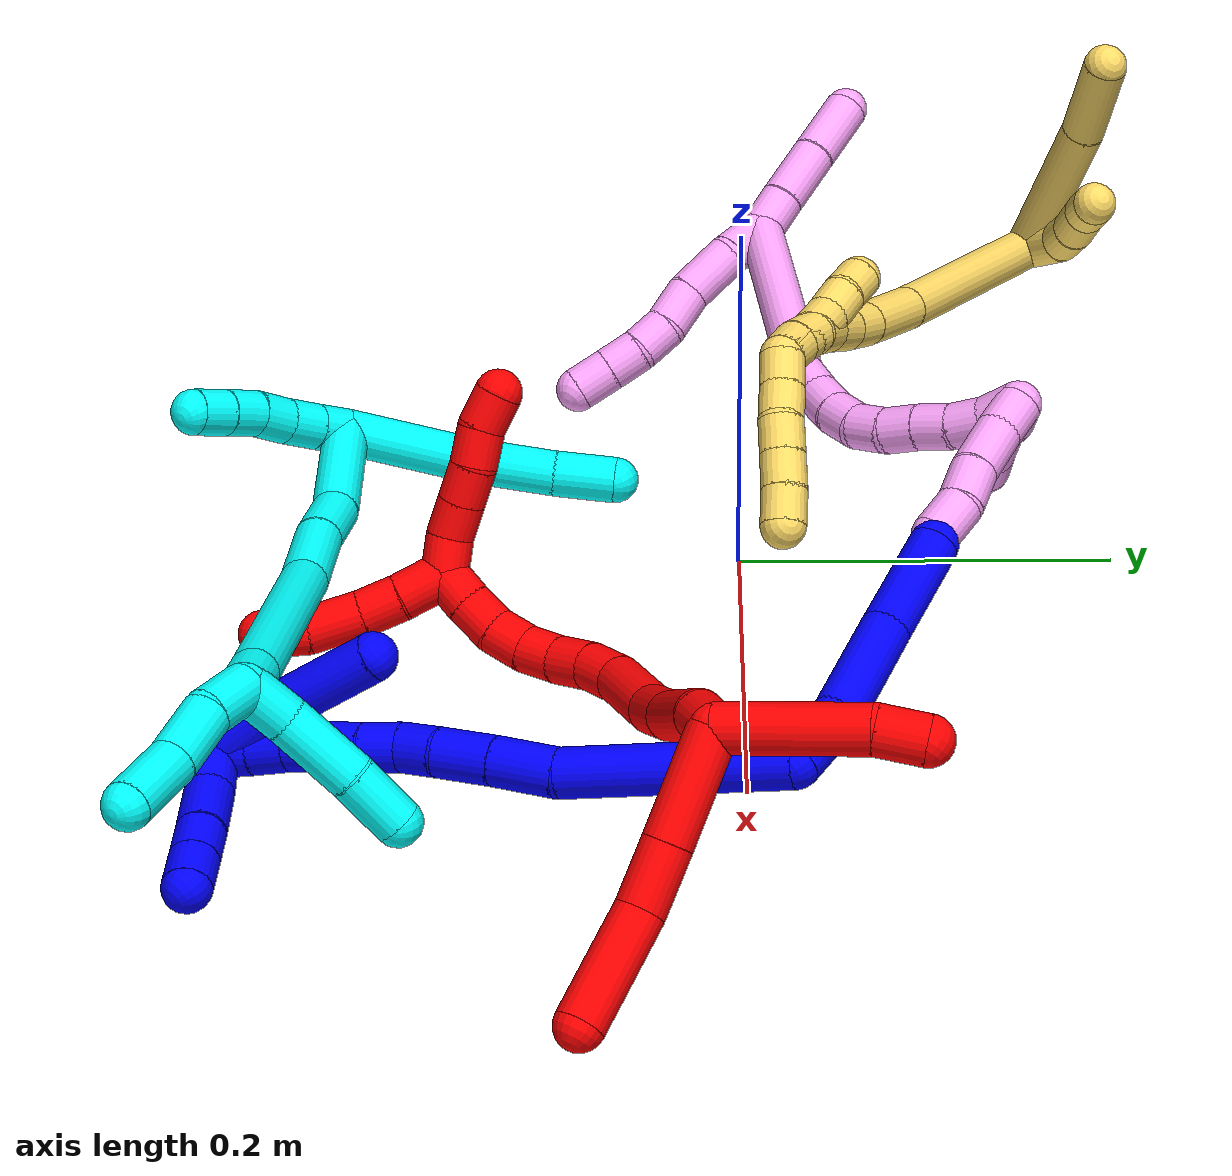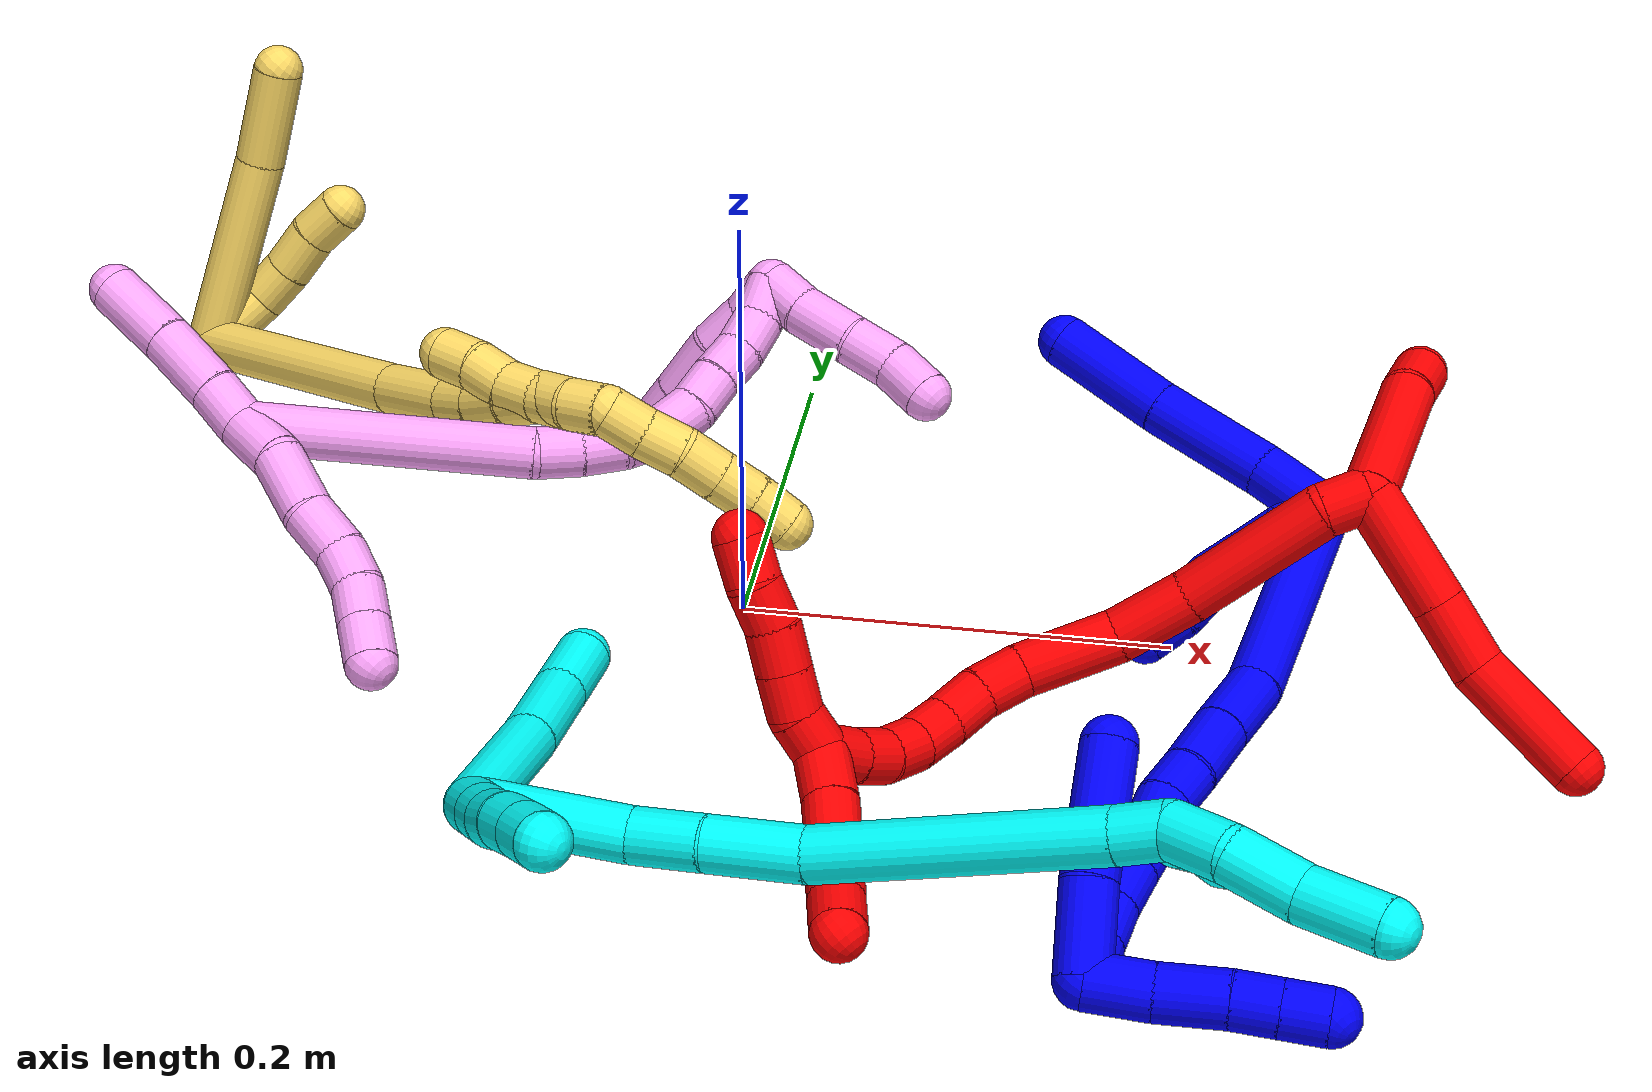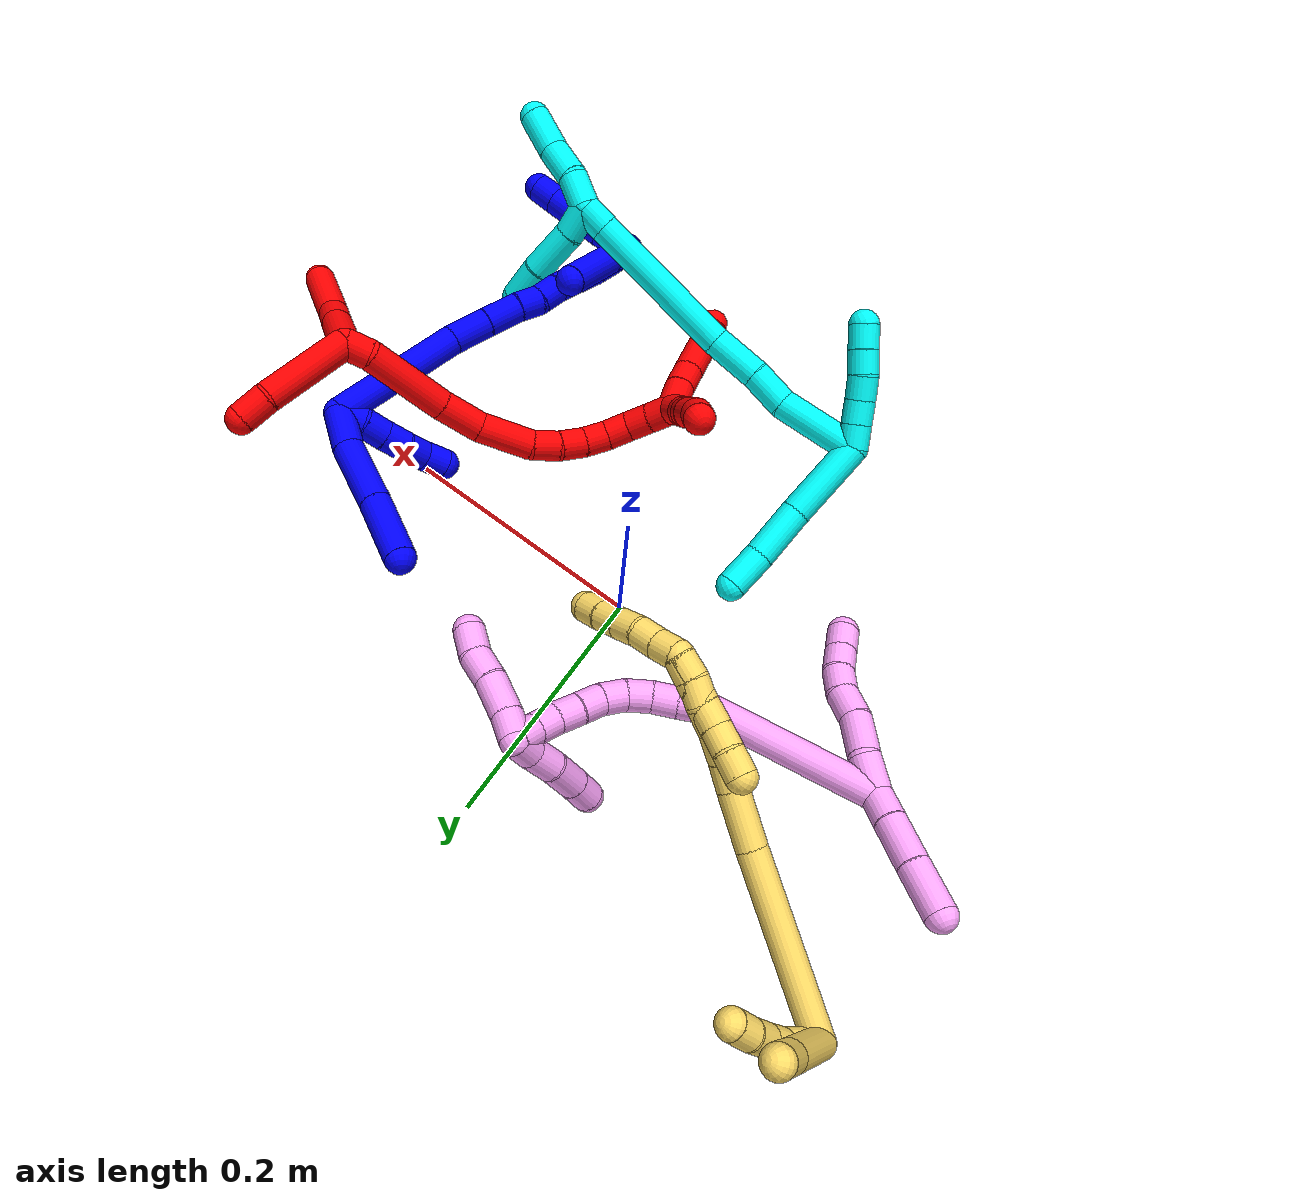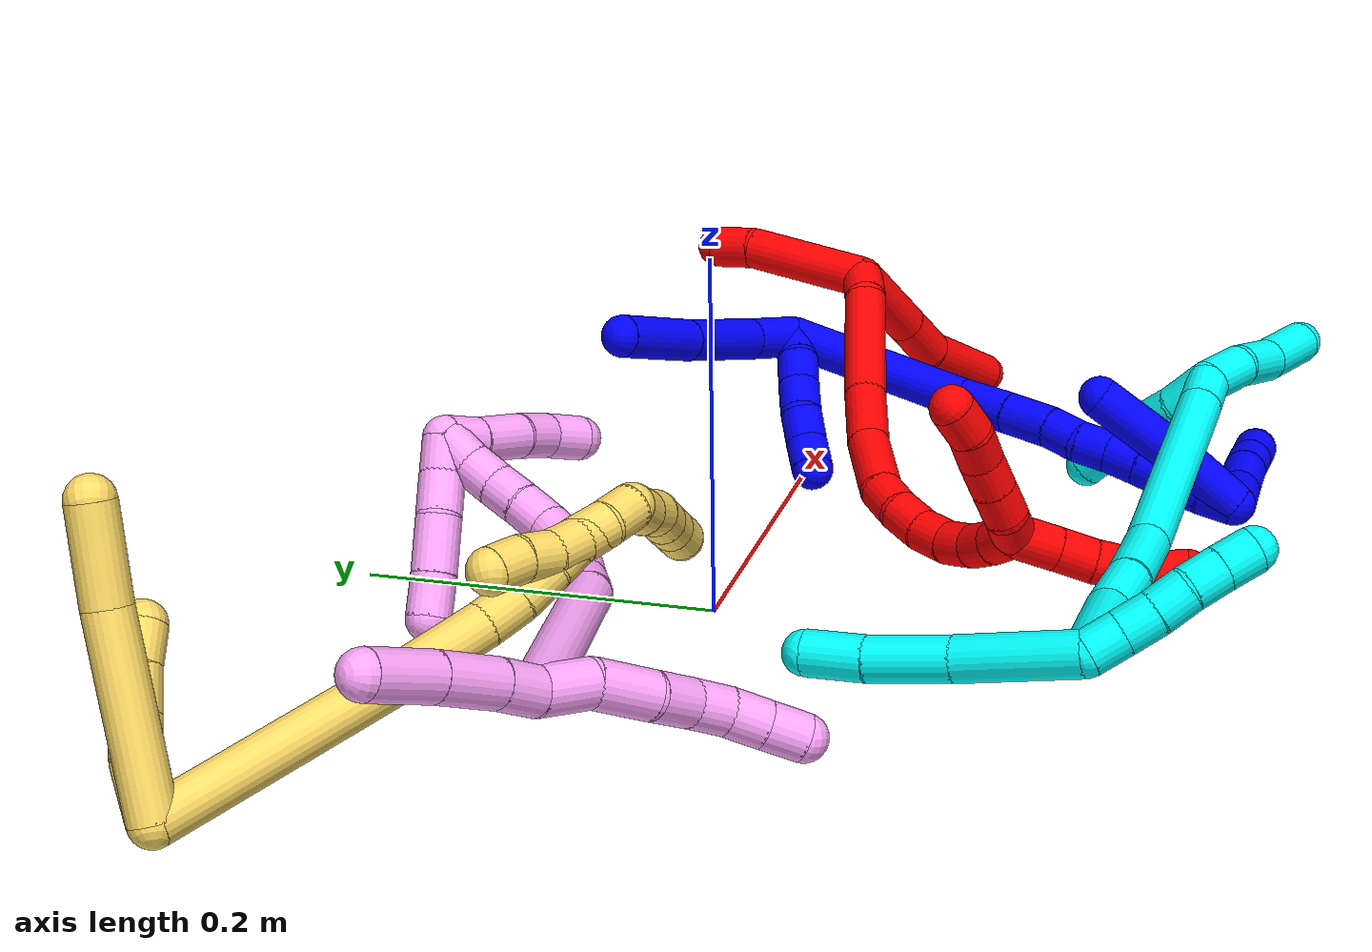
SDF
<sdf version="1.7">
 <world name="default">
  <plugin name="TubeGeneratorPlugin" filename="libtube_generator_plugin.so"/>
  <model name="photoneo_s_sensor">
   <static>1</static>
   <pose>0 0 2 1.57079 1.57079 3.14159</pose>
   <link name="link">
    <inertial><mass>0.1</mass></inertial>
    <sensor name="sensor" type="depth">
     <update_rate>30</update_rate>
     <camera>
      <horizontal_fov>1.22</horizontal_fov>
      <image><width>1920</width><height>1200</height><format>B8G8R8</format></image>
      <clip><near>0.1</near><far>4</far></clip>
      <depth_camera><output>points</output></depth_camera>
     </camera>
     <plugin name="camera_plugin" filename="libgazebo_ros_depth_camera.so">
      <baseline>0.2</baseline>
      <alwaysOn>1</alwaysOn>
      <updateRate>0.0</updateRate>
      <cameraName>camera_ir</cameraName>
      <imageTopicName>/camera/color/image_raw</imageTopicName>
      <cameraInfoTopicName>/camera/color/camera_info</cameraInfoTopicName>
      <depthImageTopicName>/camera/depth/image_raw</depthImageTopicName>
      <depthImageCameraInfoTopicName>/camera/depth/camera_info</depthImageCameraInfoTopicName>
      <pointCloudTopicName>/camera/depth/points</pointCloudTopicName>
      <frameName>fr_optical</frameName>
      <pointCloudCutoff>0.1</pointCloudCutoff>
      <pointCloudCutoffMax>2.0</pointCloudCutoffMax>
      <distortionK1>0</distortionK1>
      <distortionK2>0</distortionK2>
      <distortionK3>0</distortionK3>
      <distortionT1>0</distortionT1>
      <distortionT2>0</distortionT2>
      <CxPrime>0</CxPrime>
      <Cx>0</Cx>
      <Cy>0</Cy>
      <focalLength>0</focalLength>
      <hackBaseline>0</hackBaseline>
     </plugin>
    </sensor>
   </link>
  </model>
  <gravity>0 0 -9.8</gravity>
  <magnetic_field>6e-06 2.3e-05 -4.2e-05</magnetic_field>
  <atmosphere type="adiabatic"/>
  <physics name="default_physics" default="0" type="ode">
   <max_step_size>0.003</max_step_size>
   <real_time_factor>1</real_time_factor>
   <real_time_update_rate>1000</real_time_update_rate>
   <max_contacts>10000</max_contacts>
   <ode>
    <solver>
     <type>quick</type>
     <iters>100</iters>
     <sor>1.3</sor>
     <use_dynamic_moi_rescaling>0</use_dynamic_moi_rescaling>
    </solver>
    <constraints>
     <contact_max_correcting_vel>0</contact_max_correcting_vel>
     <contact_surface_layer>0.001</contact_surface_layer>
     <cfm>0</cfm>
     <erp>0.2</erp>
    </constraints>
   </ode>
  </physics>
  <scene><ambient>0.4 0.4 0.4 1</ambient><background>0.7 0.7 0.7 1</background><shadows>0</shadows></scene>
  <audio><device>default</device></audio>
  <spherical_coordinates>
   <surface_model>EARTH_WGS84</surface_model>
   <latitude_deg>0</latitude_deg>
   <longitude_deg>0</longitude_deg>
   <elevation>0</elevation>
   <heading_deg>0</heading_deg>
  </spherical_coordinates>
  <model name="bin">
   <static>1</static>
   <link name="bottom">
    <collision name="collision-bottom">
     <pose>0 0 -0.01 0 -0 0</pose>
     <geometry><box><size>0.8 0.6 0.02</size></box></geometry>
     <surface>
      <friction><ode><mu>100</mu><mu2>100</mu2></ode></friction>
      <contact><collide_bitmask>65535</collide_bitmask></contact>
     </surface>
    </collision>
   </link>
   <link name="west_wall">
    <collision name="collision-west_wall">
     <pose>-0.41 0 0.1 0 -0 0</pose>
     <geometry><box><size>0.02 0.6 0.2</size></box></geometry>
     <surface>
      <friction><ode><mu>100</mu><mu2>100</mu2></ode></friction>
      <contact><collide_bitmask>65535</collide_bitmask></contact>
     </surface>
    </collision>
   </link>
   <link name="east_wall">
    <collision name="collision-east_wall">
     <pose>0.41 0 0.1 0 -0 0</pose>
     <geometry><box><size>0.02 0.6 0.2</size></box></geometry>
     <surface>
      <friction><ode><mu>100</mu><mu2>100</mu2></ode></friction>
      <contact><collide_bitmask>65535</collide_bitmask></contact>
     </surface>
    </collision>
   </link>
   <link name="south_wall">
    <collision name="collision-south_wall">
     <pose>0 -0.31 0.1 0 -0 0</pose>
     <geometry><box><size>0.8 0.02 0.2</size></box></geometry>
     <surface>
      <friction><ode><mu>100</mu><mu2>100</mu2></ode></friction>
      <contact><collide_bitmask>65535</collide_bitmask></contact>
     </surface>
    </collision>
   </link>
   <link name="north_wall">
    <collision name="collision-north_wall">
     <pose>0 0.31 0.1 0 -0 0</pose>
     <geometry><box><size>0.8 0.02 0.2</size></box></geometry>
     <surface>
      <friction><ode><mu>100</mu><mu2>100</mu2></ode></friction>
      <contact><collide_bitmask>65535</collide_bitmask></contact>
     </surface>
    </collision>
   </link>
  </model>
  <model name="1">
   <static>0</static>
   <link name="1">
    <collision name="collision-cylinder-e_1_2_8">
     <pose>0.000787 -0.001847 -0.017692 3.03757 0.044239 0.803703</pose>
     <geometry><cylinder><radius>0.0125</radius><length>0.035611</length></cylinder></geometry>
     <surface>
      <friction><ode><mu>1.16</mu><mu2>1.16</mu2><slip1>0</slip1><slip2>0</slip2></ode></friction>
      <contact><ode><kp>1e+06</kp><kd>1</kd><max_vel>0</max_vel><min_depth>0.001</min_depth></ode></contact>
     </surface>
    </collision>
    <visual name="visual-cylinder-e_1_2_8">
     <pose>0.000787 -0.001847 -0.017692 3.03757 0.044239 0.803703</pose>
     <geometry><cylinder><radius>0.0125</radius><length>0.035611</length></cylinder></geometry>
     <material><ambient>0 0 1 1</ambient></material>
    </visual>
    <collision name="collision-cylinder-e_2_8_9">
     <pose>0.001974 -0.011792 -0.063306 2.85933 0.013743 0.096654</pose>
     <geometry><cylinder><radius>0.0125</radius><length>0.05815</length></cylinder></geometry>
     <surface>
      <friction><ode><mu>1.16</mu><mu2>1.16</mu2><slip1>0</slip1><slip2>0</slip2></ode></friction>
      <contact><ode><kp>1e+06</kp><kd>1</kd><max_vel>0</max_vel><min_depth>0.001</min_depth></ode></contact>
     </surface>
    </collision>
    <visual name="visual-cylinder-e_2_8_9">
     <pose>0.001974 -0.011792 -0.063306 2.85933 0.013743 0.096654</pose>
     <geometry><cylinder><radius>0.0125</radius><length>0.05815</length></cylinder></geometry>
     <material><ambient>0 0 1 1</ambient></material>
    </visual>
    <collision name="collision-cylinder-e_3_9_6">
     <pose>0.001217 -0.027112 -0.118379 2.88158 -0.04115 -0.312225</pose>
     <geometry><cylinder><radius>0.0125</radius><length>0.056238</length></cylinder></geometry>
     <surface>
      <friction><ode><mu>1.16</mu><mu2>1.16</mu2><slip1>0</slip1><slip2>0</slip2></ode></friction>
      <contact><ode><kp>1e+06</kp><kd>1</kd><max_vel>0</max_vel><min_depth>0.001</min_depth></ode></contact>
     </surface>
    </collision>
    <visual name="visual-cylinder-e_3_9_6">
     <pose>0.001217 -0.027112 -0.118379 2.88158 -0.04115 -0.312225</pose>
     <geometry><cylinder><radius>0.0125</radius><length>0.056238</length></cylinder></geometry>
     <material><ambient>0 0 1 1</ambient></material>
    </visual>
    <collision name="collision-cylinder-e_1_2_10">
     <pose>0.006693 -0.006762 -0.003079 1.99802 0.733246 1.076</pose>
     <geometry><cylinder><radius>0.0125</radius><length>0.02</length></cylinder></geometry>
     <surface>
      <friction><ode><mu>1.16</mu><mu2>1.16</mu2><slip1>0</slip1><slip2>0</slip2></ode></friction>
      <contact><ode><kp>1e+06</kp><kd>1</kd><max_vel>0</max_vel><min_depth>0.001</min_depth></ode></contact>
     </surface>
    </collision>
    <visual name="visual-cylinder-e_1_2_10">
     <pose>0.006693 -0.006762 -0.003079 1.99802 0.733246 1.076</pose>
     <geometry><cylinder><radius>0.0125</radius><length>0.02</length></cylinder></geometry>
     <material><ambient>0 0 1 1</ambient></material>
    </visual>
    <collision name="collision-cylinder-e_2_10_11">
     <pose>0.021573 -0.018449 -0.009109 2.11083 0.959181 1.48552</pose>
     <geometry><cylinder><radius>0.0125</radius><length>0.02</length></cylinder></geometry>
     <surface>
      <friction><ode><mu>1.16</mu><mu2>1.16</mu2><slip1>0</slip1><slip2>0</slip2></ode></friction>
      <contact><ode><kp>1e+06</kp><kd>1</kd><max_vel>0</max_vel><min_depth>0.001</min_depth></ode></contact>
     </surface>
    </collision>
    <visual name="visual-cylinder-e_2_10_11">
     <pose>0.021573 -0.018449 -0.009109 2.11083 0.959181 1.48552</pose>
     <geometry><cylinder><radius>0.0125</radius><length>0.02</length></cylinder></geometry>
     <material><ambient>0 0 1 1</ambient></material>
    </visual>
    <collision name="collision-cylinder-e_3_11_12">
     <pose>0.037724 -0.028708 -0.014912 2.06147 0.921307 1.3829</pose>
     <geometry><cylinder><radius>0.0125</radius><length>0.02</length></cylinder></geometry>
     <surface>
      <friction><ode><mu>1.16</mu><mu2>1.16</mu2><slip1>0</slip1><slip2>0</slip2></ode></friction>
      <contact><ode><kp>1e+06</kp><kd>1</kd><max_vel>0</max_vel><min_depth>0.001</min_depth></ode></contact>
     </surface>
    </collision>
    <visual name="visual-cylinder-e_3_11_12">
     <pose>0.037724 -0.028708 -0.014912 2.06147 0.921307 1.3829</pose>
     <geometry><cylinder><radius>0.0125</radius><length>0.02</length></cylinder></geometry>
     <material><ambient>0 0 1 1</ambient></material>
    </visual>
    <collision name="collision-cylinder-e_4_12_13">
     <pose>0.054742 -0.038223 -0.018495 1.74454 1.13244 1.29584</pose>
     <geometry><cylinder><radius>0.0125</radius><length>0.02</length></cylinder></geometry>
     <surface>
      <friction><ode><mu>1.16</mu><mu2>1.16</mu2><slip1>0</slip1><slip2>0</slip2></ode></friction>
      <contact><ode><kp>1e+06</kp><kd>1</kd><max_vel>0</max_vel><min_depth>0.001</min_depth></ode></contact>
     </surface>
    </collision>
    <visual name="visual-cylinder-e_4_12_13">
     <pose>0.054742 -0.038223 -0.018495 1.74454 1.13244 1.29584</pose>
     <geometry><cylinder><radius>0.0125</radius><length>0.02</length></cylinder></geometry>
     <material><ambient>0 0 1 1</ambient></material>
    </visual>
    <collision name="collision-cylinder-e_5_13_5">
     <pose>0.071458 -0.048489 -0.0213 1.89887 0.872692 1.15461</pose>
     <geometry><cylinder><radius>0.0125</radius><length>0.02</length></cylinder></geometry>
     <surface>
      <friction><ode><mu>1.16</mu><mu2>1.16</mu2><slip1>0</slip1><slip2>0</slip2></ode></friction>
      <contact><ode><kp>1e+06</kp><kd>1</kd><max_vel>0</max_vel><min_depth>0.001</min_depth></ode></contact>
     </surface>
    </collision>
    <visual name="visual-cylinder-e_5_13_5">
     <pose>0.071458 -0.048489 -0.0213 1.89887 0.872692 1.15461</pose>
     <geometry><cylinder><radius>0.0125</radius><length>0.02</length></cylinder></geometry>
     <material><ambient>0 0 1 1</ambient></material>
    </visual>
    <collision name="collision-cylinder-e_1_2_14">
     <pose>0.018188 -0.045584 0.031115 0.971857 0.318342 0.169168</pose>
     <geometry><cylinder><radius>0.0125</radius><length>0.116222</length></cylinder></geometry>
     <surface>
      <friction><ode><mu>1.16</mu><mu2>1.16</mu2><slip1>0</slip1><slip2>0</slip2></ode></friction>
      <contact><ode><kp>1e+06</kp><kd>1</kd><max_vel>0</max_vel><min_depth>0.001</min_depth></ode></contact>
     </surface>
    </collision>
    <visual name="visual-cylinder-e_1_2_14">
     <pose>0.018188 -0.045584 0.031115 0.971857 0.318342 0.169168</pose>
     <geometry><cylinder><radius>0.0125</radius><length>0.116222</length></cylinder></geometry>
     <material><ambient>0 0 1 1</ambient></material>
    </visual>
    <collision name="collision-cylinder-e_2_14_15">
     <pose>0.040316 -0.106117 0.068219 1.18972 0.239934 0.162767</pose>
     <geometry><cylinder><radius>0.0125</radius><length>0.033158</length></cylinder></geometry>
     <surface>
      <friction><ode><mu>1.16</mu><mu2>1.16</mu2><slip1>0</slip1><slip2>0</slip2></ode></friction>
      <contact><ode><kp>1e+06</kp><kd>1</kd><max_vel>0</max_vel><min_depth>0.001</min_depth></ode></contact>
     </surface>
    </collision>
    <visual name="visual-cylinder-e_2_14_15">
     <pose>0.040316 -0.106117 0.068219 1.18972 0.239934 0.162767</pose>
     <geometry><cylinder><radius>0.0125</radius><length>0.033158</length></cylinder></geometry>
     <material><ambient>0 0 1 1</ambient></material>
    </visual>
    <collision name="collision-cylinder-e_3_15_16">
     <pose>0.04822 -0.134245 0.079762 1.17199 0.270374 0.18008</pose>
     <geometry><cylinder><radius>0.0125</radius><length>0.029681</length></cylinder></geometry>
     <surface>
      <friction><ode><mu>1.16</mu><mu2>1.16</mu2><slip1>0</slip1><slip2>0</slip2></ode></friction>
      <contact><ode><kp>1e+06</kp><kd>1</kd><max_vel>0</max_vel><min_depth>0.001</min_depth></ode></contact>
     </surface>
    </collision>
    <visual name="visual-cylinder-e_3_15_16">
     <pose>0.04822 -0.134245 0.079762 1.17199 0.270374 0.18008</pose>
     <geometry><cylinder><radius>0.0125</radius><length>0.029681</length></cylinder></geometry>
     <material><ambient>0 0 1 1</ambient></material>
    </visual>
    <collision name="collision-cylinder-e_4_16_17">
     <pose>0.055984 -0.156332 0.088416 1.23591 0.383029 0.273919</pose>
     <geometry><cylinder><radius>0.0125</radius><length>0.020338</length></cylinder></geometry>
     <surface>
      <friction><ode><mu>1.16</mu><mu2>1.16</mu2><slip1>0</slip1><slip2>0</slip2></ode></friction>
      <contact><ode><kp>1e+06</kp><kd>1</kd><max_vel>0</max_vel><min_depth>0.001</min_depth></ode></contact>
     </surface>
    </collision>
    <visual name="visual-cylinder-e_4_16_17">
     <pose>0.055984 -0.156332 0.088416 1.23591 0.383029 0.273919</pose>
     <geometry><cylinder><radius>0.0125</radius><length>0.020338</length></cylinder></geometry>
     <material><ambient>0 0 1 1</ambient></material>
    </visual>
    <collision name="collision-cylinder-e_5_17_18">
     <pose>0.062637 -0.17329 0.096867 0.984127 0.286913 0.154553</pose>
     <geometry><cylinder><radius>0.0125</radius><length>0.020156</length></cylinder></geometry>
     <surface>
      <friction><ode><mu>1.16</mu><mu2>1.16</mu2><slip1>0</slip1><slip2>0</slip2></ode></friction>
      <contact><ode><kp>1e+06</kp><kd>1</kd><max_vel>0</max_vel><min_depth>0.001</min_depth></ode></contact>
     </surface>
    </collision>
    <visual name="visual-cylinder-e_5_17_18">
     <pose>0.062637 -0.17329 0.096867 0.984127 0.286913 0.154553</pose>
     <geometry><cylinder><radius>0.0125</radius><length>0.020156</length></cylinder></geometry>
     <material><ambient>0 0 1 1</ambient></material>
    </visual>
    <collision name="collision-cylinder-e_6_18_19">
     <pose>0.068979 -0.189744 0.106458 1.10348 0.355122 0.220013</pose>
     <geometry><cylinder><radius>0.0125</radius><length>0.020079</length></cylinder></geometry>
     <surface>
      <friction><ode><mu>1.16</mu><mu2>1.16</mu2><slip1>0</slip1><slip2>0</slip2></ode></friction>
      <contact><ode><kp>1e+06</kp><kd>1</kd><max_vel>0</max_vel><min_depth>0.001</min_depth></ode></contact>
     </surface>
    </collision>
    <visual name="visual-cylinder-e_6_18_19">
     <pose>0.068979 -0.189744 0.106458 1.10348 0.355122 0.220013</pose>
     <geometry><cylinder><radius>0.0125</radius><length>0.020079</length></cylinder></geometry>
     <material><ambient>0 0 1 1</ambient></material>
    </visual>
    <collision name="collision-cylinder-e_7_19_20">
     <pose>0.07634 -0.206375 0.115133 1.07647 0.392567 0.236326</pose>
     <geometry><cylinder><radius>0.0125</radius><length>0.020231</length></cylinder></geometry>
     <surface>
      <friction><ode><mu>1.16</mu><mu2>1.16</mu2><slip1>0</slip1><slip2>0</slip2></ode></friction>
      <contact><ode><kp>1e+06</kp><kd>1</kd><max_vel>0</max_vel><min_depth>0.001</min_depth></ode></contact>
     </surface>
    </collision>
    <visual name="visual-cylinder-e_7_19_20">
     <pose>0.07634 -0.206375 0.115133 1.07647 0.392567 0.236326</pose>
     <geometry><cylinder><radius>0.0125</radius><length>0.020231</length></cylinder></geometry>
     <material><ambient>0 0 1 1</ambient></material>
    </visual>
    <collision name="collision-cylinder-e_8_20_21">
     <pose>0.083989 -0.222203 0.124873 0.961316 0.387122 0.203716</pose>
     <geometry><cylinder><radius>0.0125</radius><length>0.020022</length></cylinder></geometry>
     <surface>
      <friction><ode><mu>1.16</mu><mu2>1.16</mu2><slip1>0</slip1><slip2>0</slip2></ode></friction>
      <contact><ode><kp>1e+06</kp><kd>1</kd><max_vel>0</max_vel><min_depth>0.001</min_depth></ode></contact>
     </surface>
    </collision>
    <visual name="visual-cylinder-e_8_20_21">
     <pose>0.083989 -0.222203 0.124873 0.961316 0.387122 0.203716</pose>
     <geometry><cylinder><radius>0.0125</radius><length>0.020022</length></cylinder></geometry>
     <material><ambient>0 0 1 1</ambient></material>
    </visual>
    <collision name="collision-cylinder-e_9_21_1">
     <pose>0.090682 -0.237477 0.135992 0.922521 0.293915 0.146877</pose>
     <geometry><cylinder><radius>0.0125</radius><length>0.020114</length></cylinder></geometry>
     <surface>
      <friction><ode><mu>1.16</mu><mu2>1.16</mu2><slip1>0</slip1><slip2>0</slip2></ode></friction>
      <contact><ode><kp>1e+06</kp><kd>1</kd><max_vel>0</max_vel><min_depth>0.001</min_depth></ode></contact>
     </surface>
    </collision>
    <visual name="visual-cylinder-e_9_21_1">
     <pose>0.090682 -0.237477 0.135992 0.922521 0.293915 0.146877</pose>
     <geometry><cylinder><radius>0.0125</radius><length>0.020114</length></cylinder></geometry>
     <material><ambient>0 0 1 1</ambient></material>
    </visual>
    <collision name="collision-cylinder-e_1_1_22">
     <pose>0.090296 -0.23589 0.152314 -0.72222 -0.231333 0.087703</pose>
     <geometry><cylinder><radius>0.0125</radius><length>0.028782</length></cylinder></geometry>
     <surface>
      <friction><ode><mu>1.16</mu><mu2>1.16</mu2><slip1>0</slip1><slip2>0</slip2></ode></friction>
      <contact><ode><kp>1e+06</kp><kd>1</kd><max_vel>0</max_vel><min_depth>0.001</min_depth></ode></contact>
     </surface>
    </collision>
    <visual name="visual-cylinder-e_1_1_22">
     <pose>0.090296 -0.23589 0.152314 -0.72222 -0.231333 0.087703</pose>
     <geometry><cylinder><radius>0.0125</radius><length>0.028782</length></cylinder></geometry>
     <material><ambient>0 0 1 1</ambient></material>
    </visual>
    <collision name="collision-cylinder-e_2_22_23">
     <pose>0.081675 -0.217541 0.174156 -0.676059 -0.351162 0.124564</pose>
     <geometry><cylinder><radius>0.0125</radius><length>0.03094</length></cylinder></geometry>
     <surface>
      <friction><ode><mu>1.16</mu><mu2>1.16</mu2><slip1>0</slip1><slip2>0</slip2></ode></friction>
      <contact><ode><kp>1e+06</kp><kd>1</kd><max_vel>0</max_vel><min_depth>0.001</min_depth></ode></contact>
     </surface>
    </collision>
    <visual name="visual-cylinder-e_2_22_23">
     <pose>0.081675 -0.217541 0.174156 -0.676059 -0.351162 0.124564</pose>
     <geometry><cylinder><radius>0.0125</radius><length>0.03094</length></cylinder></geometry>
     <material><ambient>0 0 1 1</ambient></material>
    </visual>
    <collision name="collision-cylinder-e_3_23_24">
     <pose>0.073596 -0.202672 0.193246 -0.640168 -0.277654 0.092567</pose>
     <geometry><cylinder><radius>0.0125</radius><length>0.020121</length></cylinder></geometry>
     <surface>
      <friction><ode><mu>1.16</mu><mu2>1.16</mu2><slip1>0</slip1><slip2>0</slip2></ode></friction>
      <contact><ode><kp>1e+06</kp><kd>1</kd><max_vel>0</max_vel><min_depth>0.001</min_depth></ode></contact>
     </surface>
    </collision>
    <visual name="visual-cylinder-e_3_23_24">
     <pose>0.073596 -0.202672 0.193246 -0.640168 -0.277654 0.092567</pose>
     <geometry><cylinder><radius>0.0125</radius><length>0.020121</length></cylinder></geometry>
     <material><ambient>0 0 1 1</ambient></material>
    </visual>
    <collision name="collision-cylinder-e_4_24_4">
     <pose>0.068047 -0.191143 0.208798 -0.635709 -0.280607 0.092866</pose>
     <geometry><cylinder><radius>0.0125</radius><length>0.020157</length></cylinder></geometry>
     <surface>
      <friction><ode><mu>1.16</mu><mu2>1.16</mu2><slip1>0</slip1><slip2>0</slip2></ode></friction>
      <contact><ode><kp>1e+06</kp><kd>1</kd><max_vel>0</max_vel><min_depth>0.001</min_depth></ode></contact>
     </surface>
    </collision>
    <visual name="visual-cylinder-e_4_24_4">
     <pose>0.068047 -0.191143 0.208798 -0.635709 -0.280607 0.092866</pose>
     <geometry><cylinder><radius>0.0125</radius><length>0.020157</length></cylinder></geometry>
     <material><ambient>0 0 1 1</ambient></material>
    </visual>
    <collision name="collision-cylinder-e_1_1_25">
     <pose>0.080707 -0.237307 0.128455 -2.61042 -0.694219 1.85213</pose>
     <geometry><cylinder><radius>0.0125</radius><length>0.040289</length></cylinder></geometry>
     <surface>
      <friction><ode><mu>1.16</mu><mu2>1.16</mu2><slip1>0</slip1><slip2>0</slip2></ode></friction>
      <contact><ode><kp>1e+06</kp><kd>1</kd><max_vel>0</max_vel><min_depth>0.001</min_depth></ode></contact>
     </surface>
    </collision>
    <visual name="visual-cylinder-e_1_1_25">
     <pose>0.080707 -0.237307 0.128455 -2.61042 -0.694219 1.85213</pose>
     <geometry><cylinder><radius>0.0125</radius><length>0.040289</length></cylinder></geometry>
     <material><ambient>0 0 1 1</ambient></material>
    </visual>
    <collision name="collision-cylinder-e_2_25_3">
     <pose>0.050189 -0.214577 0.096162 -2.47554 -0.631689 1.51395</pose>
     <geometry><cylinder><radius>0.0125</radius><length>0.059711</length></cylinder></geometry>
     <surface>
      <friction><ode><mu>1.16</mu><mu2>1.16</mu2><slip1>0</slip1><slip2>0</slip2></ode></friction>
      <contact><ode><kp>1e+06</kp><kd>1</kd><max_vel>0</max_vel><min_depth>0.001</min_depth></ode></contact>
     </surface>
    </collision>
    <visual name="visual-cylinder-e_2_25_3">
     <pose>0.050189 -0.214577 0.096162 -2.47554 -0.631689 1.51395</pose>
     <geometry><cylinder><radius>0.0125</radius><length>0.059711</length></cylinder></geometry>
     <material><ambient>0 0 1 1</ambient></material>
    </visual>
    <collision name="collision-sphere-3">
     <pose>0.032559 -0.19969 0.077217 0 -0 0</pose>
     <geometry><sphere><radius>0.0125</radius></sphere></geometry>
     <surface>
      <friction><ode><mu>1.16</mu><mu2>1.16</mu2><slip1>0</slip1><slip2>0</slip2></ode></friction>
      <contact><ode><kp>1e+06</kp><kd>1</kd><max_vel>0</max_vel><min_depth>0.001</min_depth></ode></contact>
     </surface>
    </collision>
    <visual name="visual-sphere-3">
     <pose>0.032559 -0.19969 0.077217 0 -0 0</pose>
     <geometry><sphere><radius>0.0125</radius></sphere></geometry>
     <material><ambient>0 0 1 1</ambient></material>
    </visual>
    <collision name="collision-sphere-25">
     <pose>0.067819 -0.229465 0.115106 0 -0 0</pose>
     <geometry><sphere><radius>0.0125</radius></sphere></geometry>
     <surface>
      <friction><ode><mu>1.16</mu><mu2>1.16</mu2><slip1>0</slip1><slip2>0</slip2></ode></friction>
      <contact><ode><kp>1e+06</kp><kd>1</kd><max_vel>0</max_vel><min_depth>0.001</min_depth></ode></contact>
     </surface>
    </collision>
    <visual name="visual-sphere-25">
     <pose>0.067819 -0.229465 0.115106 0 -0 0</pose>
     <geometry><sphere><radius>0.0125</radius></sphere></geometry>
     <material><ambient>0 0 1 1</ambient></material>
    </visual>
    <collision name="collision-sphere-4">
     <pose>0.065256 -0.185393 0.216591 0 -0 0</pose>
     <geometry><sphere><radius>0.0125</radius></sphere></geometry>
     <surface>
      <friction><ode><mu>1.16</mu><mu2>1.16</mu2><slip1>0</slip1><slip2>0</slip2></ode></friction>
      <contact><ode><kp>1e+06</kp><kd>1</kd><max_vel>0</max_vel><min_depth>0.001</min_depth></ode></contact>
     </surface>
    </collision>
    <visual name="visual-sphere-4">
     <pose>0.065256 -0.185393 0.216591 0 -0 0</pose>
     <geometry><sphere><radius>0.0125</radius></sphere></geometry>
     <material><ambient>0 0 1 1</ambient></material>
    </visual>
    <collision name="collision-sphere-24">
     <pose>0.070838 -0.196893 0.201005 0 -0 0</pose>
     <geometry><sphere><radius>0.0125</radius></sphere></geometry>
     <surface>
      <friction><ode><mu>1.16</mu><mu2>1.16</mu2><slip1>0</slip1><slip2>0</slip2></ode></friction>
      <contact><ode><kp>1e+06</kp><kd>1</kd><max_vel>0</max_vel><min_depth>0.001</min_depth></ode></contact>
     </surface>
    </collision>
    <visual name="visual-sphere-24">
     <pose>0.070838 -0.196893 0.201005 0 -0 0</pose>
     <geometry><sphere><radius>0.0125</radius></sphere></geometry>
     <material><ambient>0 0 1 1</ambient></material>
    </visual>
    <collision name="collision-sphere-23">
     <pose>0.076353 -0.208452 0.185487 0 -0 0</pose>
     <geometry><sphere><radius>0.0125</radius></sphere></geometry>
     <surface>
      <friction><ode><mu>1.16</mu><mu2>1.16</mu2><slip1>0</slip1><slip2>0</slip2></ode></friction>
      <contact><ode><kp>1e+06</kp><kd>1</kd><max_vel>0</max_vel><min_depth>0.001</min_depth></ode></contact>
     </surface>
    </collision>
    <visual name="visual-sphere-23">
     <pose>0.076353 -0.208452 0.185487 0 -0 0</pose>
     <geometry><sphere><radius>0.0125</radius></sphere></geometry>
     <material><ambient>0 0 1 1</ambient></material>
    </visual>
    <collision name="collision-sphere-22">
     <pose>0.086997 -0.22663 0.162825 0 -0 0</pose>
     <geometry><sphere><radius>0.0125</radius></sphere></geometry>
     <surface>
      <friction><ode><mu>1.16</mu><mu2>1.16</mu2><slip1>0</slip1><slip2>0</slip2></ode></friction>
      <contact><ode><kp>1e+06</kp><kd>1</kd><max_vel>0</max_vel><min_depth>0.001</min_depth></ode></contact>
     </surface>
    </collision>
    <visual name="visual-sphere-22">
     <pose>0.086997 -0.22663 0.162825 0 -0 0</pose>
     <geometry><sphere><radius>0.0125</radius></sphere></geometry>
     <material><ambient>0 0 1 1</ambient></material>
    </visual>
    <collision name="collision-sphere-1">
     <pose>0.093595 -0.245149 0.141804 0 -0 0</pose>
     <geometry><sphere><radius>0.0125</radius></sphere></geometry>
     <surface>
      <friction><ode><mu>1.16</mu><mu2>1.16</mu2><slip1>0</slip1><slip2>0</slip2></ode></friction>
      <contact><ode><kp>1e+06</kp><kd>1</kd><max_vel>0</max_vel><min_depth>0.001</min_depth></ode></contact>
     </surface>
    </collision>
    <visual name="visual-sphere-1">
     <pose>0.093595 -0.245149 0.141804 0 -0 0</pose>
     <geometry><sphere><radius>0.0125</radius></sphere></geometry>
     <material><ambient>0 0 1 1</ambient></material>
    </visual>
    <collision name="collision-sphere-21">
     <pose>0.087769 -0.229804 0.13018 0 -0 0</pose>
     <geometry><sphere><radius>0.0125</radius></sphere></geometry>
     <surface>
      <friction><ode><mu>1.16</mu><mu2>1.16</mu2><slip1>0</slip1><slip2>0</slip2></ode></friction>
      <contact><ode><kp>1e+06</kp><kd>1</kd><max_vel>0</max_vel><min_depth>0.001</min_depth></ode></contact>
     </surface>
    </collision>
    <visual name="visual-sphere-21">
     <pose>0.087769 -0.229804 0.13018 0 -0 0</pose>
     <geometry><sphere><radius>0.0125</radius></sphere></geometry>
     <material><ambient>0 0 1 1</ambient></material>
    </visual>
    <collision name="collision-sphere-11">
     <pose>0.02976 -0.023374 -0.012062 0 -0 0</pose>
     <geometry><sphere><radius>0.0125</radius></sphere></geometry>
     <surface>
      <friction><ode><mu>1.16</mu><mu2>1.16</mu2><slip1>0</slip1><slip2>0</slip2></ode></friction>
      <contact><ode><kp>1e+06</kp><kd>1</kd><max_vel>0</max_vel><min_depth>0.001</min_depth></ode></contact>
     </surface>
    </collision>
    <visual name="visual-sphere-11">
     <pose>0.02976 -0.023374 -0.012062 0 -0 0</pose>
     <geometry><sphere><radius>0.0125</radius></sphere></geometry>
     <material><ambient>0 0 1 1</ambient></material>
    </visual>
    <collision name="collision-sphere-10">
     <pose>0.013386 -0.013524 -0.006157 0 -0 0</pose>
     <geometry><sphere><radius>0.0125</radius></sphere></geometry>
     <surface>
      <friction><ode><mu>1.16</mu><mu2>1.16</mu2><slip1>0</slip1><slip2>0</slip2></ode></friction>
      <contact><ode><kp>1e+06</kp><kd>1</kd><max_vel>0</max_vel><min_depth>0.001</min_depth></ode></contact>
     </surface>
    </collision>
    <visual name="visual-sphere-10">
     <pose>0.013386 -0.013524 -0.006157 0 -0 0</pose>
     <geometry><sphere><radius>0.0125</radius></sphere></geometry>
     <material><ambient>0 0 1 1</ambient></material>
    </visual>
    <collision name="collision-sphere-6">
     <pose>6e-05 -0.034335 -0.14553 0 -0 0</pose>
     <geometry><sphere><radius>0.0125</radius></sphere></geometry>
     <surface>
      <friction><ode><mu>1.16</mu><mu2>1.16</mu2><slip1>0</slip1><slip2>0</slip2></ode></friction>
      <contact><ode><kp>1e+06</kp><kd>1</kd><max_vel>0</max_vel><min_depth>0.001</min_depth></ode></contact>
     </surface>
    </collision>
    <visual name="visual-sphere-6">
     <pose>6e-05 -0.034335 -0.14553 0 -0 0</pose>
     <geometry><sphere><radius>0.0125</radius></sphere></geometry>
     <material><ambient>0 0 1 1</ambient></material>
    </visual>
    <collision name="collision-sphere-9">
     <pose>0.002374 -0.019889 -0.091228 0 -0 0</pose>
     <geometry><sphere><radius>0.0125</radius></sphere></geometry>
     <surface>
      <friction><ode><mu>1.16</mu><mu2>1.16</mu2><slip1>0</slip1><slip2>0</slip2></ode></friction>
      <contact><ode><kp>1e+06</kp><kd>1</kd><max_vel>0</max_vel><min_depth>0.001</min_depth></ode></contact>
     </surface>
    </collision>
    <visual name="visual-sphere-9">
     <pose>0.002374 -0.019889 -0.091228 0 -0 0</pose>
     <geometry><sphere><radius>0.0125</radius></sphere></geometry>
     <material><ambient>0 0 1 1</ambient></material>
    </visual>
    <collision name="collision-sphere-2">
     <geometry><sphere><radius>0.0125</radius></sphere></geometry>
     <surface>
      <friction><ode><mu>1.16</mu><mu2>1.16</mu2><slip1>0</slip1><slip2>0</slip2></ode></friction>
      <contact><ode><kp>1e+06</kp><kd>1</kd><max_vel>0</max_vel><min_depth>0.001</min_depth></ode></contact>
     </surface>
    </collision>
    <visual name="visual-sphere-2">
     <geometry><sphere><radius>0.0125</radius></sphere></geometry>
     <material><ambient>0 0 1 1</ambient></material>
    </visual>
    <collision name="collision-sphere-19">
     <pose>0.07247 -0.198148 0.110699 0 -0 0</pose>
     <geometry><sphere><radius>0.0125</radius></sphere></geometry>
     <surface>
      <friction><ode><mu>1.16</mu><mu2>1.16</mu2><slip1>0</slip1><slip2>0</slip2></ode></friction>
      <contact><ode><kp>1e+06</kp><kd>1</kd><max_vel>0</max_vel><min_depth>0.001</min_depth></ode></contact>
     </surface>
    </collision>
    <visual name="visual-sphere-19">
     <pose>0.07247 -0.198148 0.110699 0 -0 0</pose>
     <geometry><sphere><radius>0.0125</radius></sphere></geometry>
     <material><ambient>0 0 1 1</ambient></material>
    </visual>
    <collision name="collision-sphere-8">
     <pose>0.001575 -0.003694 -0.035384 0 -0 0</pose>
     <geometry><sphere><radius>0.0125</radius></sphere></geometry>
     <surface>
      <friction><ode><mu>1.16</mu><mu2>1.16</mu2><slip1>0</slip1><slip2>0</slip2></ode></friction>
      <contact><ode><kp>1e+06</kp><kd>1</kd><max_vel>0</max_vel><min_depth>0.001</min_depth></ode></contact>
     </surface>
    </collision>
    <visual name="visual-sphere-8">
     <pose>0.001575 -0.003694 -0.035384 0 -0 0</pose>
     <geometry><sphere><radius>0.0125</radius></sphere></geometry>
     <material><ambient>0 0 1 1</ambient></material>
    </visual>
    <collision name="collision-sphere-12">
     <pose>0.045688 -0.034043 -0.017761 0 -0 0</pose>
     <geometry><sphere><radius>0.0125</radius></sphere></geometry>
     <surface>
      <friction><ode><mu>1.16</mu><mu2>1.16</mu2><slip1>0</slip1><slip2>0</slip2></ode></friction>
      <contact><ode><kp>1e+06</kp><kd>1</kd><max_vel>0</max_vel><min_depth>0.001</min_depth></ode></contact>
     </surface>
    </collision>
    <visual name="visual-sphere-12">
     <pose>0.045688 -0.034043 -0.017761 0 -0 0</pose>
     <geometry><sphere><radius>0.0125</radius></sphere></geometry>
     <material><ambient>0 0 1 1</ambient></material>
    </visual>
    <collision name="collision-sphere-13">
     <pose>0.063797 -0.042404 -0.019229 0 -0 0</pose>
     <geometry><sphere><radius>0.0125</radius></sphere></geometry>
     <surface>
      <friction><ode><mu>1.16</mu><mu2>1.16</mu2><slip1>0</slip1><slip2>0</slip2></ode></friction>
      <contact><ode><kp>1e+06</kp><kd>1</kd><max_vel>0</max_vel><min_depth>0.001</min_depth></ode></contact>
     </surface>
    </collision>
    <visual name="visual-sphere-13">
     <pose>0.063797 -0.042404 -0.019229 0 -0 0</pose>
     <geometry><sphere><radius>0.0125</radius></sphere></geometry>
     <material><ambient>0 0 1 1</ambient></material>
    </visual>
    <collision name="collision-sphere-5">
     <pose>0.079118 -0.054574 -0.023371 0 -0 0</pose>
     <geometry><sphere><radius>0.0125</radius></sphere></geometry>
     <surface>
      <friction><ode><mu>1.16</mu><mu2>1.16</mu2><slip1>0</slip1><slip2>0</slip2></ode></friction>
      <contact><ode><kp>1e+06</kp><kd>1</kd><max_vel>0</max_vel><min_depth>0.001</min_depth></ode></contact>
     </surface>
    </collision>
    <visual name="visual-sphere-5">
     <pose>0.079118 -0.054574 -0.023371 0 -0 0</pose>
     <geometry><sphere><radius>0.0125</radius></sphere></geometry>
     <material><ambient>0 0 1 1</ambient></material>
    </visual>
    <collision name="collision-sphere-14">
     <pose>0.036377 -0.091169 0.06223 0 -0 0</pose>
     <geometry><sphere><radius>0.0125</radius></sphere></geometry>
     <surface>
      <friction><ode><mu>1.16</mu><mu2>1.16</mu2><slip1>0</slip1><slip2>0</slip2></ode></friction>
      <contact><ode><kp>1e+06</kp><kd>1</kd><max_vel>0</max_vel><min_depth>0.001</min_depth></ode></contact>
     </surface>
    </collision>
    <visual name="visual-sphere-14">
     <pose>0.036377 -0.091169 0.06223 0 -0 0</pose>
     <geometry><sphere><radius>0.0125</radius></sphere></geometry>
     <material><ambient>0 0 1 1</ambient></material>
    </visual>
    <collision name="collision-sphere-15">
     <pose>0.044256 -0.121066 0.074209 0 -0 0</pose>
     <geometry><sphere><radius>0.0125</radius></sphere></geometry>
     <surface>
      <friction><ode><mu>1.16</mu><mu2>1.16</mu2><slip1>0</slip1><slip2>0</slip2></ode></friction>
      <contact><ode><kp>1e+06</kp><kd>1</kd><max_vel>0</max_vel><min_depth>0.001</min_depth></ode></contact>
     </surface>
    </collision>
    <visual name="visual-sphere-15">
     <pose>0.044256 -0.121066 0.074209 0 -0 0</pose>
     <geometry><sphere><radius>0.0125</radius></sphere></geometry>
     <material><ambient>0 0 1 1</ambient></material>
    </visual>
    <collision name="collision-sphere-16">
     <pose>0.052184 -0.147424 0.085316 0 -0 0</pose>
     <geometry><sphere><radius>0.0125</radius></sphere></geometry>
     <surface>
      <friction><ode><mu>1.16</mu><mu2>1.16</mu2><slip1>0</slip1><slip2>0</slip2></ode></friction>
      <contact><ode><kp>1e+06</kp><kd>1</kd><max_vel>0</max_vel><min_depth>0.001</min_depth></ode></contact>
     </surface>
    </collision>
    <visual name="visual-sphere-16">
     <pose>0.052184 -0.147424 0.085316 0 -0 0</pose>
     <geometry><sphere><radius>0.0125</radius></sphere></geometry>
     <material><ambient>0 0 1 1</ambient></material>
    </visual>
    <collision name="collision-sphere-17">
     <pose>0.059785 -0.165241 0.091516 0 -0 0</pose>
     <geometry><sphere><radius>0.0125</radius></sphere></geometry>
     <surface>
      <friction><ode><mu>1.16</mu><mu2>1.16</mu2><slip1>0</slip1><slip2>0</slip2></ode></friction>
      <contact><ode><kp>1e+06</kp><kd>1</kd><max_vel>0</max_vel><min_depth>0.001</min_depth></ode></contact>
     </surface>
    </collision>
    <visual name="visual-sphere-17">
     <pose>0.059785 -0.165241 0.091516 0 -0 0</pose>
     <geometry><sphere><radius>0.0125</radius></sphere></geometry>
     <material><ambient>0 0 1 1</ambient></material>
    </visual>
    <collision name="collision-sphere-18">
     <pose>0.065489 -0.18134 0.102218 0 -0 0</pose>
     <geometry><sphere><radius>0.0125</radius></sphere></geometry>
     <surface>
      <friction><ode><mu>1.16</mu><mu2>1.16</mu2><slip1>0</slip1><slip2>0</slip2></ode></friction>
      <contact><ode><kp>1e+06</kp><kd>1</kd><max_vel>0</max_vel><min_depth>0.001</min_depth></ode></contact>
     </surface>
    </collision>
    <visual name="visual-sphere-18">
     <pose>0.065489 -0.18134 0.102218 0 -0 0</pose>
     <geometry><sphere><radius>0.0125</radius></sphere></geometry>
     <material><ambient>0 0 1 1</ambient></material>
    </visual>
    <collision name="collision-sphere-20">
     <pose>0.08021 -0.214602 0.119567 0 -0 0</pose>
     <geometry><sphere><radius>0.0125</radius></sphere></geometry>
     <surface>
      <friction><ode><mu>1.16</mu><mu2>1.16</mu2><slip1>0</slip1><slip2>0</slip2></ode></friction>
      <contact><ode><kp>1e+06</kp><kd>1</kd><max_vel>0</max_vel><min_depth>0.001</min_depth></ode></contact>
     </surface>
    </collision>
    <visual name="visual-sphere-20">
     <pose>0.08021 -0.214602 0.119567 0 -0 0</pose>
     <geometry><sphere><radius>0.0125</radius></sphere></geometry>
     <material><ambient>0 0 1 1</ambient></material>
    </visual>
    <inertial>
     <pose>0.042667 -0.114129 0.050905 0 -0 0</pose>
     <mass>0.75</mass>
     <inertia>
      <ixx>0.000248</ixx>
      <ixy>0</ixy>
      <ixz>0</ixz>
      <iyy>0.000108</iyy>
      <iyz>0</iyz>
      <izz>8.1e-05</izz>
     </inertia>
    </inertial>
   </link>
   <pose>0.263548 0.020824 0.067977 -2.20908 1.2451 -2.92823</pose>
  </model>
  <model name="2">
   <static>0</static>
   <link name="2">
    <collision name="collision-cylinder-e_1_2_8">
     <pose>-0.000731 -0.005614 0.02774 0.199679 -0.025815 -0.002586</pose>
     <geometry><cylinder><radius>0.0125</radius><length>0.056624</length></cylinder></geometry>
     <surface>
      <friction><ode><mu>1.16</mu><mu2>1.16</mu2><slip1>0</slip1><slip2>0</slip2></ode></friction>
      <contact><ode><kp>1e+06</kp><kd>1</kd><max_vel>0</max_vel><min_depth>0.001</min_depth></ode></contact>
     </surface>
    </collision>
    <visual name="visual-cylinder-e_1_2_8">
     <pose>-0.000731 -0.005614 0.02774 0.199679 -0.025815 -0.002586</pose>
     <geometry><cylinder><radius>0.0125</radius><length>0.056624</length></cylinder></geometry>
     <material><ambient>1 0 0 1</ambient></material>
    </visual>
    <collision name="collision-cylinder-e_2_8_9">
     <pose>-0.002154 -0.014614 0.07185 0.203988 -0.041392 -0.004237</pose>
     <geometry><cylinder><radius>0.0125</radius><length>0.033461</length></cylinder></geometry>
     <surface>
      <friction><ode><mu>1.16</mu><mu2>1.16</mu2><slip1>0</slip1><slip2>0</slip2></ode></friction>
      <contact><ode><kp>1e+06</kp><kd>1</kd><max_vel>0</max_vel><min_depth>0.001</min_depth></ode></contact>
     </surface>
    </collision>
    <visual name="visual-cylinder-e_2_8_9">
     <pose>-0.002154 -0.014614 0.07185 0.203988 -0.041392 -0.004237</pose>
     <geometry><cylinder><radius>0.0125</radius><length>0.033461</length></cylinder></geometry>
     <material><ambient>1 0 0 1</ambient></material>
    </visual>
    <collision name="collision-cylinder-e_3_9_6">
     <pose>-0.001913 -0.015601 0.118066 -0.080212 0.03116 -0.00125</pose>
     <geometry><cylinder><radius>0.0125</radius><length>0.059916</length></cylinder></geometry>
     <surface>
      <friction><ode><mu>1.16</mu><mu2>1.16</mu2><slip1>0</slip1><slip2>0</slip2></ode></friction>
      <contact><ode><kp>1e+06</kp><kd>1</kd><max_vel>0</max_vel><min_depth>0.001</min_depth></ode></contact>
     </surface>
    </collision>
    <visual name="visual-cylinder-e_3_9_6">
     <pose>-0.001913 -0.015601 0.118066 -0.080212 0.03116 -0.00125</pose>
     <geometry><cylinder><radius>0.0125</radius><length>0.059916</length></cylinder></geometry>
     <material><ambient>1 0 0 1</ambient></material>
    </visual>
    <collision name="collision-cylinder-e_1_2_10">
     <pose>0.033425 -0.009325 -0.01409 2.55697 1.10276 2.23147</pose>
     <geometry><cylinder><radius>0.0125</radius><length>0.074906</length></cylinder></geometry>
     <surface>
      <friction><ode><mu>1.16</mu><mu2>1.16</mu2><slip1>0</slip1><slip2>0</slip2></ode></friction>
      <contact><ode><kp>1e+06</kp><kd>1</kd><max_vel>0</max_vel><min_depth>0.001</min_depth></ode></contact>
     </surface>
    </collision>
    <visual name="visual-cylinder-e_1_2_10">
     <pose>0.033425 -0.009325 -0.01409 2.55697 1.10276 2.23147</pose>
     <geometry><cylinder><radius>0.0125</radius><length>0.074906</length></cylinder></geometry>
     <material><ambient>1 0 0 1</ambient></material>
    </visual>
    <collision name="collision-cylinder-e_2_10_5">
     <pose>0.077843 -0.023954 -0.031088 2.0722 1.0678 1.56898</pose>
     <geometry><cylinder><radius>0.0125</radius><length>0.025094</length></cylinder></geometry>
     <surface>
      <friction><ode><mu>1.16</mu><mu2>1.16</mu2><slip1>0</slip1><slip2>0</slip2></ode></friction>
      <contact><ode><kp>1e+06</kp><kd>1</kd><max_vel>0</max_vel><min_depth>0.001</min_depth></ode></contact>
     </surface>
    </collision>
    <visual name="visual-cylinder-e_2_10_5">
     <pose>0.077843 -0.023954 -0.031088 2.0722 1.0678 1.56898</pose>
     <geometry><cylinder><radius>0.0125</radius><length>0.025094</length></cylinder></geometry>
     <material><ambient>1 0 0 1</ambient></material>
    </visual>
    <collision name="collision-cylinder-e_1_2_11">
     <pose>-0.008703 -0.005045 -0.00345 2.17054 -0.958535 -1.55557</pose>
     <geometry><cylinder><radius>0.0125</radius><length>0.021269</length></cylinder></geometry>
     <surface>
      <friction><ode><mu>1.16</mu><mu2>1.16</mu2><slip1>0</slip1><slip2>0</slip2></ode></friction>
      <contact><ode><kp>1e+06</kp><kd>1</kd><max_vel>0</max_vel><min_depth>0.001</min_depth></ode></contact>
     </surface>
    </collision>
    <visual name="visual-cylinder-e_1_2_11">
     <pose>-0.008703 -0.005045 -0.00345 2.17054 -0.958535 -1.55557</pose>
     <geometry><cylinder><radius>0.0125</radius><length>0.021269</length></cylinder></geometry>
     <material><ambient>1 0 0 1</ambient></material>
    </visual>
    <collision name="collision-cylinder-e_2_11_12">
     <pose>-0.042132 -0.035175 -0.011827 1.76478 -0.768741 -0.913943</pose>
     <geometry><cylinder><radius>0.0125</radius><length>0.071131</length></cylinder></geometry>
     <surface>
      <friction><ode><mu>1.16</mu><mu2>1.16</mu2><slip1>0</slip1><slip2>0</slip2></ode></friction>
      <contact><ode><kp>1e+06</kp><kd>1</kd><max_vel>0</max_vel><min_depth>0.001</min_depth></ode></contact>
     </surface>
    </collision>
    <visual name="visual-cylinder-e_2_11_12">
     <pose>-0.042132 -0.035175 -0.011827 1.76478 -0.768741 -0.913943</pose>
     <geometry><cylinder><radius>0.0125</radius><length>0.071131</length></cylinder></geometry>
     <material><ambient>1 0 0 1</ambient></material>
    </visual>
    <collision name="collision-cylinder-e_3_12_13">
     <pose>-0.080864 -0.071776 -0.020339 1.87248 -0.85989 -1.11423</pose>
     <geometry><cylinder><radius>0.0125</radius><length>0.036968</length></cylinder></geometry>
     <surface>
      <friction><ode><mu>1.16</mu><mu2>1.16</mu2><slip1>0</slip1><slip2>0</slip2></ode></friction>
      <contact><ode><kp>1e+06</kp><kd>1</kd><max_vel>0</max_vel><min_depth>0.001</min_depth></ode></contact>
     </surface>
    </collision>
    <visual name="visual-cylinder-e_3_12_13">
     <pose>-0.080864 -0.071776 -0.020339 1.87248 -0.85989 -1.11423</pose>
     <geometry><cylinder><radius>0.0125</radius><length>0.036968</length></cylinder></geometry>
     <material><ambient>1 0 0 1</ambient></material>
    </visual>
    <collision name="collision-cylinder-e_4_13_14">
     <pose>-0.114694 -0.092321 -0.031238 2.25173 -1.04058 -1.75342</pose>
     <geometry><cylinder><radius>0.0125</radius><length>0.045955</length></cylinder></geometry>
     <surface>
      <friction><ode><mu>1.16</mu><mu2>1.16</mu2><slip1>0</slip1><slip2>0</slip2></ode></friction>
      <contact><ode><kp>1e+06</kp><kd>1</kd><max_vel>0</max_vel><min_depth>0.001</min_depth></ode></contact>
     </surface>
    </collision>
    <visual name="visual-cylinder-e_4_13_14">
     <pose>-0.114694 -0.092321 -0.031238 2.25173 -1.04058 -1.75342</pose>
     <geometry><cylinder><radius>0.0125</radius><length>0.045955</length></cylinder></geometry>
     <material><ambient>1 0 0 1</ambient></material>
    </visual>
    <collision name="collision-cylinder-e_5_14_15">
     <pose>-0.145541 -0.103286 -0.040164 2.26469 -1.34618 -2.07834</pose>
     <geometry><cylinder><radius>0.0125</radius><length>0.022617</length></cylinder></geometry>
     <surface>
      <friction><ode><mu>1.16</mu><mu2>1.16</mu2><slip1>0</slip1><slip2>0</slip2></ode></friction>
      <contact><ode><kp>1e+06</kp><kd>1</kd><max_vel>0</max_vel><min_depth>0.001</min_depth></ode></contact>
     </surface>
    </collision>
    <visual name="visual-cylinder-e_5_14_15">
     <pose>-0.145541 -0.103286 -0.040164 2.26469 -1.34618 -2.07834</pose>
     <geometry><cylinder><radius>0.0125</radius><length>0.022617</length></cylinder></geometry>
     <material><ambient>1 0 0 1</ambient></material>
    </visual>
    <collision name="collision-cylinder-e_6_15_16">
     <pose>-0.167346 -0.10624 -0.041169 1.03405 -1.46142 -0.942588</pose>
     <geometry><cylinder><radius>0.0125</radius><length>0.021691</length></cylinder></geometry>
     <surface>
      <friction><ode><mu>1.16</mu><mu2>1.16</mu2><slip1>0</slip1><slip2>0</slip2></ode></friction>
      <contact><ode><kp>1e+06</kp><kd>1</kd><max_vel>0</max_vel><min_depth>0.001</min_depth></ode></contact>
     </surface>
    </collision>
    <visual name="visual-cylinder-e_6_15_16">
     <pose>-0.167346 -0.10624 -0.041169 1.03405 -1.46142 -0.942588</pose>
     <geometry><cylinder><radius>0.0125</radius><length>0.021691</length></cylinder></geometry>
     <material><ambient>1 0 0 1</ambient></material>
    </visual>
    <collision name="collision-cylinder-e_7_16_17">
     <pose>-0.188219 -0.106261 -0.04042 -1.42748 -1.47136 1.32976</pose>
     <geometry><cylinder><radius>0.0125</radius><length>0.020285</length></cylinder></geometry>
     <surface>
      <friction><ode><mu>1.16</mu><mu2>1.16</mu2><slip1>0</slip1><slip2>0</slip2></ode></friction>
      <contact><ode><kp>1e+06</kp><kd>1</kd><max_vel>0</max_vel><min_depth>0.001</min_depth></ode></contact>
     </surface>
    </collision>
    <visual name="visual-cylinder-e_7_16_17">
     <pose>-0.188219 -0.106261 -0.04042 -1.42748 -1.47136 1.32976</pose>
     <geometry><cylinder><radius>0.0125</radius><length>0.020285</length></cylinder></geometry>
     <material><ambient>1 0 0 1</ambient></material>
    </visual>
    <collision name="collision-cylinder-e_8_17_18">
     <pose>-0.207725 -0.10209 -0.041538 -1.94923 -1.22266 1.6032</pose>
     <geometry><cylinder><radius>0.0125</radius><length>0.020028</length></cylinder></geometry>
     <surface>
      <friction><ode><mu>1.16</mu><mu2>1.16</mu2><slip1>0</slip1><slip2>0</slip2></ode></friction>
      <contact><ode><kp>1e+06</kp><kd>1</kd><max_vel>0</max_vel><min_depth>0.001</min_depth></ode></contact>
     </surface>
    </collision>
    <visual name="visual-cylinder-e_8_17_18">
     <pose>-0.207725 -0.10209 -0.041538 -1.94923 -1.22266 1.6032</pose>
     <geometry><cylinder><radius>0.0125</radius><length>0.020028</length></cylinder></geometry>
     <material><ambient>1 0 0 1</ambient></material>
    </visual>
    <collision name="collision-cylinder-e_9_18_19">
     <pose>-0.225521 -0.094647 -0.046212 -2.24513 -0.993105 1.68986</pose>
     <geometry><cylinder><radius>0.0125</radius><length>0.020013</length></cylinder></geometry>
     <surface>
      <friction><ode><mu>1.16</mu><mu2>1.16</mu2><slip1>0</slip1><slip2>0</slip2></ode></friction>
      <contact><ode><kp>1e+06</kp><kd>1</kd><max_vel>0</max_vel><min_depth>0.001</min_depth></ode></contact>
     </surface>
    </collision>
    <visual name="visual-cylinder-e_9_18_19">
     <pose>-0.225521 -0.094647 -0.046212 -2.24513 -0.993105 1.68986</pose>
     <geometry><cylinder><radius>0.0125</radius><length>0.020013</length></cylinder></geometry>
     <material><ambient>1 0 0 1</ambient></material>
    </visual>
    <collision name="collision-cylinder-e_10_19_1">
     <pose>-0.241708 -0.08556 -0.05366 -2.26802 -0.892795 1.59567</pose>
     <geometry><cylinder><radius>0.0125</radius><length>0.020043</length></cylinder></geometry>
     <surface>
      <friction><ode><mu>1.16</mu><mu2>1.16</mu2><slip1>0</slip1><slip2>0</slip2></ode></friction>
      <contact><ode><kp>1e+06</kp><kd>1</kd><max_vel>0</max_vel><min_depth>0.001</min_depth></ode></contact>
     </surface>
    </collision>
    <visual name="visual-cylinder-e_10_19_1">
     <pose>-0.241708 -0.08556 -0.05366 -2.26802 -0.892795 1.59567</pose>
     <geometry><cylinder><radius>0.0125</radius><length>0.020043</length></cylinder></geometry>
     <material><ambient>1 0 0 1</ambient></material>
    </visual>
    <collision name="collision-cylinder-e_1_1_20">
     <pose>-0.256668 -0.078061 -0.047377 -0.254019 -0.591026 0.07771</pose>
     <geometry><cylinder><radius>0.0125</radius><length>0.02568</length></cylinder></geometry>
     <surface>
      <friction><ode><mu>1.16</mu><mu2>1.16</mu2><slip1>0</slip1><slip2>0</slip2></ode></friction>
      <contact><ode><kp>1e+06</kp><kd>1</kd><max_vel>0</max_vel><min_depth>0.001</min_depth></ode></contact>
     </surface>
    </collision>
    <visual name="visual-cylinder-e_1_1_20">
     <pose>-0.256668 -0.078061 -0.047377 -0.254019 -0.591026 0.07771</pose>
     <geometry><cylinder><radius>0.0125</radius><length>0.02568</length></cylinder></geometry>
     <material><ambient>1 0 0 1</ambient></material>
    </visual>
    <collision name="collision-cylinder-e_2_20_21">
     <pose>-0.270701 -0.073231 -0.029165 -0.266031 -0.699141 0.097478</pose>
     <geometry><cylinder><radius>0.0125</radius><length>0.021375</length></cylinder></geometry>
     <surface>
      <friction><ode><mu>1.16</mu><mu2>1.16</mu2><slip1>0</slip1><slip2>0</slip2></ode></friction>
      <contact><ode><kp>1e+06</kp><kd>1</kd><max_vel>0</max_vel><min_depth>0.001</min_depth></ode></contact>
     </surface>
    </collision>
    <visual name="visual-cylinder-e_2_20_21">
     <pose>-0.270701 -0.073231 -0.029165 -0.266031 -0.699141 0.097478</pose>
     <geometry><cylinder><radius>0.0125</radius><length>0.021375</length></cylinder></geometry>
     <material><ambient>1 0 0 1</ambient></material>
    </visual>
    <collision name="collision-cylinder-e_3_21_22">
     <pose>-0.287436 -0.066726 -0.011068 -0.403393 -0.726403 0.155116</pose>
     <geometry><cylinder><radius>0.0125</radius><length>0.029682</length></cylinder></geometry>
     <surface>
      <friction><ode><mu>1.16</mu><mu2>1.16</mu2><slip1>0</slip1><slip2>0</slip2></ode></friction>
      <contact><ode><kp>1e+06</kp><kd>1</kd><max_vel>0</max_vel><min_depth>0.001</min_depth></ode></contact>
     </surface>
    </collision>
    <visual name="visual-cylinder-e_3_21_22">
     <pose>-0.287436 -0.066726 -0.011068 -0.403393 -0.726403 0.155116</pose>
     <geometry><cylinder><radius>0.0125</radius><length>0.029682</length></cylinder></geometry>
     <material><ambient>1 0 0 1</ambient></material>
    </visual>
    <collision name="collision-cylinder-e_4_22_4">
     <pose>-0.304718 -0.056022 0.005449 -0.788213 -0.692391 0.297802</pose>
     <geometry><cylinder><radius>0.0125</radius><length>0.023263</length></cylinder></geometry>
     <surface>
      <friction><ode><mu>1.16</mu><mu2>1.16</mu2><slip1>0</slip1><slip2>0</slip2></ode></friction>
      <contact><ode><kp>1e+06</kp><kd>1</kd><max_vel>0</max_vel><min_depth>0.001</min_depth></ode></contact>
     </surface>
    </collision>
    <visual name="visual-cylinder-e_4_22_4">
     <pose>-0.304718 -0.056022 0.005449 -0.788213 -0.692391 0.297802</pose>
     <geometry><cylinder><radius>0.0125</radius><length>0.023263</length></cylinder></geometry>
     <material><ambient>1 0 0 1</ambient></material>
    </visual>
    <collision name="collision-cylinder-e_1_1_23">
     <pose>-0.250743 -0.076836 -0.06682 -2.7372 -0.123303 0.584973</pose>
     <geometry><cylinder><radius>0.0125</radius><length>0.02</length></cylinder></geometry>
     <surface>
      <friction><ode><mu>1.16</mu><mu2>1.16</mu2><slip1>0</slip1><slip2>0</slip2></ode></friction>
      <contact><ode><kp>1e+06</kp><kd>1</kd><max_vel>0</max_vel><min_depth>0.001</min_depth></ode></contact>
     </surface>
    </collision>
    <visual name="visual-cylinder-e_1_1_23">
     <pose>-0.250743 -0.076836 -0.06682 -2.7372 -0.123303 0.584973</pose>
     <geometry><cylinder><radius>0.0125</radius><length>0.02</length></cylinder></geometry>
     <material><ambient>1 0 0 1</ambient></material>
    </visual>
    <collision name="collision-cylinder-e_2_23_24">
     <pose>-0.250092 -0.068052 -0.084467 -2.62169 0.189272 -0.685589</pose>
     <geometry><cylinder><radius>0.0125</radius><length>0.02</length></cylinder></geometry>
     <surface>
      <friction><ode><mu>1.16</mu><mu2>1.16</mu2><slip1>0</slip1><slip2>0</slip2></ode></friction>
      <contact><ode><kp>1e+06</kp><kd>1</kd><max_vel>0</max_vel><min_depth>0.001</min_depth></ode></contact>
     </surface>
    </collision>
    <visual name="visual-cylinder-e_2_23_24">
     <pose>-0.250092 -0.068052 -0.084467 -2.62169 0.189272 -0.685589</pose>
     <geometry><cylinder><radius>0.0125</radius><length>0.02</length></cylinder></geometry>
     <material><ambient>1 0 0 1</ambient></material>
    </visual>
    <collision name="collision-cylinder-e_3_24_25">
     <pose>-0.246236 -0.058189 -0.101433 -2.6083 0.198783 -0.70008</pose>
     <geometry><cylinder><radius>0.0125</radius><length>0.02</length></cylinder></geometry>
     <surface>
      <friction><ode><mu>1.16</mu><mu2>1.16</mu2><slip1>0</slip1><slip2>0</slip2></ode></friction>
      <contact><ode><kp>1e+06</kp><kd>1</kd><max_vel>0</max_vel><min_depth>0.001</min_depth></ode></contact>
     </surface>
    </collision>
    <visual name="visual-cylinder-e_3_24_25">
     <pose>-0.246236 -0.058189 -0.101433 -2.6083 0.198783 -0.70008</pose>
     <geometry><cylinder><radius>0.0125</radius><length>0.02</length></cylinder></geometry>
     <material><ambient>1 0 0 1</ambient></material>
    </visual>
    <collision name="collision-cylinder-e_4_25_26">
     <pose>-0.244016 -0.048496 -0.118693 -2.65108 0.024475 -0.097711</pose>
     <geometry><cylinder><radius>0.0125</radius><length>0.02</length></cylinder></geometry>
     <surface>
      <friction><ode><mu>1.16</mu><mu2>1.16</mu2><slip1>0</slip1><slip2>0</slip2></ode></friction>
      <contact><ode><kp>1e+06</kp><kd>1</kd><max_vel>0</max_vel><min_depth>0.001</min_depth></ode></contact>
     </surface>
    </collision>
    <visual name="visual-cylinder-e_4_25_26">
     <pose>-0.244016 -0.048496 -0.118693 -2.65108 0.024475 -0.097711</pose>
     <geometry><cylinder><radius>0.0125</radius><length>0.02</length></cylinder></geometry>
     <material><ambient>1 0 0 1</ambient></material>
    </visual>
    <collision name="collision-cylinder-e_5_26_3">
     <pose>-0.241355 -0.040324 -0.136576 -2.77665 0.244075 -1.17323</pose>
     <geometry><cylinder><radius>0.0125</radius><length>0.02</length></cylinder></geometry>
     <surface>
      <friction><ode><mu>1.16</mu><mu2>1.16</mu2><slip1>0</slip1><slip2>0</slip2></ode></friction>
      <contact><ode><kp>1e+06</kp><kd>1</kd><max_vel>0</max_vel><min_depth>0.001</min_depth></ode></contact>
     </surface>
    </collision>
    <visual name="visual-cylinder-e_5_26_3">
     <pose>-0.241355 -0.040324 -0.136576 -2.77665 0.244075 -1.17323</pose>
     <geometry><cylinder><radius>0.0125</radius><length>0.02</length></cylinder></geometry>
     <material><ambient>1 0 0 1</ambient></material>
    </visual>
    <collision name="collision-sphere-3">
     <pose>-0.238938 -0.03686 -0.14564 0 -0 0</pose>
     <geometry><sphere><radius>0.0125</radius></sphere></geometry>
     <surface>
      <friction><ode><mu>1.16</mu><mu2>1.16</mu2><slip1>0</slip1><slip2>0</slip2></ode></friction>
      <contact><ode><kp>1e+06</kp><kd>1</kd><max_vel>0</max_vel><min_depth>0.001</min_depth></ode></contact>
     </surface>
    </collision>
    <visual name="visual-sphere-3">
     <pose>-0.238938 -0.03686 -0.14564 0 -0 0</pose>
     <geometry><sphere><radius>0.0125</radius></sphere></geometry>
     <material><ambient>1 0 0 1</ambient></material>
    </visual>
    <collision name="collision-sphere-26">
     <pose>-0.243771 -0.043787 -0.127511 0 -0 0</pose>
     <geometry><sphere><radius>0.0125</radius></sphere></geometry>
     <surface>
      <friction><ode><mu>1.16</mu><mu2>1.16</mu2><slip1>0</slip1><slip2>0</slip2></ode></friction>
      <contact><ode><kp>1e+06</kp><kd>1</kd><max_vel>0</max_vel><min_depth>0.001</min_depth></ode></contact>
     </surface>
    </collision>
    <visual name="visual-sphere-26">
     <pose>-0.243771 -0.043787 -0.127511 0 -0 0</pose>
     <geometry><sphere><radius>0.0125</radius></sphere></geometry>
     <material><ambient>1 0 0 1</ambient></material>
    </visual>
    <collision name="collision-sphere-25">
     <pose>-0.244261 -0.053205 -0.109875 0 -0 0</pose>
     <geometry><sphere><radius>0.0125</radius></sphere></geometry>
     <surface>
      <friction><ode><mu>1.16</mu><mu2>1.16</mu2><slip1>0</slip1><slip2>0</slip2></ode></friction>
      <contact><ode><kp>1e+06</kp><kd>1</kd><max_vel>0</max_vel><min_depth>0.001</min_depth></ode></contact>
     </surface>
    </collision>
    <visual name="visual-sphere-25">
     <pose>-0.244261 -0.053205 -0.109875 0 -0 0</pose>
     <geometry><sphere><radius>0.0125</radius></sphere></geometry>
     <material><ambient>1 0 0 1</ambient></material>
    </visual>
    <collision name="collision-sphere-24">
     <pose>-0.24821 -0.063173 -0.092991 0 -0 0</pose>
     <geometry><sphere><radius>0.0125</radius></sphere></geometry>
     <surface>
      <friction><ode><mu>1.16</mu><mu2>1.16</mu2><slip1>0</slip1><slip2>0</slip2></ode></friction>
      <contact><ode><kp>1e+06</kp><kd>1</kd><max_vel>0</max_vel><min_depth>0.001</min_depth></ode></contact>
     </surface>
    </collision>
    <visual name="visual-sphere-24">
     <pose>-0.24821 -0.063173 -0.092991 0 -0 0</pose>
     <geometry><sphere><radius>0.0125</radius></sphere></geometry>
     <material><ambient>1 0 0 1</ambient></material>
    </visual>
    <collision name="collision-sphere-23">
     <pose>-0.251973 -0.072931 -0.075944 0 -0 0</pose>
     <geometry><sphere><radius>0.0125</radius></sphere></geometry>
     <surface>
      <friction><ode><mu>1.16</mu><mu2>1.16</mu2><slip1>0</slip1><slip2>0</slip2></ode></friction>
      <contact><ode><kp>1e+06</kp><kd>1</kd><max_vel>0</max_vel><min_depth>0.001</min_depth></ode></contact>
     </surface>
    </collision>
    <visual name="visual-sphere-23">
     <pose>-0.251973 -0.072931 -0.075944 0 -0 0</pose>
     <geometry><sphere><radius>0.0125</radius></sphere></geometry>
     <material><ambient>1 0 0 1</ambient></material>
    </visual>
    <collision name="collision-sphere-4">
     <pose>-0.312144 -0.049673 0.011762 0 -0 0</pose>
     <geometry><sphere><radius>0.0125</radius></sphere></geometry>
     <surface>
      <friction><ode><mu>1.16</mu><mu2>1.16</mu2><slip1>0</slip1><slip2>0</slip2></ode></friction>
      <contact><ode><kp>1e+06</kp><kd>1</kd><max_vel>0</max_vel><min_depth>0.001</min_depth></ode></contact>
     </surface>
    </collision>
    <visual name="visual-sphere-4">
     <pose>-0.312144 -0.049673 0.011762 0 -0 0</pose>
     <geometry><sphere><radius>0.0125</radius></sphere></geometry>
     <material><ambient>1 0 0 1</ambient></material>
    </visual>
    <collision name="collision-sphere-22">
     <pose>-0.297293 -0.062371 -0.000864 0 -0 0</pose>
     <geometry><sphere><radius>0.0125</radius></sphere></geometry>
     <surface>
      <friction><ode><mu>1.16</mu><mu2>1.16</mu2><slip1>0</slip1><slip2>0</slip2></ode></friction>
      <contact><ode><kp>1e+06</kp><kd>1</kd><max_vel>0</max_vel><min_depth>0.001</min_depth></ode></contact>
     </surface>
    </collision>
    <visual name="visual-sphere-22">
     <pose>-0.297293 -0.062371 -0.000864 0 -0 0</pose>
     <geometry><sphere><radius>0.0125</radius></sphere></geometry>
     <material><ambient>1 0 0 1</ambient></material>
    </visual>
    <collision name="collision-sphere-21">
     <pose>-0.277579 -0.071081 -0.021272 0 -0 0</pose>
     <geometry><sphere><radius>0.0125</radius></sphere></geometry>
     <surface>
      <friction><ode><mu>1.16</mu><mu2>1.16</mu2><slip1>0</slip1><slip2>0</slip2></ode></friction>
      <contact><ode><kp>1e+06</kp><kd>1</kd><max_vel>0</max_vel><min_depth>0.001</min_depth></ode></contact>
     </surface>
    </collision>
    <visual name="visual-sphere-21">
     <pose>-0.277579 -0.071081 -0.021272 0 -0 0</pose>
     <geometry><sphere><radius>0.0125</radius></sphere></geometry>
     <material><ambient>1 0 0 1</ambient></material>
    </visual>
    <collision name="collision-sphere-20">
     <pose>-0.263822 -0.075382 -0.037057 0 -0 0</pose>
     <geometry><sphere><radius>0.0125</radius></sphere></geometry>
     <surface>
      <friction><ode><mu>1.16</mu><mu2>1.16</mu2><slip1>0</slip1><slip2>0</slip2></ode></friction>
      <contact><ode><kp>1e+06</kp><kd>1</kd><max_vel>0</max_vel><min_depth>0.001</min_depth></ode></contact>
     </surface>
    </collision>
    <visual name="visual-sphere-20">
     <pose>-0.263822 -0.075382 -0.037057 0 -0 0</pose>
     <geometry><sphere><radius>0.0125</radius></sphere></geometry>
     <material><ambient>1 0 0 1</ambient></material>
    </visual>
    <collision name="collision-sphere-5">
     <pose>0.088836 -0.029257 -0.033995 0 -0 0</pose>
     <geometry><sphere><radius>0.0125</radius></sphere></geometry>
     <surface>
      <friction><ode><mu>1.16</mu><mu2>1.16</mu2><slip1>0</slip1><slip2>0</slip2></ode></friction>
      <contact><ode><kp>1e+06</kp><kd>1</kd><max_vel>0</max_vel><min_depth>0.001</min_depth></ode></contact>
     </surface>
    </collision>
    <visual name="visual-sphere-5">
     <pose>0.088836 -0.029257 -0.033995 0 -0 0</pose>
     <geometry><sphere><radius>0.0125</radius></sphere></geometry>
     <material><ambient>1 0 0 1</ambient></material>
    </visual>
    <collision name="collision-sphere-10">
     <pose>0.066851 -0.01865 -0.028181 0 -0 0</pose>
     <geometry><sphere><radius>0.0125</radius></sphere></geometry>
     <surface>
      <friction><ode><mu>1.16</mu><mu2>1.16</mu2><slip1>0</slip1><slip2>0</slip2></ode></friction>
      <contact><ode><kp>1e+06</kp><kd>1</kd><max_vel>0</max_vel><min_depth>0.001</min_depth></ode></contact>
     </surface>
    </collision>
    <visual name="visual-sphere-10">
     <pose>0.066851 -0.01865 -0.028181 0 -0 0</pose>
     <geometry><sphere><radius>0.0125</radius></sphere></geometry>
     <material><ambient>1 0 0 1</ambient></material>
    </visual>
    <collision name="collision-sphere-6">
     <pose>-0.000979 -0.013202 0.147913 0 -0 0</pose>
     <geometry><sphere><radius>0.0125</radius></sphere></geometry>
     <surface>
      <friction><ode><mu>1.16</mu><mu2>1.16</mu2><slip1>0</slip1><slip2>0</slip2></ode></friction>
      <contact><ode><kp>1e+06</kp><kd>1</kd><max_vel>0</max_vel><min_depth>0.001</min_depth></ode></contact>
     </surface>
    </collision>
    <visual name="visual-sphere-6">
     <pose>-0.000979 -0.013202 0.147913 0 -0 0</pose>
     <geometry><sphere><radius>0.0125</radius></sphere></geometry>
     <material><ambient>1 0 0 1</ambient></material>
    </visual>
    <collision name="collision-sphere-9">
     <pose>-0.002846 -0.018 0.088219 0 -0 0</pose>
     <geometry><sphere><radius>0.0125</radius></sphere></geometry>
     <surface>
      <friction><ode><mu>1.16</mu><mu2>1.16</mu2><slip1>0</slip1><slip2>0</slip2></ode></friction>
      <contact><ode><kp>1e+06</kp><kd>1</kd><max_vel>0</max_vel><min_depth>0.001</min_depth></ode></contact>
     </surface>
    </collision>
    <visual name="visual-sphere-9">
     <pose>-0.002846 -0.018 0.088219 0 -0 0</pose>
     <geometry><sphere><radius>0.0125</radius></sphere></geometry>
     <material><ambient>1 0 0 1</ambient></material>
    </visual>
    <collision name="collision-sphere-2">
     <geometry><sphere><radius>0.0125</radius></sphere></geometry>
     <surface>
      <friction><ode><mu>1.16</mu><mu2>1.16</mu2><slip1>0</slip1><slip2>0</slip2></ode></friction>
      <contact><ode><kp>1e+06</kp><kd>1</kd><max_vel>0</max_vel><min_depth>0.001</min_depth></ode></contact>
     </surface>
    </collision>
    <visual name="visual-sphere-2">
     <geometry><sphere><radius>0.0125</radius></sphere></geometry>
     <material><ambient>1 0 0 1</ambient></material>
    </visual>
    <collision name="collision-sphere-19">
     <pose>-0.233903 -0.090379 -0.049624 0 -0 0</pose>
     <geometry><sphere><radius>0.0125</radius></sphere></geometry>
     <surface>
      <friction><ode><mu>1.16</mu><mu2>1.16</mu2><slip1>0</slip1><slip2>0</slip2></ode></friction>
      <contact><ode><kp>1e+06</kp><kd>1</kd><max_vel>0</max_vel><min_depth>0.001</min_depth></ode></contact>
     </surface>
    </collision>
    <visual name="visual-sphere-19">
     <pose>-0.233903 -0.090379 -0.049624 0 -0 0</pose>
     <geometry><sphere><radius>0.0125</radius></sphere></geometry>
     <material><ambient>1 0 0 1</ambient></material>
    </visual>
    <collision name="collision-sphere-8">
     <pose>-0.001462 -0.011228 0.05548 0 -0 0</pose>
     <geometry><sphere><radius>0.0125</radius></sphere></geometry>
     <surface>
      <friction><ode><mu>1.16</mu><mu2>1.16</mu2><slip1>0</slip1><slip2>0</slip2></ode></friction>
      <contact><ode><kp>1e+06</kp><kd>1</kd><max_vel>0</max_vel><min_depth>0.001</min_depth></ode></contact>
     </surface>
    </collision>
    <visual name="visual-sphere-8">
     <pose>-0.001462 -0.011228 0.05548 0 -0 0</pose>
     <geometry><sphere><radius>0.0125</radius></sphere></geometry>
     <material><ambient>1 0 0 1</ambient></material>
    </visual>
    <collision name="collision-sphere-11">
     <pose>-0.017405 -0.01009 -0.006899 0 -0 0</pose>
     <geometry><sphere><radius>0.0125</radius></sphere></geometry>
     <surface>
      <friction><ode><mu>1.16</mu><mu2>1.16</mu2><slip1>0</slip1><slip2>0</slip2></ode></friction>
      <contact><ode><kp>1e+06</kp><kd>1</kd><max_vel>0</max_vel><min_depth>0.001</min_depth></ode></contact>
     </surface>
    </collision>
    <visual name="visual-sphere-11">
     <pose>-0.017405 -0.01009 -0.006899 0 -0 0</pose>
     <geometry><sphere><radius>0.0125</radius></sphere></geometry>
     <material><ambient>1 0 0 1</ambient></material>
    </visual>
    <collision name="collision-sphere-12">
     <pose>-0.066858 -0.060259 -0.016755 0 -0 0</pose>
     <geometry><sphere><radius>0.0125</radius></sphere></geometry>
     <surface>
      <friction><ode><mu>1.16</mu><mu2>1.16</mu2><slip1>0</slip1><slip2>0</slip2></ode></friction>
      <contact><ode><kp>1e+06</kp><kd>1</kd><max_vel>0</max_vel><min_depth>0.001</min_depth></ode></contact>
     </surface>
    </collision>
    <visual name="visual-sphere-12">
     <pose>-0.066858 -0.060259 -0.016755 0 -0 0</pose>
     <geometry><sphere><radius>0.0125</radius></sphere></geometry>
     <material><ambient>1 0 0 1</ambient></material>
    </visual>
    <collision name="collision-sphere-13">
     <pose>-0.094871 -0.083292 -0.023923 0 -0 0</pose>
     <geometry><sphere><radius>0.0125</radius></sphere></geometry>
     <surface>
      <friction><ode><mu>1.16</mu><mu2>1.16</mu2><slip1>0</slip1><slip2>0</slip2></ode></friction>
      <contact><ode><kp>1e+06</kp><kd>1</kd><max_vel>0</max_vel><min_depth>0.001</min_depth></ode></contact>
     </surface>
    </collision>
    <visual name="visual-sphere-13">
     <pose>-0.094871 -0.083292 -0.023923 0 -0 0</pose>
     <geometry><sphere><radius>0.0125</radius></sphere></geometry>
     <material><ambient>1 0 0 1</ambient></material>
    </visual>
    <collision name="collision-sphere-14">
     <pose>-0.134516 -0.10135 -0.038553 0 -0 0</pose>
     <geometry><sphere><radius>0.0125</radius></sphere></geometry>
     <surface>
      <friction><ode><mu>1.16</mu><mu2>1.16</mu2><slip1>0</slip1><slip2>0</slip2></ode></friction>
      <contact><ode><kp>1e+06</kp><kd>1</kd><max_vel>0</max_vel><min_depth>0.001</min_depth></ode></contact>
     </surface>
    </collision>
    <visual name="visual-sphere-14">
     <pose>-0.134516 -0.10135 -0.038553 0 -0 0</pose>
     <geometry><sphere><radius>0.0125</radius></sphere></geometry>
     <material><ambient>1 0 0 1</ambient></material>
    </visual>
    <collision name="collision-sphere-15">
     <pose>-0.156565 -0.105223 -0.041775 0 -0 0</pose>
     <geometry><sphere><radius>0.0125</radius></sphere></geometry>
     <surface>
      <friction><ode><mu>1.16</mu><mu2>1.16</mu2><slip1>0</slip1><slip2>0</slip2></ode></friction>
      <contact><ode><kp>1e+06</kp><kd>1</kd><max_vel>0</max_vel><min_depth>0.001</min_depth></ode></contact>
     </surface>
    </collision>
    <visual name="visual-sphere-15">
     <pose>-0.156565 -0.105223 -0.041775 0 -0 0</pose>
     <geometry><sphere><radius>0.0125</radius></sphere></geometry>
     <material><ambient>1 0 0 1</ambient></material>
    </visual>
    <collision name="collision-sphere-16">
     <pose>-0.178127 -0.107257 -0.040564 0 -0 0</pose>
     <geometry><sphere><radius>0.0125</radius></sphere></geometry>
     <surface>
      <friction><ode><mu>1.16</mu><mu2>1.16</mu2><slip1>0</slip1><slip2>0</slip2></ode></friction>
      <contact><ode><kp>1e+06</kp><kd>1</kd><max_vel>0</max_vel><min_depth>0.001</min_depth></ode></contact>
     </surface>
    </collision>
    <visual name="visual-sphere-16">
     <pose>-0.178127 -0.107257 -0.040564 0 -0 0</pose>
     <geometry><sphere><radius>0.0125</radius></sphere></geometry>
     <material><ambient>1 0 0 1</ambient></material>
    </visual>
    <collision name="collision-sphere-17">
     <pose>-0.198312 -0.105264 -0.040276 0 -0 0</pose>
     <geometry><sphere><radius>0.0125</radius></sphere></geometry>
     <surface>
      <friction><ode><mu>1.16</mu><mu2>1.16</mu2><slip1>0</slip1><slip2>0</slip2></ode></friction>
      <contact><ode><kp>1e+06</kp><kd>1</kd><max_vel>0</max_vel><min_depth>0.001</min_depth></ode></contact>
     </surface>
    </collision>
    <visual name="visual-sphere-17">
     <pose>-0.198312 -0.105264 -0.040276 0 -0 0</pose>
     <geometry><sphere><radius>0.0125</radius></sphere></geometry>
     <material><ambient>1 0 0 1</ambient></material>
    </visual>
    <collision name="collision-sphere-18">
     <pose>-0.217138 -0.098915 -0.042801 0 -0 0</pose>
     <geometry><sphere><radius>0.0125</radius></sphere></geometry>
     <surface>
      <friction><ode><mu>1.16</mu><mu2>1.16</mu2><slip1>0</slip1><slip2>0</slip2></ode></friction>
      <contact><ode><kp>1e+06</kp><kd>1</kd><max_vel>0</max_vel><min_depth>0.001</min_depth></ode></contact>
     </surface>
    </collision>
    <visual name="visual-sphere-18">
     <pose>-0.217138 -0.098915 -0.042801 0 -0 0</pose>
     <geometry><sphere><radius>0.0125</radius></sphere></geometry>
     <material><ambient>1 0 0 1</ambient></material>
    </visual>
    <collision name="collision-sphere-1">
     <pose>-0.249513 -0.080741 -0.057697 0 -0 0</pose>
     <geometry><sphere><radius>0.0125</radius></sphere></geometry>
     <surface>
      <friction><ode><mu>1.16</mu><mu2>1.16</mu2><slip1>0</slip1><slip2>0</slip2></ode></friction>
      <contact><ode><kp>1e+06</kp><kd>1</kd><max_vel>0</max_vel><min_depth>0.001</min_depth></ode></contact>
     </surface>
    </collision>
    <visual name="visual-sphere-1">
     <pose>-0.249513 -0.080741 -0.057697 0 -0 0</pose>
     <geometry><sphere><radius>0.0125</radius></sphere></geometry>
     <material><ambient>1 0 0 1</ambient></material>
    </visual>
    <inertial>
     <pose>-0.112157 -0.050251 -0.015392 0 -0 0</pose>
     <mass>0.75</mass>
     <inertia><ixx>2.9e-05</ixx><ixy>0</ixy><ixz>0</ixz><iyy>9.9e-05</iyy><iyz>0</iyz><izz>5.5e-05</izz></inertia>
    </inertial>
   </link>
   <pose>0.283014 -0.018066 0.103786 2.15992 -0.135869 0.914047</pose>
  </model>
  <model name="3">
   <static>0</static>
   <link name="3">
    <collision name="collision-cylinder-e_1_2_8">
     <pose>-0.017615 0.025891 -0.015328 -2.10533 -0.529635 0.888033</pose>
     <geometry><cylinder><radius>0.0125</radius><length>0.069731</length></cylinder></geometry>
     <surface>
      <friction><ode><mu>1.16</mu><mu2>1.16</mu2><slip1>0</slip1><slip2>0</slip2></ode></friction>
      <contact><ode><kp>1e+06</kp><kd>1</kd><max_vel>0</max_vel><min_depth>0.001</min_depth></ode></contact>
     </surface>
    </collision>
    <visual name="visual-cylinder-e_1_2_8">
     <pose>-0.017615 0.025891 -0.015328 -2.10533 -0.529635 0.888033</pose>
     <geometry><cylinder><radius>0.0125</radius><length>0.069731</length></cylinder></geometry>
     <material><ambient>0.003922 1 0.996078 1</ambient></material>
    </visual>
    <collision name="collision-cylinder-e_2_8_9">
     <pose>-0.047927 0.067937 -0.041721 -2.17132 -0.575314 1.02287</pose>
     <geometry><cylinder><radius>0.0125</radius><length>0.046674</length></cylinder></geometry>
     <surface>
      <friction><ode><mu>1.16</mu><mu2>1.16</mu2><slip1>0</slip1><slip2>0</slip2></ode></friction>
      <contact><ode><kp>1e+06</kp><kd>1</kd><max_vel>0</max_vel><min_depth>0.001</min_depth></ode></contact>
     </surface>
    </collision>
    <visual name="visual-cylinder-e_2_8_9">
     <pose>-0.047927 0.067937 -0.041721 -2.17132 -0.575314 1.02287</pose>
     <geometry><cylinder><radius>0.0125</radius><length>0.046674</length></cylinder></geometry>
     <material><ambient>0.003922 1 0.996078 1</ambient></material>
    </visual>
    <collision name="collision-cylinder-e_3_9_6">
     <pose>-0.071037 0.095115 -0.060011 -2.15104 -0.668593 1.14287</pose>
     <geometry><cylinder><radius>0.0125</radius><length>0.033596</length></cylinder></geometry>
     <surface>
      <friction><ode><mu>1.16</mu><mu2>1.16</mu2><slip1>0</slip1><slip2>0</slip2></ode></friction>
      <contact><ode><kp>1e+06</kp><kd>1</kd><max_vel>0</max_vel><min_depth>0.001</min_depth></ode></contact>
     </surface>
    </collision>
    <visual name="visual-cylinder-e_3_9_6">
     <pose>-0.071037 0.095115 -0.060011 -2.15104 -0.668593 1.14287</pose>
     <geometry><cylinder><radius>0.0125</radius><length>0.033596</length></cylinder></geometry>
     <material><ambient>0.003922 1 0.996078 1</ambient></material>
    </visual>
    <collision name="collision-cylinder-e_1_2_10">
     <pose>0.000477 -0.005607 0.008266 0.596032 0.047707 0.014656</pose>
     <geometry><cylinder><radius>0.0125</radius><length>0.02</length></cylinder></geometry>
     <surface>
      <friction><ode><mu>1.16</mu><mu2>1.16</mu2><slip1>0</slip1><slip2>0</slip2></ode></friction>
      <contact><ode><kp>1e+06</kp><kd>1</kd><max_vel>0</max_vel><min_depth>0.001</min_depth></ode></contact>
     </surface>
    </collision>
    <visual name="visual-cylinder-e_1_2_10">
     <pose>0.000477 -0.005607 0.008266 0.596032 0.047707 0.014656</pose>
     <geometry><cylinder><radius>0.0125</radius><length>0.02</length></cylinder></geometry>
     <material><ambient>0.003922 1 0.996078 1</ambient></material>
    </visual>
    <collision name="collision-cylinder-e_2_10_11">
     <pose>0.001365 -0.016988 0.024687 0.616109 0.041092 0.013077</pose>
     <geometry><cylinder><radius>0.0125</radius><length>0.02</length></cylinder></geometry>
     <surface>
      <friction><ode><mu>1.16</mu><mu2>1.16</mu2><slip1>0</slip1><slip2>0</slip2></ode></friction>
      <contact><ode><kp>1e+06</kp><kd>1</kd><max_vel>0</max_vel><min_depth>0.001</min_depth></ode></contact>
     </surface>
    </collision>
    <visual name="visual-cylinder-e_2_10_11">
     <pose>0.001365 -0.016988 0.024687 0.616109 0.041092 0.013077</pose>
     <geometry><cylinder><radius>0.0125</radius><length>0.02</length></cylinder></geometry>
     <material><ambient>0.003922 1 0.996078 1</ambient></material>
    </visual>
    <collision name="collision-cylinder-e_3_11_12">
     <pose>0.001271 -0.028547 0.040983 0.617789 -0.050488 -0.016114</pose>
     <geometry><cylinder><radius>0.0125</radius><length>0.02</length></cylinder></geometry>
     <surface>
      <friction><ode><mu>1.16</mu><mu2>1.16</mu2><slip1>0</slip1><slip2>0</slip2></ode></friction>
      <contact><ode><kp>1e+06</kp><kd>1</kd><max_vel>0</max_vel><min_depth>0.001</min_depth></ode></contact>
     </surface>
    </collision>
    <visual name="visual-cylinder-e_3_11_12">
     <pose>0.001271 -0.028547 0.040983 0.617789 -0.050488 -0.016114</pose>
     <geometry><cylinder><radius>0.0125</radius><length>0.02</length></cylinder></geometry>
     <material><ambient>0.003922 1 0.996078 1</ambient></material>
    </visual>
    <collision name="collision-cylinder-e_4_12_13">
     <pose>0.000912 -0.038691 0.058123 0.451103 0.014552 0.003339</pose>
     <geometry><cylinder><radius>0.0125</radius><length>0.02</length></cylinder></geometry>
     <surface>
      <friction><ode><mu>1.16</mu><mu2>1.16</mu2><slip1>0</slip1><slip2>0</slip2></ode></friction>
      <contact><ode><kp>1e+06</kp><kd>1</kd><max_vel>0</max_vel><min_depth>0.001</min_depth></ode></contact>
     </surface>
    </collision>
    <visual name="visual-cylinder-e_4_12_13">
     <pose>0.000912 -0.038691 0.058123 0.451103 0.014552 0.003339</pose>
     <geometry><cylinder><radius>0.0125</radius><length>0.02</length></cylinder></geometry>
     <material><ambient>0.003922 1 0.996078 1</ambient></material>
    </visual>
    <collision name="collision-cylinder-e_5_13_5">
     <pose>0.001559 -0.047474 0.076075 0.458892 0.05026 0.011741</pose>
     <geometry><cylinder><radius>0.0125</radius><length>0.02</length></cylinder></geometry>
     <surface>
      <friction><ode><mu>1.16</mu><mu2>1.16</mu2><slip1>0</slip1><slip2>0</slip2></ode></friction>
      <contact><ode><kp>1e+06</kp><kd>1</kd><max_vel>0</max_vel><min_depth>0.001</min_depth></ode></contact>
     </surface>
    </collision>
    <visual name="visual-cylinder-e_5_13_5">
     <pose>0.001559 -0.047474 0.076075 0.458892 0.05026 0.011741</pose>
     <geometry><cylinder><radius>0.0125</radius><length>0.02</length></cylinder></geometry>
     <material><ambient>0.003922 1 0.996078 1</ambient></material>
    </visual>
    <collision name="collision-cylinder-e_1_2_14">
     <pose>-0.007579 0.016726 0.02905 -0.522416 -0.222361 0.059669</pose>
     <geometry><cylinder><radius>0.0125</radius><length>0.068734</length></cylinder></geometry>
     <surface>
      <friction><ode><mu>1.16</mu><mu2>1.16</mu2><slip1>0</slip1><slip2>0</slip2></ode></friction>
      <contact><ode><kp>1e+06</kp><kd>1</kd><max_vel>0</max_vel><min_depth>0.001</min_depth></ode></contact>
     </surface>
    </collision>
    <visual name="visual-cylinder-e_1_2_14">
     <pose>-0.007579 0.016726 0.02905 -0.522416 -0.222361 0.059669</pose>
     <geometry><cylinder><radius>0.0125</radius><length>0.068734</length></cylinder></geometry>
     <material><ambient>0.003922 1 0.996078 1</ambient></material>
    </visual>
    <collision name="collision-cylinder-e_2_14_15">
     <pose>-0.019615 0.037178 0.073666 -0.23492 -0.271596 0.032245</pose>
     <geometry><cylinder><radius>0.0125</radius><length>0.033229</length></cylinder></geometry>
     <surface>
      <friction><ode><mu>1.16</mu><mu2>1.16</mu2><slip1>0</slip1><slip2>0</slip2></ode></friction>
      <contact><ode><kp>1e+06</kp><kd>1</kd><max_vel>0</max_vel><min_depth>0.001</min_depth></ode></contact>
     </surface>
    </collision>
    <visual name="visual-cylinder-e_2_14_15">
     <pose>-0.019615 0.037178 0.073666 -0.23492 -0.271596 0.032245</pose>
     <geometry><cylinder><radius>0.0125</radius><length>0.033229</length></cylinder></geometry>
     <material><ambient>0.003922 1 0.996078 1</ambient></material>
    </visual>
    <collision name="collision-cylinder-e_3_15_16">
     <pose>-0.030243 0.048289 0.108807 -0.360773 -0.286796 0.052652</pose>
     <geometry><cylinder><radius>0.0125</radius><length>0.043627</length></cylinder></geometry>
     <surface>
      <friction><ode><mu>1.16</mu><mu2>1.16</mu2><slip1>0</slip1><slip2>0</slip2></ode></friction>
      <contact><ode><kp>1e+06</kp><kd>1</kd><max_vel>0</max_vel><min_depth>0.001</min_depth></ode></contact>
     </surface>
    </collision>
    <visual name="visual-cylinder-e_3_15_16">
     <pose>-0.030243 0.048289 0.108807 -0.360773 -0.286796 0.052652</pose>
     <geometry><cylinder><radius>0.0125</radius><length>0.043627</length></cylinder></geometry>
     <material><ambient>0.003922 1 0.996078 1</ambient></material>
    </visual>
    <collision name="collision-cylinder-e_4_16_17">
     <pose>-0.06393 0.067625 0.187037 -0.200991 -0.43088 0.044126</pose>
     <geometry><cylinder><radius>0.0125</radius><length>0.131761</length></cylinder></geometry>
     <surface>
      <friction><ode><mu>1.16</mu><mu2>1.16</mu2><slip1>0</slip1><slip2>0</slip2></ode></friction>
      <contact><ode><kp>1e+06</kp><kd>1</kd><max_vel>0</max_vel><min_depth>0.001</min_depth></ode></contact>
     </surface>
    </collision>
    <visual name="visual-cylinder-e_4_16_17">
     <pose>-0.06393 0.067625 0.187037 -0.200991 -0.43088 0.044126</pose>
     <geometry><cylinder><radius>0.0125</radius><length>0.131761</length></cylinder></geometry>
     <material><ambient>0.003922 1 0.996078 1</ambient></material>
    </visual>
    <collision name="collision-cylinder-e_5_17_1">
     <pose>-0.096604 0.081218 0.255638 -0.163692 -0.472837 0.039521</pose>
     <geometry><cylinder><radius>0.0125</radius><length>0.022649</length></cylinder></geometry>
     <surface>
      <friction><ode><mu>1.16</mu><mu2>1.16</mu2><slip1>0</slip1><slip2>0</slip2></ode></friction>
      <contact><ode><kp>1e+06</kp><kd>1</kd><max_vel>0</max_vel><min_depth>0.001</min_depth></ode></contact>
     </surface>
    </collision>
    <visual name="visual-cylinder-e_5_17_1">
     <pose>-0.096604 0.081218 0.255638 -0.163692 -0.472837 0.039521</pose>
     <geometry><cylinder><radius>0.0125</radius><length>0.022649</length></cylinder></geometry>
     <material><ambient>0.003922 1 0.996078 1</ambient></material>
    </visual>
    <collision name="collision-cylinder-e_1_1_18">
     <pose>-0.101751 0.094873 0.260696 -1.95729 0.00074 -0.001101</pose>
     <geometry><cylinder><radius>0.0125</radius><length>0.025938</length></cylinder></geometry>
     <surface>
      <friction><ode><mu>1.16</mu><mu2>1.16</mu2><slip1>0</slip1><slip2>0</slip2></ode></friction>
      <contact><ode><kp>1e+06</kp><kd>1</kd><max_vel>0</max_vel><min_depth>0.001</min_depth></ode></contact>
     </surface>
    </collision>
    <visual name="visual-cylinder-e_1_1_18">
     <pose>-0.101751 0.094873 0.260696 -1.95729 0.00074 -0.001101</pose>
     <geometry><cylinder><radius>0.0125</radius><length>0.025938</length></cylinder></geometry>
     <material><ambient>0.003922 1 0.996078 1</ambient></material>
    </visual>
    <collision name="collision-cylinder-e_2_18_19">
     <pose>-0.103911 0.127359 0.250923 -1.80498 -0.102716 0.130033</pose>
     <geometry><cylinder><radius>0.0125</radius><length>0.042319</length></cylinder></geometry>
     <surface>
      <friction><ode><mu>1.16</mu><mu2>1.16</mu2><slip1>0</slip1><slip2>0</slip2></ode></friction>
      <contact><ode><kp>1e+06</kp><kd>1</kd><max_vel>0</max_vel><min_depth>0.001</min_depth></ode></contact>
     </surface>
    </collision>
    <visual name="visual-cylinder-e_2_18_19">
     <pose>-0.103911 0.127359 0.250923 -1.80498 -0.102716 0.130033</pose>
     <geometry><cylinder><radius>0.0125</radius><length>0.042319</length></cylinder></geometry>
     <material><ambient>0.003922 1 0.996078 1</ambient></material>
    </visual>
    <collision name="collision-cylinder-e_3_19_4">
     <pose>-0.105822 0.163188 0.242033 -1.82604 0.016322 -0.021127</pose>
     <geometry><cylinder><radius>0.0125</radius><length>0.031743</length></cylinder></geometry>
     <surface>
      <friction><ode><mu>1.16</mu><mu2>1.16</mu2><slip1>0</slip1><slip2>0</slip2></ode></friction>
      <contact><ode><kp>1e+06</kp><kd>1</kd><max_vel>0</max_vel><min_depth>0.001</min_depth></ode></contact>
     </surface>
    </collision>
    <visual name="visual-cylinder-e_3_19_4">
     <pose>-0.105822 0.163188 0.242033 -1.82604 0.016322 -0.021127</pose>
     <geometry><cylinder><radius>0.0125</radius><length>0.031743</length></cylinder></geometry>
     <material><ambient>0.003922 1 0.996078 1</ambient></material>
    </visual>
    <collision name="collision-cylinder-e_1_1_20">
     <pose>-0.101441 0.082834 0.280208 0.001824 0.021854 2e-05</pose>
     <geometry><cylinder><radius>0.0125</radius><length>0.029254</length></cylinder></geometry>
     <surface>
      <friction><ode><mu>1.16</mu><mu2>1.16</mu2><slip1>0</slip1><slip2>0</slip2></ode></friction>
      <contact><ode><kp>1e+06</kp><kd>1</kd><max_vel>0</max_vel><min_depth>0.001</min_depth></ode></contact>
     </surface>
    </collision>
    <visual name="visual-cylinder-e_1_1_20">
     <pose>-0.101441 0.082834 0.280208 0.001824 0.021854 2e-05</pose>
     <geometry><cylinder><radius>0.0125</radius><length>0.029254</length></cylinder></geometry>
     <material><ambient>0.003922 1 0.996078 1</ambient></material>
    </visual>
    <collision name="collision-cylinder-e_2_20_21">
     <pose>-0.09931 0.087372 0.31074 -0.279392 0.109039 -0.015347</pose>
     <geometry><cylinder><radius>0.0125</radius><length>0.0333</length></cylinder></geometry>
     <surface>
      <friction><ode><mu>1.16</mu><mu2>1.16</mu2><slip1>0</slip1><slip2>0</slip2></ode></friction>
      <contact><ode><kp>1e+06</kp><kd>1</kd><max_vel>0</max_vel><min_depth>0.001</min_depth></ode></contact>
     </surface>
    </collision>
    <visual name="visual-cylinder-e_2_20_21">
     <pose>-0.09931 0.087372 0.31074 -0.279392 0.109039 -0.015347</pose>
     <geometry><cylinder><radius>0.0125</radius><length>0.0333</length></cylinder></geometry>
     <material><ambient>0.003922 1 0.996078 1</ambient></material>
    </visual>
    <collision name="collision-cylinder-e_3_21_3">
     <pose>-0.097692 0.094096 0.345247 -0.115606 -0.010378 0.000601</pose>
     <geometry><cylinder><radius>0.0125</radius><length>0.037447</length></cylinder></geometry>
     <surface>
      <friction><ode><mu>1.16</mu><mu2>1.16</mu2><slip1>0</slip1><slip2>0</slip2></ode></friction>
      <contact><ode><kp>1e+06</kp><kd>1</kd><max_vel>0</max_vel><min_depth>0.001</min_depth></ode></contact>
     </surface>
    </collision>
    <visual name="visual-cylinder-e_3_21_3">
     <pose>-0.097692 0.094096 0.345247 -0.115606 -0.010378 0.000601</pose>
     <geometry><cylinder><radius>0.0125</radius><length>0.037447</length></cylinder></geometry>
     <material><ambient>0.003922 1 0.996078 1</ambient></material>
    </visual>
    <collision name="collision-sphere-3">
     <pose>-0.097887 0.096255 0.363844 0 -0 0</pose>
     <geometry><sphere><radius>0.0125</radius></sphere></geometry>
     <surface>
      <friction><ode><mu>1.16</mu><mu2>1.16</mu2><slip1>0</slip1><slip2>0</slip2></ode></friction>
      <contact><ode><kp>1e+06</kp><kd>1</kd><max_vel>0</max_vel><min_depth>0.001</min_depth></ode></contact>
     </surface>
    </collision>
    <visual name="visual-sphere-3">
     <pose>-0.097887 0.096255 0.363844 0 -0 0</pose>
     <geometry><sphere><radius>0.0125</radius></sphere></geometry>
     <material><ambient>0.003922 1 0.996078 1</ambient></material>
    </visual>
    <collision name="collision-sphere-21">
     <pose>-0.097498 0.091936 0.32665 0 -0 0</pose>
     <geometry><sphere><radius>0.0125</radius></sphere></geometry>
     <surface>
      <friction><ode><mu>1.16</mu><mu2>1.16</mu2><slip1>0</slip1><slip2>0</slip2></ode></friction>
      <contact><ode><kp>1e+06</kp><kd>1</kd><max_vel>0</max_vel><min_depth>0.001</min_depth></ode></contact>
     </surface>
    </collision>
    <visual name="visual-sphere-21">
     <pose>-0.097498 0.091936 0.32665 0 -0 0</pose>
     <geometry><sphere><radius>0.0125</radius></sphere></geometry>
     <material><ambient>0.003922 1 0.996078 1</ambient></material>
    </visual>
    <collision name="collision-sphere-20">
     <pose>-0.101122 0.082808 0.294831 0 -0 0</pose>
     <geometry><sphere><radius>0.0125</radius></sphere></geometry>
     <surface>
      <friction><ode><mu>1.16</mu><mu2>1.16</mu2><slip1>0</slip1><slip2>0</slip2></ode></friction>
      <contact><ode><kp>1e+06</kp><kd>1</kd><max_vel>0</max_vel><min_depth>0.001</min_depth></ode></contact>
     </surface>
    </collision>
    <visual name="visual-sphere-20">
     <pose>-0.101122 0.082808 0.294831 0 -0 0</pose>
     <geometry><sphere><radius>0.0125</radius></sphere></geometry>
     <material><ambient>0.003922 1 0.996078 1</ambient></material>
    </visual>
    <collision name="collision-sphere-4">
     <pose>-0.105563 0.178543 0.238026 0 -0 0</pose>
     <geometry><sphere><radius>0.0125</radius></sphere></geometry>
     <surface>
      <friction><ode><mu>1.16</mu><mu2>1.16</mu2><slip1>0</slip1><slip2>0</slip2></ode></friction>
      <contact><ode><kp>1e+06</kp><kd>1</kd><max_vel>0</max_vel><min_depth>0.001</min_depth></ode></contact>
     </surface>
    </collision>
    <visual name="visual-sphere-4">
     <pose>-0.105563 0.178543 0.238026 0 -0 0</pose>
     <geometry><sphere><radius>0.0125</radius></sphere></geometry>
     <material><ambient>0.003922 1 0.996078 1</ambient></material>
    </visual>
    <collision name="collision-sphere-11">
     <pose>0.001775 -0.022762 0.032841 0 -0 0</pose>
     <geometry><sphere><radius>0.0125</radius></sphere></geometry>
     <surface>
      <friction><ode><mu>1.16</mu><mu2>1.16</mu2><slip1>0</slip1><slip2>0</slip2></ode></friction>
      <contact><ode><kp>1e+06</kp><kd>1</kd><max_vel>0</max_vel><min_depth>0.001</min_depth></ode></contact>
     </surface>
    </collision>
    <visual name="visual-sphere-11">
     <pose>0.001775 -0.022762 0.032841 0 -0 0</pose>
     <geometry><sphere><radius>0.0125</radius></sphere></geometry>
     <material><ambient>0.003922 1 0.996078 1</ambient></material>
    </visual>
    <collision name="collision-sphere-10">
     <pose>0.000954 -0.011214 0.016533 0 -0 0</pose>
     <geometry><sphere><radius>0.0125</radius></sphere></geometry>
     <surface>
      <friction><ode><mu>1.16</mu><mu2>1.16</mu2><slip1>0</slip1><slip2>0</slip2></ode></friction>
      <contact><ode><kp>1e+06</kp><kd>1</kd><max_vel>0</max_vel><min_depth>0.001</min_depth></ode></contact>
     </surface>
    </collision>
    <visual name="visual-sphere-10">
     <pose>0.000954 -0.011214 0.016533 0 -0 0</pose>
     <geometry><sphere><radius>0.0125</radius></sphere></geometry>
     <material><ambient>0.003922 1 0.996078 1</ambient></material>
    </visual>
    <collision name="collision-sphere-6">
     <pose>-0.08145 0.106139 -0.067238 0 -0 0</pose>
     <geometry><sphere><radius>0.0125</radius></sphere></geometry>
     <surface>
      <friction><ode><mu>1.16</mu><mu2>1.16</mu2><slip1>0</slip1><slip2>0</slip2></ode></friction>
      <contact><ode><kp>1e+06</kp><kd>1</kd><max_vel>0</max_vel><min_depth>0.001</min_depth></ode></contact>
     </surface>
    </collision>
    <visual name="visual-sphere-6">
     <pose>-0.08145 0.106139 -0.067238 0 -0 0</pose>
     <geometry><sphere><radius>0.0125</radius></sphere></geometry>
     <material><ambient>0.003922 1 0.996078 1</ambient></material>
    </visual>
    <collision name="collision-sphere-9">
     <pose>-0.060624 0.084091 -0.052785 0 -0 0</pose>
     <geometry><sphere><radius>0.0125</radius></sphere></geometry>
     <surface>
      <friction><ode><mu>1.16</mu><mu2>1.16</mu2><slip1>0</slip1><slip2>0</slip2></ode></friction>
      <contact><ode><kp>1e+06</kp><kd>1</kd><max_vel>0</max_vel><min_depth>0.001</min_depth></ode></contact>
     </surface>
    </collision>
    <visual name="visual-sphere-9">
     <pose>-0.060624 0.084091 -0.052785 0 -0 0</pose>
     <geometry><sphere><radius>0.0125</radius></sphere></geometry>
     <material><ambient>0.003922 1 0.996078 1</ambient></material>
    </visual>
    <collision name="collision-sphere-2">
     <geometry><sphere><radius>0.0125</radius></sphere></geometry>
     <surface>
      <friction><ode><mu>1.16</mu><mu2>1.16</mu2><slip1>0</slip1><slip2>0</slip2></ode></friction>
      <contact><ode><kp>1e+06</kp><kd>1</kd><max_vel>0</max_vel><min_depth>0.001</min_depth></ode></contact>
     </surface>
    </collision>
    <visual name="visual-sphere-2">
     <geometry><sphere><radius>0.0125</radius></sphere></geometry>
     <material><ambient>0.003922 1 0.996078 1</ambient></material>
    </visual>
    <collision name="collision-sphere-19">
     <pose>-0.106081 0.147832 0.246039 0 -0 0</pose>
     <geometry><sphere><radius>0.0125</radius></sphere></geometry>
     <surface>
      <friction><ode><mu>1.16</mu><mu2>1.16</mu2><slip1>0</slip1><slip2>0</slip2></ode></friction>
      <contact><ode><kp>1e+06</kp><kd>1</kd><max_vel>0</max_vel><min_depth>0.001</min_depth></ode></contact>
     </surface>
    </collision>
    <visual name="visual-sphere-19">
     <pose>-0.106081 0.147832 0.246039 0 -0 0</pose>
     <geometry><sphere><radius>0.0125</radius></sphere></geometry>
     <material><ambient>0.003922 1 0.996078 1</ambient></material>
    </visual>
    <collision name="collision-sphere-8">
     <pose>-0.035229 0.051783 -0.030656 0 -0 0</pose>
     <geometry><sphere><radius>0.0125</radius></sphere></geometry>
     <surface>
      <friction><ode><mu>1.16</mu><mu2>1.16</mu2><slip1>0</slip1><slip2>0</slip2></ode></friction>
      <contact><ode><kp>1e+06</kp><kd>1</kd><max_vel>0</max_vel><min_depth>0.001</min_depth></ode></contact>
     </surface>
    </collision>
    <visual name="visual-sphere-8">
     <pose>-0.035229 0.051783 -0.030656 0 -0 0</pose>
     <geometry><sphere><radius>0.0125</radius></sphere></geometry>
     <material><ambient>0.003922 1 0.996078 1</ambient></material>
    </visual>
    <collision name="collision-sphere-12">
     <pose>0.000766 -0.034332 0.049124 0 -0 0</pose>
     <geometry><sphere><radius>0.0125</radius></sphere></geometry>
     <surface>
      <friction><ode><mu>1.16</mu><mu2>1.16</mu2><slip1>0</slip1><slip2>0</slip2></ode></friction>
      <contact><ode><kp>1e+06</kp><kd>1</kd><max_vel>0</max_vel><min_depth>0.001</min_depth></ode></contact>
     </surface>
    </collision>
    <visual name="visual-sphere-12">
     <pose>0.000766 -0.034332 0.049124 0 -0 0</pose>
     <geometry><sphere><radius>0.0125</radius></sphere></geometry>
     <material><ambient>0.003922 1 0.996078 1</ambient></material>
    </visual>
    <collision name="collision-sphere-13">
     <pose>0.001057 -0.04305 0.067121 0 -0 0</pose>
     <geometry><sphere><radius>0.0125</radius></sphere></geometry>
     <surface>
      <friction><ode><mu>1.16</mu><mu2>1.16</mu2><slip1>0</slip1><slip2>0</slip2></ode></friction>
      <contact><ode><kp>1e+06</kp><kd>1</kd><max_vel>0</max_vel><min_depth>0.001</min_depth></ode></contact>
     </surface>
    </collision>
    <visual name="visual-sphere-13">
     <pose>0.001057 -0.04305 0.067121 0 -0 0</pose>
     <geometry><sphere><radius>0.0125</radius></sphere></geometry>
     <material><ambient>0.003922 1 0.996078 1</ambient></material>
    </visual>
    <collision name="collision-sphere-5">
     <pose>0.002062 -0.051898 0.08503 0 -0 0</pose>
     <geometry><sphere><radius>0.0125</radius></sphere></geometry>
     <surface>
      <friction><ode><mu>1.16</mu><mu2>1.16</mu2><slip1>0</slip1><slip2>0</slip2></ode></friction>
      <contact><ode><kp>1e+06</kp><kd>1</kd><max_vel>0</max_vel><min_depth>0.001</min_depth></ode></contact>
     </surface>
    </collision>
    <visual name="visual-sphere-5">
     <pose>0.002062 -0.051898 0.08503 0 -0 0</pose>
     <geometry><sphere><radius>0.0125</radius></sphere></geometry>
     <material><ambient>0.003922 1 0.996078 1</ambient></material>
    </visual>
    <collision name="collision-sphere-14">
     <pose>-0.015158 0.033452 0.0581 0 -0 0</pose>
     <geometry><sphere><radius>0.0125</radius></sphere></geometry>
     <surface>
      <friction><ode><mu>1.16</mu><mu2>1.16</mu2><slip1>0</slip1><slip2>0</slip2></ode></friction>
      <contact><ode><kp>1e+06</kp><kd>1</kd><max_vel>0</max_vel><min_depth>0.001</min_depth></ode></contact>
     </surface>
    </collision>
    <visual name="visual-sphere-14">
     <pose>-0.015158 0.033452 0.0581 0 -0 0</pose>
     <geometry><sphere><radius>0.0125</radius></sphere></geometry>
     <material><ambient>0.003922 1 0.996078 1</ambient></material>
    </visual>
    <collision name="collision-sphere-15">
     <pose>-0.024073 0.040903 0.089232 0 -0 0</pose>
     <geometry><sphere><radius>0.0125</radius></sphere></geometry>
     <surface>
      <friction><ode><mu>1.16</mu><mu2>1.16</mu2><slip1>0</slip1><slip2>0</slip2></ode></friction>
      <contact><ode><kp>1e+06</kp><kd>1</kd><max_vel>0</max_vel><min_depth>0.001</min_depth></ode></contact>
     </surface>
    </collision>
    <visual name="visual-sphere-15">
     <pose>-0.024073 0.040903 0.089232 0 -0 0</pose>
     <geometry><sphere><radius>0.0125</radius></sphere></geometry>
     <material><ambient>0.003922 1 0.996078 1</ambient></material>
    </visual>
    <collision name="collision-sphere-16">
     <pose>-0.036414 0.055674 0.128383 0 -0 0</pose>
     <geometry><sphere><radius>0.0125</radius></sphere></geometry>
     <surface>
      <friction><ode><mu>1.16</mu><mu2>1.16</mu2><slip1>0</slip1><slip2>0</slip2></ode></friction>
      <contact><ode><kp>1e+06</kp><kd>1</kd><max_vel>0</max_vel><min_depth>0.001</min_depth></ode></contact>
     </surface>
    </collision>
    <visual name="visual-sphere-16">
     <pose>-0.036414 0.055674 0.128383 0 -0 0</pose>
     <geometry><sphere><radius>0.0125</radius></sphere></geometry>
     <material><ambient>0.003922 1 0.996078 1</ambient></material>
    </visual>
    <collision name="collision-sphere-17">
     <pose>-0.091446 0.079575 0.24569 0 -0 0</pose>
     <geometry><sphere><radius>0.0125</radius></sphere></geometry>
     <surface>
      <friction><ode><mu>1.16</mu><mu2>1.16</mu2><slip1>0</slip1><slip2>0</slip2></ode></friction>
      <contact><ode><kp>1e+06</kp><kd>1</kd><max_vel>0</max_vel><min_depth>0.001</min_depth></ode></contact>
     </surface>
    </collision>
    <visual name="visual-sphere-17">
     <pose>-0.091446 0.079575 0.24569 0 -0 0</pose>
     <geometry><sphere><radius>0.0125</radius></sphere></geometry>
     <material><ambient>0.003922 1 0.996078 1</ambient></material>
    </visual>
    <collision name="collision-sphere-1">
     <pose>-0.101761 0.082861 0.265585 0 -0 0</pose>
     <geometry><sphere><radius>0.0125</radius></sphere></geometry>
     <surface>
      <friction><ode><mu>1.16</mu><mu2>1.16</mu2><slip1>0</slip1><slip2>0</slip2></ode></friction>
      <contact><ode><kp>1e+06</kp><kd>1</kd><max_vel>0</max_vel><min_depth>0.001</min_depth></ode></contact>
     </surface>
    </collision>
    <visual name="visual-sphere-1">
     <pose>-0.101761 0.082861 0.265585 0 -0 0</pose>
     <geometry><sphere><radius>0.0125</radius></sphere></geometry>
     <material><ambient>0.003922 1 0.996078 1</ambient></material>
    </visual>
    <collision name="collision-sphere-18">
     <pose>-0.101742 0.106886 0.255808 0 -0 0</pose>
     <geometry><sphere><radius>0.0125</radius></sphere></geometry>
     <surface>
      <friction><ode><mu>1.16</mu><mu2>1.16</mu2><slip1>0</slip1><slip2>0</slip2></ode></friction>
      <contact><ode><kp>1e+06</kp><kd>1</kd><max_vel>0</max_vel><min_depth>0.001</min_depth></ode></contact>
     </surface>
    </collision>
    <visual name="visual-sphere-18">
     <pose>-0.101742 0.106886 0.255808 0 -0 0</pose>
     <geometry><sphere><radius>0.0125</radius></sphere></geometry>
     <material><ambient>0.003922 1 0.996078 1</ambient></material>
    </visual>
    <inertial>
     <pose>-0.05223 0.056739 0.127057 0 -0 0</pose>
     <mass>0.75</mass>
     <inertia>
      <ixx>0.000307</ixx>
      <ixy>0</ixy>
      <ixz>0</ixz>
      <iyy>0.000312</iyy>
      <iyz>0</iyz>
      <izz>4.5e-05</izz>
     </inertia>
    </inertial>
   </link>
   <pose>-0.076357 -0.213297 0.034629 -1.41586 0.790629 -2.01308</pose>
  </model>
  <model name="4">
   <static>0</static>
   <link name="4">
    <collision name="collision-cylinder-e_1_2_8">
     <pose>0.000804 -0.002881 -0.014358 2.94357 0.054824 0.538624</pose>
     <geometry><cylinder><radius>0.0125</radius><length>0.029332</length></cylinder></geometry>
     <surface>
      <friction><ode><mu>1.16</mu><mu2>1.16</mu2><slip1>0</slip1><slip2>0</slip2></ode></friction>
      <contact><ode><kp>1e+06</kp><kd>1</kd><max_vel>0</max_vel><min_depth>0.001</min_depth></ode></contact>
     </surface>
    </collision>
    <visual name="visual-cylinder-e_1_2_8">
     <pose>0.000804 -0.002881 -0.014358 2.94357 0.054824 0.538624</pose>
     <geometry><cylinder><radius>0.0125</radius><length>0.029332</length></cylinder></geometry>
     <material><ambient>1 0.65098 0.996078 1</ambient></material>
    </visual>
    <collision name="collision-cylinder-e_2_8_9">
     <pose>-0.002616 -0.007892 -0.044746 3.00948 -0.255462 -2.19031</pose>
     <geometry><cylinder><radius>0.0125</radius><length>0.033428</length></cylinder></geometry>
     <surface>
      <friction><ode><mu>1.16</mu><mu2>1.16</mu2><slip1>0</slip1><slip2>0</slip2></ode></friction>
      <contact><ode><kp>1e+06</kp><kd>1</kd><max_vel>0</max_vel><min_depth>0.001</min_depth></ode></contact>
     </surface>
    </collision>
    <visual name="visual-cylinder-e_2_8_9">
     <pose>-0.002616 -0.007892 -0.044746 3.00948 -0.255462 -2.19031</pose>
     <geometry><cylinder><radius>0.0125</radius><length>0.033428</length></cylinder></geometry>
     <material><ambient>1 0.65098 0.996078 1</ambient></material>
    </visual>
    <collision name="collision-cylinder-e_3_9_10">
     <pose>-0.008818 -0.009061 -0.073152 -3.06407 -0.158021 2.23069</pose>
     <geometry><cylinder><radius>0.0125</radius><length>0.025138</length></cylinder></geometry>
     <surface>
      <friction><ode><mu>1.16</mu><mu2>1.16</mu2><slip1>0</slip1><slip2>0</slip2></ode></friction>
      <contact><ode><kp>1e+06</kp><kd>1</kd><max_vel>0</max_vel><min_depth>0.001</min_depth></ode></contact>
     </surface>
    </collision>
    <visual name="visual-cylinder-e_3_9_10">
     <pose>-0.008818 -0.009061 -0.073152 -3.06407 -0.158021 2.23069</pose>
     <geometry><cylinder><radius>0.0125</radius><length>0.025138</length></cylinder></geometry>
     <material><ambient>1 0.65098 0.996078 1</ambient></material>
    </visual>
    <collision name="collision-cylinder-e_4_10_11">
     <pose>-0.013689 -0.009772 -0.095389 2.97368 -0.281579 -2.06991</pose>
     <geometry><cylinder><radius>0.0125</radius><length>0.020825</length></cylinder></geometry>
     <surface>
      <friction><ode><mu>1.16</mu><mu2>1.16</mu2><slip1>0</slip1><slip2>0</slip2></ode></friction>
      <contact><ode><kp>1e+06</kp><kd>1</kd><max_vel>0</max_vel><min_depth>0.001</min_depth></ode></contact>
     </surface>
    </collision>
    <visual name="visual-cylinder-e_4_10_11">
     <pose>-0.013689 -0.009772 -0.095389 2.97368 -0.281579 -2.06991</pose>
     <geometry><cylinder><radius>0.0125</radius><length>0.020825</length></cylinder></geometry>
     <material><ambient>1 0.65098 0.996078 1</ambient></material>
    </visual>
    <collision name="collision-cylinder-e_5_11_12">
     <pose>-0.021006 -0.014527 -0.113819 2.7961 -0.452286 -1.84392</pose>
     <geometry><cylinder><radius>0.0125</radius><length>0.020247</length></cylinder></geometry>
     <surface>
      <friction><ode><mu>1.16</mu><mu2>1.16</mu2><slip1>0</slip1><slip2>0</slip2></ode></friction>
      <contact><ode><kp>1e+06</kp><kd>1</kd><max_vel>0</max_vel><min_depth>0.001</min_depth></ode></contact>
     </surface>
    </collision>
    <visual name="visual-cylinder-e_5_11_12">
     <pose>-0.021006 -0.014527 -0.113819 2.7961 -0.452286 -1.84392</pose>
     <geometry><cylinder><radius>0.0125</radius><length>0.020247</length></cylinder></geometry>
     <material><ambient>1 0.65098 0.996078 1</ambient></material>
    </visual>
    <collision name="collision-cylinder-e_6_12_6">
     <pose>-0.029973 -0.020879 -0.131288 2.78973 -0.446759 -1.81359</pose>
     <geometry><cylinder><radius>0.0125</radius><length>0.02103</length></cylinder></geometry>
     <surface>
      <friction><ode><mu>1.16</mu><mu2>1.16</mu2><slip1>0</slip1><slip2>0</slip2></ode></friction>
      <contact><ode><kp>1e+06</kp><kd>1</kd><max_vel>0</max_vel><min_depth>0.001</min_depth></ode></contact>
     </surface>
    </collision>
    <visual name="visual-cylinder-e_6_12_6">
     <pose>-0.029973 -0.020879 -0.131288 2.78973 -0.446759 -1.81359</pose>
     <geometry><cylinder><radius>0.0125</radius><length>0.02103</length></cylinder></geometry>
     <material><ambient>1 0.65098 0.996078 1</ambient></material>
    </visual>
    <collision name="collision-cylinder-e_1_2_13">
     <pose>0.002009 -0.000947 0.011866 0.079607 0.167232 0.006675</pose>
     <geometry><cylinder><radius>0.0125</radius><length>0.024144</length></cylinder></geometry>
     <surface>
      <friction><ode><mu>1.16</mu><mu2>1.16</mu2><slip1>0</slip1><slip2>0</slip2></ode></friction>
      <contact><ode><kp>1e+06</kp><kd>1</kd><max_vel>0</max_vel><min_depth>0.001</min_depth></ode></contact>
     </surface>
    </collision>
    <visual name="visual-cylinder-e_1_2_13">
     <pose>0.002009 -0.000947 0.011866 0.079607 0.167232 0.006675</pose>
     <geometry><cylinder><radius>0.0125</radius><length>0.024144</length></cylinder></geometry>
     <material><ambient>1 0.65098 0.996078 1</ambient></material>
    </visual>
    <collision name="collision-cylinder-e_2_13_14">
     <pose>0.005857 -0.002946 0.041848 0.058053 0.100949 0.002934</pose>
     <geometry><cylinder><radius>0.0125</radius><length>0.03648</length></cylinder></geometry>
     <surface>
      <friction><ode><mu>1.16</mu><mu2>1.16</mu2><slip1>0</slip1><slip2>0</slip2></ode></friction>
      <contact><ode><kp>1e+06</kp><kd>1</kd><max_vel>0</max_vel><min_depth>0.001</min_depth></ode></contact>
     </surface>
    </collision>
    <visual name="visual-cylinder-e_2_13_14">
     <pose>0.005857 -0.002946 0.041848 0.058053 0.100949 0.002934</pose>
     <geometry><cylinder><radius>0.0125</radius><length>0.03648</length></cylinder></geometry>
     <material><ambient>1 0.65098 0.996078 1</ambient></material>
    </visual>
    <collision name="collision-cylinder-e_3_14_5">
     <pose>0.008512 -0.005016 0.07961 0.051728 0.04151 0.001074</pose>
     <geometry><cylinder><radius>0.0125</radius><length>0.039376</length></cylinder></geometry>
     <surface>
      <friction><ode><mu>1.16</mu><mu2>1.16</mu2><slip1>0</slip1><slip2>0</slip2></ode></friction>
      <contact><ode><kp>1e+06</kp><kd>1</kd><max_vel>0</max_vel><min_depth>0.001</min_depth></ode></contact>
     </surface>
    </collision>
    <visual name="visual-cylinder-e_3_14_5">
     <pose>0.008512 -0.005016 0.07961 0.051728 0.04151 0.001074</pose>
     <geometry><cylinder><radius>0.0125</radius><length>0.039376</length></cylinder></geometry>
     <material><ambient>1 0.65098 0.996078 1</ambient></material>
    </visual>
    <collision name="collision-cylinder-e_1_2_15">
     <pose>0.032575 0.03289 -0.050687 -2.566 0.494447 -1.41202</pose>
     <geometry><cylinder><radius>0.0125</radius><length>0.137288</length></cylinder></geometry>
     <surface>
      <friction><ode><mu>1.16</mu><mu2>1.16</mu2><slip1>0</slip1><slip2>0</slip2></ode></friction>
      <contact><ode><kp>1e+06</kp><kd>1</kd><max_vel>0</max_vel><min_depth>0.001</min_depth></ode></contact>
     </surface>
    </collision>
    <visual name="visual-cylinder-e_1_2_15">
     <pose>0.032575 0.03289 -0.050687 -2.566 0.494447 -1.41202</pose>
     <geometry><cylinder><radius>0.0125</radius><length>0.137288</length></cylinder></geometry>
     <material><ambient>1 0.65098 0.996078 1</ambient></material>
    </visual>
    <collision name="collision-cylinder-e_2_15_16">
     <pose>0.07084 0.073128 -0.107112 -2.23378 0.548039 -1.04539</pose>
     <geometry><cylinder><radius>0.0125</radius><length>0.021846</length></cylinder></geometry>
     <surface>
      <friction><ode><mu>1.16</mu><mu2>1.16</mu2><slip1>0</slip1><slip2>0</slip2></ode></friction>
      <contact><ode><kp>1e+06</kp><kd>1</kd><max_vel>0</max_vel><min_depth>0.001</min_depth></ode></contact>
     </surface>
    </collision>
    <visual name="visual-cylinder-e_2_15_16">
     <pose>0.07084 0.073128 -0.107112 -2.23378 0.548039 -1.04539</pose>
     <geometry><cylinder><radius>0.0125</radius><length>0.021846</length></cylinder></geometry>
     <material><ambient>1 0.65098 0.996078 1</ambient></material>
    </visual>
    <collision name="collision-cylinder-e_3_16_17">
     <pose>0.082886 0.086812 -0.11799 -2.25242 0.661765 -1.24944</pose>
     <geometry><cylinder><radius>0.0125</radius><length>0.020682</length></cylinder></geometry>
     <surface>
      <friction><ode><mu>1.16</mu><mu2>1.16</mu2><slip1>0</slip1><slip2>0</slip2></ode></friction>
      <contact><ode><kp>1e+06</kp><kd>1</kd><max_vel>0</max_vel><min_depth>0.001</min_depth></ode></contact>
     </surface>
    </collision>
    <visual name="visual-cylinder-e_3_16_17">
     <pose>0.082886 0.086812 -0.11799 -2.25242 0.661765 -1.24944</pose>
     <geometry><cylinder><radius>0.0125</radius><length>0.020682</length></cylinder></geometry>
     <material><ambient>1 0.65098 0.996078 1</ambient></material>
    </visual>
    <collision name="collision-cylinder-e_4_17_18">
     <pose>0.096098 0.099654 -0.126452 -2.04283 0.753715 -1.14771</pose>
     <geometry><cylinder><radius>0.0125</radius><length>0.02004</length></cylinder></geometry>
     <surface>
      <friction><ode><mu>1.16</mu><mu2>1.16</mu2><slip1>0</slip1><slip2>0</slip2></ode></friction>
      <contact><ode><kp>1e+06</kp><kd>1</kd><max_vel>0</max_vel><min_depth>0.001</min_depth></ode></contact>
     </surface>
    </collision>
    <visual name="visual-cylinder-e_4_17_18">
     <pose>0.096098 0.099654 -0.126452 -2.04283 0.753715 -1.14771</pose>
     <geometry><cylinder><radius>0.0125</radius><length>0.02004</length></cylinder></geometry>
     <material><ambient>1 0.65098 0.996078 1</ambient></material>
    </visual>
    <collision name="collision-cylinder-e_5_18_19">
     <pose>0.110647 0.112602 -0.130005 -1.60663 0.873359 -0.901149</pose>
     <geometry><cylinder><radius>0.0125</radius><length>0.020071</length></cylinder></geometry>
     <surface>
      <friction><ode><mu>1.16</mu><mu2>1.16</mu2><slip1>0</slip1><slip2>0</slip2></ode></friction>
      <contact><ode><kp>1e+06</kp><kd>1</kd><max_vel>0</max_vel><min_depth>0.001</min_depth></ode></contact>
     </surface>
    </collision>
    <visual name="visual-cylinder-e_5_18_19">
     <pose>0.110647 0.112602 -0.130005 -1.60663 0.873359 -0.901149</pose>
     <geometry><cylinder><radius>0.0125</radius><length>0.020071</length></cylinder></geometry>
     <material><ambient>1 0.65098 0.996078 1</ambient></material>
    </visual>
    <collision name="collision-cylinder-e_6_19_20">
     <pose>0.126118 0.124891 -0.127813 -1.17803 0.887785 -0.61528</pose>
     <geometry><cylinder><radius>0.0125</radius><length>0.020057</length></cylinder></geometry>
     <surface>
      <friction><ode><mu>1.16</mu><mu2>1.16</mu2><slip1>0</slip1><slip2>0</slip2></ode></friction>
      <contact><ode><kp>1e+06</kp><kd>1</kd><max_vel>0</max_vel><min_depth>0.001</min_depth></ode></contact>
     </surface>
    </collision>
    <visual name="visual-cylinder-e_6_19_20">
     <pose>0.126118 0.124891 -0.127813 -1.17803 0.887785 -0.61528</pose>
     <geometry><cylinder><radius>0.0125</radius><length>0.020057</length></cylinder></geometry>
     <material><ambient>1 0.65098 0.996078 1</ambient></material>
    </visual>
    <collision name="collision-cylinder-e_7_20_21">
     <pose>0.141335 0.137157 -0.123488 -1.28254 0.837868 -0.641857</pose>
     <geometry><cylinder><radius>0.0125</radius><length>0.020015</length></cylinder></geometry>
     <surface>
      <friction><ode><mu>1.16</mu><mu2>1.16</mu2><slip1>0</slip1><slip2>0</slip2></ode></friction>
      <contact><ode><kp>1e+06</kp><kd>1</kd><max_vel>0</max_vel><min_depth>0.001</min_depth></ode></contact>
     </surface>
    </collision>
    <visual name="visual-cylinder-e_7_20_21">
     <pose>0.141335 0.137157 -0.123488 -1.28254 0.837868 -0.641857</pose>
     <geometry><cylinder><radius>0.0125</radius><length>0.020015</length></cylinder></geometry>
     <material><ambient>1 0.65098 0.996078 1</ambient></material>
    </visual>
    <collision name="collision-cylinder-e_8_21_22">
     <pose>0.156578 0.148939 -0.118372 -1.0311 0.895544 -0.531478</pose>
     <geometry><cylinder><radius>0.0125</radius><length>0.020001</length></cylinder></geometry>
     <surface>
      <friction><ode><mu>1.16</mu><mu2>1.16</mu2><slip1>0</slip1><slip2>0</slip2></ode></friction>
      <contact><ode><kp>1e+06</kp><kd>1</kd><max_vel>0</max_vel><min_depth>0.001</min_depth></ode></contact>
     </surface>
    </collision>
    <visual name="visual-cylinder-e_8_21_22">
     <pose>0.156578 0.148939 -0.118372 -1.0311 0.895544 -0.531478</pose>
     <geometry><cylinder><radius>0.0125</radius><length>0.020001</length></cylinder></geometry>
     <material><ambient>1 0.65098 0.996078 1</ambient></material>
    </visual>
    <collision name="collision-cylinder-e_9_22_1">
     <pose>0.172805 0.157715 -0.110982 -0.685047 1.00105 -0.385248</pose>
     <geometry><cylinder><radius>0.0125</radius><length>0.02</length></cylinder></geometry>
     <surface>
      <friction><ode><mu>1.16</mu><mu2>1.16</mu2><slip1>0</slip1><slip2>0</slip2></ode></friction>
      <contact><ode><kp>1e+06</kp><kd>1</kd><max_vel>0</max_vel><min_depth>0.001</min_depth></ode></contact>
     </surface>
    </collision>
    <visual name="visual-cylinder-e_9_22_1">
     <pose>0.172805 0.157715 -0.110982 -0.685047 1.00105 -0.385248</pose>
     <geometry><cylinder><radius>0.0125</radius><length>0.02</length></cylinder></geometry>
     <material><ambient>1 0.65098 0.996078 1</ambient></material>
    </visual>
    <collision name="collision-cylinder-e_1_1_23">
     <pose>0.181006 0.161237 -0.117609 -3.13152 -0.020274 2.21977</pose>
     <geometry><cylinder><radius>0.0125</radius><length>0.021614</length></cylinder></geometry>
     <surface>
      <friction><ode><mu>1.16</mu><mu2>1.16</mu2><slip1>0</slip1><slip2>0</slip2></ode></friction>
      <contact><ode><kp>1e+06</kp><kd>1</kd><max_vel>0</max_vel><min_depth>0.001</min_depth></ode></contact>
     </surface>
    </collision>
    <visual name="visual-cylinder-e_1_1_23">
     <pose>0.181006 0.161237 -0.117609 -3.13152 -0.020274 2.21977</pose>
     <geometry><cylinder><radius>0.0125</radius><length>0.021614</length></cylinder></geometry>
     <material><ambient>1 0.65098 0.996078 1</ambient></material>
    </visual>
    <collision name="collision-cylinder-e_2_23_24">
     <pose>0.182695 0.161854 -0.143777 -3.10851 0.123479 -2.61865</pose>
     <geometry><cylinder><radius>0.0125</radius><length>0.03098</length></cylinder></geometry>
     <surface>
      <friction><ode><mu>1.16</mu><mu2>1.16</mu2><slip1>0</slip1><slip2>0</slip2></ode></friction>
      <contact><ode><kp>1e+06</kp><kd>1</kd><max_vel>0</max_vel><min_depth>0.001</min_depth></ode></contact>
     </surface>
    </collision>
    <visual name="visual-cylinder-e_2_23_24">
     <pose>0.182695 0.161854 -0.143777 -3.10851 0.123479 -2.61865</pose>
     <geometry><cylinder><radius>0.0125</radius><length>0.03098</length></cylinder></geometry>
     <material><ambient>1 0.65098 0.996078 1</ambient></material>
    </visual>
    <collision name="collision-cylinder-e_3_24_25">
     <pose>0.185857 0.16454 -0.170816 -2.95718 0.105211 -1.03528</pose>
     <geometry><cylinder><radius>0.0125</radius><length>0.023885</length></cylinder></geometry>
     <surface>
      <friction><ode><mu>1.16</mu><mu2>1.16</mu2><slip1>0</slip1><slip2>0</slip2></ode></friction>
      <contact><ode><kp>1e+06</kp><kd>1</kd><max_vel>0</max_vel><min_depth>0.001</min_depth></ode></contact>
     </surface>
    </collision>
    <visual name="visual-cylinder-e_3_24_25">
     <pose>0.185857 0.16454 -0.170816 -2.95718 0.105211 -1.03528</pose>
     <geometry><cylinder><radius>0.0125</radius><length>0.023885</length></cylinder></geometry>
     <material><ambient>1 0.65098 0.996078 1</ambient></material>
    </visual>
    <collision name="collision-cylinder-e_4_25_4">
     <pose>0.186506 0.166162 -0.194223 3.09422 -0.051457 -1.65346</pose>
     <geometry><cylinder><radius>0.0125</radius><length>0.023521</length></cylinder></geometry>
     <surface>
      <friction><ode><mu>1.16</mu><mu2>1.16</mu2><slip1>0</slip1><slip2>0</slip2></ode></friction>
      <contact><ode><kp>1e+06</kp><kd>1</kd><max_vel>0</max_vel><min_depth>0.001</min_depth></ode></contact>
     </surface>
    </collision>
    <visual name="visual-cylinder-e_4_25_4">
     <pose>0.186506 0.166162 -0.194223 3.09422 -0.051457 -1.65346</pose>
     <geometry><cylinder><radius>0.0125</radius><length>0.023521</length></cylinder></geometry>
     <material><ambient>1 0.65098 0.996078 1</ambient></material>
    </visual>
    <collision name="collision-cylinder-e_1_1_26">
     <pose>0.171328 0.163217 -0.105069 -0.877432 -1.30301 0.687235</pose>
     <geometry><cylinder><radius>0.0125</radius><length>0.020526</length></cylinder></geometry>
     <surface>
      <friction><ode><mu>1.16</mu><mu2>1.16</mu2><slip1>0</slip1><slip2>0</slip2></ode></friction>
      <contact><ode><kp>1e+06</kp><kd>1</kd><max_vel>0</max_vel><min_depth>0.001</min_depth></ode></contact>
     </surface>
    </collision>
    <visual name="visual-cylinder-e_1_1_26">
     <pose>0.171328 0.163217 -0.105069 -0.877432 -1.30301 0.687235</pose>
     <geometry><cylinder><radius>0.0125</radius><length>0.020526</length></cylinder></geometry>
     <material><ambient>1 0.65098 0.996078 1</ambient></material>
    </visual>
    <collision name="collision-cylinder-e_2_26_27">
     <pose>0.14978 0.165917 -0.100044 -0.183856 -1.29117 0.138661</pose>
     <geometry><cylinder><radius>0.0125</radius><length>0.024243</length></cylinder></geometry>
     <surface>
      <friction><ode><mu>1.16</mu><mu2>1.16</mu2><slip1>0</slip1><slip2>0</slip2></ode></friction>
      <contact><ode><kp>1e+06</kp><kd>1</kd><max_vel>0</max_vel><min_depth>0.001</min_depth></ode></contact>
     </surface>
    </collision>
    <visual name="visual-cylinder-e_2_26_27">
     <pose>0.14978 0.165917 -0.100044 -0.183856 -1.29117 0.138661</pose>
     <geometry><cylinder><radius>0.0125</radius><length>0.024243</length></cylinder></geometry>
     <material><ambient>1 0.65098 0.996078 1</ambient></material>
    </visual>
    <collision name="collision-cylinder-e_3_27_28">
     <pose>0.122937 0.169796 -0.094164 -0.900196 -1.30289 0.70597</pose>
     <geometry><cylinder><radius>0.0125</radius><length>0.031509</length></cylinder></geometry>
     <surface>
      <friction><ode><mu>1.16</mu><mu2>1.16</mu2><slip1>0</slip1><slip2>0</slip2></ode></friction>
      <contact><ode><kp>1e+06</kp><kd>1</kd><max_vel>0</max_vel><min_depth>0.001</min_depth></ode></contact>
     </surface>
    </collision>
    <visual name="visual-cylinder-e_3_27_28">
     <pose>0.122937 0.169796 -0.094164 -0.900196 -1.30289 0.70597</pose>
     <geometry><cylinder><radius>0.0125</radius><length>0.031509</length></cylinder></geometry>
     <material><ambient>1 0.65098 0.996078 1</ambient></material>
    </visual>
    <collision name="collision-cylinder-e_4_28_3">
     <pose>0.096434 0.175837 -0.08932 -0.888971 -1.26486 0.671622</pose>
     <geometry><cylinder><radius>0.0125</radius><length>0.023722</length></cylinder></geometry>
     <surface>
      <friction><ode><mu>1.16</mu><mu2>1.16</mu2><slip1>0</slip1><slip2>0</slip2></ode></friction>
      <contact><ode><kp>1e+06</kp><kd>1</kd><max_vel>0</max_vel><min_depth>0.001</min_depth></ode></contact>
     </surface>
    </collision>
    <visual name="visual-cylinder-e_4_28_3">
     <pose>0.096434 0.175837 -0.08932 -0.888971 -1.26486 0.671622</pose>
     <geometry><cylinder><radius>0.0125</radius><length>0.023722</length></cylinder></geometry>
     <material><ambient>1 0.65098 0.996078 1</ambient></material>
    </visual>
    <collision name="collision-sphere-3">
     <pose>0.085124 0.17861 -0.087069 0 -0 0</pose>
     <geometry><sphere><radius>0.0125</radius></sphere></geometry>
     <surface>
      <friction><ode><mu>1.16</mu><mu2>1.16</mu2><slip1>0</slip1><slip2>0</slip2></ode></friction>
      <contact><ode><kp>1e+06</kp><kd>1</kd><max_vel>0</max_vel><min_depth>0.001</min_depth></ode></contact>
     </surface>
    </collision>
    <visual name="visual-sphere-3">
     <pose>0.085124 0.17861 -0.087069 0 -0 0</pose>
     <geometry><sphere><radius>0.0125</radius></sphere></geometry>
     <material><ambient>1 0.65098 0.996078 1</ambient></material>
    </visual>
    <collision name="collision-sphere-28">
     <pose>0.107745 0.173063 -0.091572 0 -0 0</pose>
     <geometry><sphere><radius>0.0125</radius></sphere></geometry>
     <surface>
      <friction><ode><mu>1.16</mu><mu2>1.16</mu2><slip1>0</slip1><slip2>0</slip2></ode></friction>
      <contact><ode><kp>1e+06</kp><kd>1</kd><max_vel>0</max_vel><min_depth>0.001</min_depth></ode></contact>
     </surface>
    </collision>
    <visual name="visual-sphere-28">
     <pose>0.107745 0.173063 -0.091572 0 -0 0</pose>
     <geometry><sphere><radius>0.0125</radius></sphere></geometry>
     <material><ambient>1 0.65098 0.996078 1</ambient></material>
    </visual>
    <collision name="collision-sphere-27">
     <pose>0.13813 0.166528 -0.096755 0 -0 0</pose>
     <geometry><sphere><radius>0.0125</radius></sphere></geometry>
     <surface>
      <friction><ode><mu>1.16</mu><mu2>1.16</mu2><slip1>0</slip1><slip2>0</slip2></ode></friction>
      <contact><ode><kp>1e+06</kp><kd>1</kd><max_vel>0</max_vel><min_depth>0.001</min_depth></ode></contact>
     </surface>
    </collision>
    <visual name="visual-sphere-27">
     <pose>0.13813 0.166528 -0.096755 0 -0 0</pose>
     <geometry><sphere><radius>0.0125</radius></sphere></geometry>
     <material><ambient>1 0.65098 0.996078 1</ambient></material>
    </visual>
    <collision name="collision-sphere-26">
     <pose>0.161431 0.165305 -0.103334 0 -0 0</pose>
     <geometry><sphere><radius>0.0125</radius></sphere></geometry>
     <surface>
      <friction><ode><mu>1.16</mu><mu2>1.16</mu2><slip1>0</slip1><slip2>0</slip2></ode></friction>
      <contact><ode><kp>1e+06</kp><kd>1</kd><max_vel>0</max_vel><min_depth>0.001</min_depth></ode></contact>
     </surface>
    </collision>
    <visual name="visual-sphere-26">
     <pose>0.161431 0.165305 -0.103334 0 -0 0</pose>
     <geometry><sphere><radius>0.0125</radius></sphere></geometry>
     <material><ambient>1 0.65098 0.996078 1</ambient></material>
    </visual>
    <collision name="collision-sphere-4">
     <pose>0.185901 0.165606 -0.205954 0 -0 0</pose>
     <geometry><sphere><radius>0.0125</radius></sphere></geometry>
     <surface>
      <friction><ode><mu>1.16</mu><mu2>1.16</mu2><slip1>0</slip1><slip2>0</slip2></ode></friction>
      <contact><ode><kp>1e+06</kp><kd>1</kd><max_vel>0</max_vel><min_depth>0.001</min_depth></ode></contact>
     </surface>
    </collision>
    <visual name="visual-sphere-4">
     <pose>0.185901 0.165606 -0.205954 0 -0 0</pose>
     <geometry><sphere><radius>0.0125</radius></sphere></geometry>
     <material><ambient>1 0.65098 0.996078 1</ambient></material>
    </visual>
    <collision name="collision-sphere-25">
     <pose>0.187111 0.166718 -0.182491 0 -0 0</pose>
     <geometry><sphere><radius>0.0125</radius></sphere></geometry>
     <surface>
      <friction><ode><mu>1.16</mu><mu2>1.16</mu2><slip1>0</slip1><slip2>0</slip2></ode></friction>
      <contact><ode><kp>1e+06</kp><kd>1</kd><max_vel>0</max_vel><min_depth>0.001</min_depth></ode></contact>
     </surface>
    </collision>
    <visual name="visual-sphere-25">
     <pose>0.187111 0.166718 -0.182491 0 -0 0</pose>
     <geometry><sphere><radius>0.0125</radius></sphere></geometry>
     <material><ambient>1 0.65098 0.996078 1</ambient></material>
    </visual>
    <collision name="collision-sphere-24">
     <pose>0.184603 0.162363 -0.159141 0 -0 0</pose>
     <geometry><sphere><radius>0.0125</radius></sphere></geometry>
     <surface>
      <friction><ode><mu>1.16</mu><mu2>1.16</mu2><slip1>0</slip1><slip2>0</slip2></ode></friction>
      <contact><ode><kp>1e+06</kp><kd>1</kd><max_vel>0</max_vel><min_depth>0.001</min_depth></ode></contact>
     </surface>
    </collision>
    <visual name="visual-sphere-24">
     <pose>0.184603 0.162363 -0.159141 0 -0 0</pose>
     <geometry><sphere><radius>0.0125</radius></sphere></geometry>
     <material><ambient>1 0.65098 0.996078 1</ambient></material>
    </visual>
    <collision name="collision-sphere-23">
     <pose>0.180787 0.161346 -0.128413 0 -0 0</pose>
     <geometry><sphere><radius>0.0125</radius></sphere></geometry>
     <surface>
      <friction><ode><mu>1.16</mu><mu2>1.16</mu2><slip1>0</slip1><slip2>0</slip2></ode></friction>
      <contact><ode><kp>1e+06</kp><kd>1</kd><max_vel>0</max_vel><min_depth>0.001</min_depth></ode></contact>
     </surface>
    </collision>
    <visual name="visual-sphere-23">
     <pose>0.180787 0.161346 -0.128413 0 -0 0</pose>
     <geometry><sphere><radius>0.0125</radius></sphere></geometry>
     <material><ambient>1 0.65098 0.996078 1</ambient></material>
    </visual>
    <collision name="collision-sphere-1">
     <pose>0.181225 0.161128 -0.106805 0 -0 0</pose>
     <geometry><sphere><radius>0.0125</radius></sphere></geometry>
     <surface>
      <friction><ode><mu>1.16</mu><mu2>1.16</mu2><slip1>0</slip1><slip2>0</slip2></ode></friction>
      <contact><ode><kp>1e+06</kp><kd>1</kd><max_vel>0</max_vel><min_depth>0.001</min_depth></ode></contact>
     </surface>
    </collision>
    <visual name="visual-sphere-1">
     <pose>0.181225 0.161128 -0.106805 0 -0 0</pose>
     <geometry><sphere><radius>0.0125</radius></sphere></geometry>
     <material><ambient>1 0.65098 0.996078 1</ambient></material>
    </visual>
    <collision name="collision-sphere-22">
     <pose>0.164384 0.154302 -0.115159 0 -0 0</pose>
     <geometry><sphere><radius>0.0125</radius></sphere></geometry>
     <surface>
      <friction><ode><mu>1.16</mu><mu2>1.16</mu2><slip1>0</slip1><slip2>0</slip2></ode></friction>
      <contact><ode><kp>1e+06</kp><kd>1</kd><max_vel>0</max_vel><min_depth>0.001</min_depth></ode></contact>
     </surface>
    </collision>
    <visual name="visual-sphere-22">
     <pose>0.164384 0.154302 -0.115159 0 -0 0</pose>
     <geometry><sphere><radius>0.0125</radius></sphere></geometry>
     <material><ambient>1 0.65098 0.996078 1</ambient></material>
    </visual>
    <collision name="collision-sphere-21">
     <pose>0.148772 0.143576 -0.121584 0 -0 0</pose>
     <geometry><sphere><radius>0.0125</radius></sphere></geometry>
     <surface>
      <friction><ode><mu>1.16</mu><mu2>1.16</mu2><slip1>0</slip1><slip2>0</slip2></ode></friction>
      <contact><ode><kp>1e+06</kp><kd>1</kd><max_vel>0</max_vel><min_depth>0.001</min_depth></ode></contact>
     </surface>
    </collision>
    <visual name="visual-sphere-21">
     <pose>0.148772 0.143576 -0.121584 0 -0 0</pose>
     <geometry><sphere><radius>0.0125</radius></sphere></geometry>
     <material><ambient>1 0.65098 0.996078 1</ambient></material>
    </visual>
    <collision name="collision-sphere-12">
     <pose>-0.02543 -0.017611 -0.122386 0 -0 0</pose>
     <geometry><sphere><radius>0.0125</radius></sphere></geometry>
     <surface>
      <friction><ode><mu>1.16</mu><mu2>1.16</mu2><slip1>0</slip1><slip2>0</slip2></ode></friction>
      <contact><ode><kp>1e+06</kp><kd>1</kd><max_vel>0</max_vel><min_depth>0.001</min_depth></ode></contact>
     </surface>
    </collision>
    <visual name="visual-sphere-12">
     <pose>-0.02543 -0.017611 -0.122386 0 -0 0</pose>
     <geometry><sphere><radius>0.0125</radius></sphere></geometry>
     <material><ambient>1 0.65098 0.996078 1</ambient></material>
    </visual>
    <collision name="collision-sphere-11">
     <pose>-0.016582 -0.011443 -0.105251 0 -0 0</pose>
     <geometry><sphere><radius>0.0125</radius></sphere></geometry>
     <surface>
      <friction><ode><mu>1.16</mu><mu2>1.16</mu2><slip1>0</slip1><slip2>0</slip2></ode></friction>
      <contact><ode><kp>1e+06</kp><kd>1</kd><max_vel>0</max_vel><min_depth>0.001</min_depth></ode></contact>
     </surface>
    </collision>
    <visual name="visual-sphere-11">
     <pose>-0.016582 -0.011443 -0.105251 0 -0 0</pose>
     <geometry><sphere><radius>0.0125</radius></sphere></geometry>
     <material><ambient>1 0.65098 0.996078 1</ambient></material>
    </visual>
    <collision name="collision-sphere-10">
     <pose>-0.010795 -0.0081 -0.085528 0 -0 0</pose>
     <geometry><sphere><radius>0.0125</radius></sphere></geometry>
     <surface>
      <friction><ode><mu>1.16</mu><mu2>1.16</mu2><slip1>0</slip1><slip2>0</slip2></ode></friction>
      <contact><ode><kp>1e+06</kp><kd>1</kd><max_vel>0</max_vel><min_depth>0.001</min_depth></ode></contact>
     </surface>
    </collision>
    <visual name="visual-sphere-10">
     <pose>-0.010795 -0.0081 -0.085528 0 -0 0</pose>
     <geometry><sphere><radius>0.0125</radius></sphere></geometry>
     <material><ambient>1 0.65098 0.996078 1</ambient></material>
    </visual>
    <collision name="collision-sphere-9">
     <pose>-0.00684 -0.010022 -0.060777 0 -0 0</pose>
     <geometry><sphere><radius>0.0125</radius></sphere></geometry>
     <surface>
      <friction><ode><mu>1.16</mu><mu2>1.16</mu2><slip1>0</slip1><slip2>0</slip2></ode></friction>
      <contact><ode><kp>1e+06</kp><kd>1</kd><max_vel>0</max_vel><min_depth>0.001</min_depth></ode></contact>
     </surface>
    </collision>
    <visual name="visual-sphere-9">
     <pose>-0.00684 -0.010022 -0.060777 0 -0 0</pose>
     <geometry><sphere><radius>0.0125</radius></sphere></geometry>
     <material><ambient>1 0.65098 0.996078 1</ambient></material>
    </visual>
    <collision name="collision-sphere-2">
     <geometry><sphere><radius>0.0125</radius></sphere></geometry>
     <surface>
      <friction><ode><mu>1.16</mu><mu2>1.16</mu2><slip1>0</slip1><slip2>0</slip2></ode></friction>
      <contact><ode><kp>1e+06</kp><kd>1</kd><max_vel>0</max_vel><min_depth>0.001</min_depth></ode></contact>
     </surface>
    </collision>
    <visual name="visual-sphere-2">
     <geometry><sphere><radius>0.0125</radius></sphere></geometry>
     <material><ambient>1 0.65098 0.996078 1</ambient></material>
    </visual>
    <collision name="collision-sphere-19">
     <pose>0.118339 0.119043 -0.130236 0 -0 0</pose>
     <geometry><sphere><radius>0.0125</radius></sphere></geometry>
     <surface>
      <friction><ode><mu>1.16</mu><mu2>1.16</mu2><slip1>0</slip1><slip2>0</slip2></ode></friction>
      <contact><ode><kp>1e+06</kp><kd>1</kd><max_vel>0</max_vel><min_depth>0.001</min_depth></ode></contact>
     </surface>
    </collision>
    <visual name="visual-sphere-19">
     <pose>0.118339 0.119043 -0.130236 0 -0 0</pose>
     <geometry><sphere><radius>0.0125</radius></sphere></geometry>
     <material><ambient>1 0.65098 0.996078 1</ambient></material>
    </visual>
    <collision name="collision-sphere-8">
     <pose>0.001607 -0.005762 -0.028716 0 -0 0</pose>
     <geometry><sphere><radius>0.0125</radius></sphere></geometry>
     <surface>
      <friction><ode><mu>1.16</mu><mu2>1.16</mu2><slip1>0</slip1><slip2>0</slip2></ode></friction>
      <contact><ode><kp>1e+06</kp><kd>1</kd><max_vel>0</max_vel><min_depth>0.001</min_depth></ode></contact>
     </surface>
    </collision>
    <visual name="visual-sphere-8">
     <pose>0.001607 -0.005762 -0.028716 0 -0 0</pose>
     <geometry><sphere><radius>0.0125</radius></sphere></geometry>
     <material><ambient>1 0.65098 0.996078 1</ambient></material>
    </visual>
    <collision name="collision-sphere-6">
     <pose>-0.034516 -0.024147 -0.14019 0 -0 0</pose>
     <geometry><sphere><radius>0.0125</radius></sphere></geometry>
     <surface>
      <friction><ode><mu>1.16</mu><mu2>1.16</mu2><slip1>0</slip1><slip2>0</slip2></ode></friction>
      <contact><ode><kp>1e+06</kp><kd>1</kd><max_vel>0</max_vel><min_depth>0.001</min_depth></ode></contact>
     </surface>
    </collision>
    <visual name="visual-sphere-6">
     <pose>-0.034516 -0.024147 -0.14019 0 -0 0</pose>
     <geometry><sphere><radius>0.0125</radius></sphere></geometry>
     <material><ambient>1 0.65098 0.996078 1</ambient></material>
    </visual>
    <collision name="collision-sphere-13">
     <pose>0.004019 -0.001893 0.023732 0 -0 0</pose>
     <geometry><sphere><radius>0.0125</radius></sphere></geometry>
     <surface>
      <friction><ode><mu>1.16</mu><mu2>1.16</mu2><slip1>0</slip1><slip2>0</slip2></ode></friction>
      <contact><ode><kp>1e+06</kp><kd>1</kd><max_vel>0</max_vel><min_depth>0.001</min_depth></ode></contact>
     </surface>
    </collision>
    <visual name="visual-sphere-13">
     <pose>0.004019 -0.001893 0.023732 0 -0 0</pose>
     <geometry><sphere><radius>0.0125</radius></sphere></geometry>
     <material><ambient>1 0.65098 0.996078 1</ambient></material>
    </visual>
    <collision name="collision-sphere-14">
     <pose>0.007695 -0.003999 0.059965 0 -0 0</pose>
     <geometry><sphere><radius>0.0125</radius></sphere></geometry>
     <surface>
      <friction><ode><mu>1.16</mu><mu2>1.16</mu2><slip1>0</slip1><slip2>0</slip2></ode></friction>
      <contact><ode><kp>1e+06</kp><kd>1</kd><max_vel>0</max_vel><min_depth>0.001</min_depth></ode></contact>
     </surface>
    </collision>
    <visual name="visual-sphere-14">
     <pose>0.007695 -0.003999 0.059965 0 -0 0</pose>
     <geometry><sphere><radius>0.0125</radius></sphere></geometry>
     <material><ambient>1 0.65098 0.996078 1</ambient></material>
    </visual>
    <collision name="collision-sphere-5">
     <pose>0.009329 -0.006033 0.099254 0 -0 0</pose>
     <geometry><sphere><radius>0.0125</radius></sphere></geometry>
     <surface>
      <friction><ode><mu>1.16</mu><mu2>1.16</mu2><slip1>0</slip1><slip2>0</slip2></ode></friction>
      <contact><ode><kp>1e+06</kp><kd>1</kd><max_vel>0</max_vel><min_depth>0.001</min_depth></ode></contact>
     </surface>
    </collision>
    <visual name="visual-sphere-5">
     <pose>0.009329 -0.006033 0.099254 0 -0 0</pose>
     <geometry><sphere><radius>0.0125</radius></sphere></geometry>
     <material><ambient>1 0.65098 0.996078 1</ambient></material>
    </visual>
    <collision name="collision-sphere-15">
     <pose>0.065149 0.06578 -0.101373 0 -0 0</pose>
     <geometry><sphere><radius>0.0125</radius></sphere></geometry>
     <surface>
      <friction><ode><mu>1.16</mu><mu2>1.16</mu2><slip1>0</slip1><slip2>0</slip2></ode></friction>
      <contact><ode><kp>1e+06</kp><kd>1</kd><max_vel>0</max_vel><min_depth>0.001</min_depth></ode></contact>
     </surface>
    </collision>
    <visual name="visual-sphere-15">
     <pose>0.065149 0.06578 -0.101373 0 -0 0</pose>
     <geometry><sphere><radius>0.0125</radius></sphere></geometry>
     <material><ambient>1 0.65098 0.996078 1</ambient></material>
    </visual>
    <collision name="collision-sphere-16">
     <pose>0.076532 0.080477 -0.11285 0 -0 0</pose>
     <geometry><sphere><radius>0.0125</radius></sphere></geometry>
     <surface>
      <friction><ode><mu>1.16</mu><mu2>1.16</mu2><slip1>0</slip1><slip2>0</slip2></ode></friction>
      <contact><ode><kp>1e+06</kp><kd>1</kd><max_vel>0</max_vel><min_depth>0.001</min_depth></ode></contact>
     </surface>
    </collision>
    <visual name="visual-sphere-16">
     <pose>0.076532 0.080477 -0.11285 0 -0 0</pose>
     <geometry><sphere><radius>0.0125</radius></sphere></geometry>
     <material><ambient>1 0.65098 0.996078 1</ambient></material>
    </visual>
    <collision name="collision-sphere-17">
     <pose>0.089241 0.093147 -0.12313 0 -0 0</pose>
     <geometry><sphere><radius>0.0125</radius></sphere></geometry>
     <surface>
      <friction><ode><mu>1.16</mu><mu2>1.16</mu2><slip1>0</slip1><slip2>0</slip2></ode></friction>
      <contact><ode><kp>1e+06</kp><kd>1</kd><max_vel>0</max_vel><min_depth>0.001</min_depth></ode></contact>
     </surface>
    </collision>
    <visual name="visual-sphere-17">
     <pose>0.089241 0.093147 -0.12313 0 -0 0</pose>
     <geometry><sphere><radius>0.0125</radius></sphere></geometry>
     <material><ambient>1 0.65098 0.996078 1</ambient></material>
    </visual>
    <collision name="collision-sphere-18">
     <pose>0.102955 0.106161 -0.129774 0 -0 0</pose>
     <geometry><sphere><radius>0.0125</radius></sphere></geometry>
     <surface>
      <friction><ode><mu>1.16</mu><mu2>1.16</mu2><slip1>0</slip1><slip2>0</slip2></ode></friction>
      <contact><ode><kp>1e+06</kp><kd>1</kd><max_vel>0</max_vel><min_depth>0.001</min_depth></ode></contact>
     </surface>
    </collision>
    <visual name="visual-sphere-18">
     <pose>0.102955 0.106161 -0.129774 0 -0 0</pose>
     <geometry><sphere><radius>0.0125</radius></sphere></geometry>
     <material><ambient>1 0.65098 0.996078 1</ambient></material>
    </visual>
    <collision name="collision-sphere-20">
     <pose>0.133897 0.130738 -0.125391 0 -0 0</pose>
     <geometry><sphere><radius>0.0125</radius></sphere></geometry>
     <surface>
      <friction><ode><mu>1.16</mu><mu2>1.16</mu2><slip1>0</slip1><slip2>0</slip2></ode></friction>
      <contact><ode><kp>1e+06</kp><kd>1</kd><max_vel>0</max_vel><min_depth>0.001</min_depth></ode></contact>
     </surface>
    </collision>
    <visual name="visual-sphere-20">
     <pose>0.133897 0.130738 -0.125391 0 -0 0</pose>
     <geometry><sphere><radius>0.0125</radius></sphere></geometry>
     <material><ambient>1 0.65098 0.996078 1</ambient></material>
    </visual>
    <inertial>
     <pose>0.072673 0.073253 -0.076903 0 -0 0</pose>
     <mass>0.75</mass>
     <inertia>
      <ixx>-0.000153</ixx>
      <ixy>0</ixy>
      <ixz>0</ixz>
      <iyy>-0.000129</iyy>
      <iyz>0</iyz>
      <izz>-0.000233</izz>
     </inertia>
    </inertial>
   </link>
   <pose>-0.241478 0.017465 0.065106 -1.09268 -0.915236 0.589878</pose>
  </model>
  <model name="5">
   <static>0</static>
   <link name="5">
    <collision name="collision-cylinder-e_1_2_8">
     <pose>-0.017733 -0.011436 0.045639 0.245519 -0.36044 -0.044951</pose>
     <geometry><cylinder><radius>0.0125</radius><length>0.100562</length></cylinder></geometry>
     <surface>
      <friction><ode><mu>1.16</mu><mu2>1.16</mu2><slip1>0</slip1><slip2>0</slip2></ode></friction>
      <contact><ode><kp>1e+06</kp><kd>1</kd><max_vel>0</max_vel><min_depth>0.001</min_depth></ode></contact>
     </surface>
    </collision>
    <visual name="visual-cylinder-e_1_2_8">
     <pose>-0.017733 -0.011436 0.045639 0.245519 -0.36044 -0.044951</pose>
     <geometry><cylinder><radius>0.0125</radius><length>0.100562</length></cylinder></geometry>
     <material><ambient>1 0.858824 0.4 1</ambient></material>
    </visual>
    <collision name="collision-cylinder-e_2_8_6">
     <pose>-0.044404 -0.030727 0.112945 0.347796 -0.369922 -0.065713</pose>
     <geometry><cylinder><radius>0.0125</radius><length>0.049438</length></cylinder></geometry>
     <surface>
      <friction><ode><mu>1.16</mu><mu2>1.16</mu2><slip1>0</slip1><slip2>0</slip2></ode></friction>
      <contact><ode><kp>1e+06</kp><kd>1</kd><max_vel>0</max_vel><min_depth>0.001</min_depth></ode></contact>
     </surface>
    </collision>
    <visual name="visual-cylinder-e_2_8_6">
     <pose>-0.044404 -0.030727 0.112945 0.347796 -0.369922 -0.065713</pose>
     <geometry><cylinder><radius>0.0125</radius><length>0.049438</length></cylinder></geometry>
     <material><ambient>1 0.858824 0.4 1</ambient></material>
    </visual>
    <collision name="collision-cylinder-e_1_2_9">
     <pose>0.000744 0.004586 0.016445 -0.271958 0.043525 -0.005956</pose>
     <geometry><cylinder><radius>0.0125</radius><length>0.034177</length></cylinder></geometry>
     <surface>
      <friction><ode><mu>1.16</mu><mu2>1.16</mu2><slip1>0</slip1><slip2>0</slip2></ode></friction>
      <contact><ode><kp>1e+06</kp><kd>1</kd><max_vel>0</max_vel><min_depth>0.001</min_depth></ode></contact>
     </surface>
    </collision>
    <visual name="visual-cylinder-e_1_2_9">
     <pose>0.000744 0.004586 0.016445 -0.271958 0.043525 -0.005956</pose>
     <geometry><cylinder><radius>0.0125</radius><length>0.034177</length></cylinder></geometry>
     <material><ambient>1 0.858824 0.4 1</ambient></material>
    </visual>
    <collision name="collision-cylinder-e_2_9_10">
     <pose>0.001987 0.008365 0.043624 0.074973 0.046421 0.001741</pose>
     <geometry><cylinder><radius>0.0125</radius><length>0.021553</length></cylinder></geometry>
     <surface>
      <friction><ode><mu>1.16</mu><mu2>1.16</mu2><slip1>0</slip1><slip2>0</slip2></ode></friction>
      <contact><ode><kp>1e+06</kp><kd>1</kd><max_vel>0</max_vel><min_depth>0.001</min_depth></ode></contact>
     </surface>
    </collision>
    <visual name="visual-cylinder-e_2_9_10">
     <pose>0.001987 0.008365 0.043624 0.074973 0.046421 0.001741</pose>
     <geometry><cylinder><radius>0.0125</radius><length>0.021553</length></cylinder></geometry>
     <material><ambient>1 0.858824 0.4 1</ambient></material>
    </visual>
    <collision name="collision-cylinder-e_3_10_11">
     <pose>0.002264 0.005591 0.065992 0.1676 -0.018883 -0.001586</pose>
     <geometry><cylinder><radius>0.0125</radius><length>0.023601</length></cylinder></geometry>
     <surface>
      <friction><ode><mu>1.16</mu><mu2>1.16</mu2><slip1>0</slip1><slip2>0</slip2></ode></friction>
      <contact><ode><kp>1e+06</kp><kd>1</kd><max_vel>0</max_vel><min_depth>0.001</min_depth></ode></contact>
     </surface>
    </collision>
    <visual name="visual-cylinder-e_3_10_11">
     <pose>0.002264 0.005591 0.065992 0.1676 -0.018883 -0.001586</pose>
     <geometry><cylinder><radius>0.0125</radius><length>0.023601</length></cylinder></geometry>
     <material><ambient>1 0.858824 0.4 1</ambient></material>
    </visual>
    <collision name="collision-cylinder-e_4_11_5">
     <pose>0.003816 0.002196 0.087706 0.140593 0.17252 0.012178</pose>
     <geometry><cylinder><radius>0.0125</radius><length>0.020669</length></cylinder></geometry>
     <surface>
      <friction><ode><mu>1.16</mu><mu2>1.16</mu2><slip1>0</slip1><slip2>0</slip2></ode></friction>
      <contact><ode><kp>1e+06</kp><kd>1</kd><max_vel>0</max_vel><min_depth>0.001</min_depth></ode></contact>
     </surface>
    </collision>
    <visual name="visual-cylinder-e_4_11_5">
     <pose>0.003816 0.002196 0.087706 0.140593 0.17252 0.012178</pose>
     <geometry><cylinder><radius>0.0125</radius><length>0.020669</length></cylinder></geometry>
     <material><ambient>1 0.858824 0.4 1</ambient></material>
    </visual>
    <collision name="collision-cylinder-e_1_2_12">
     <pose>0.056296 -0.032355 0.034133 0.758662 0.874826 0.368594</pose>
     <geometry><cylinder><radius>0.0125</radius><length>0.146713</length></cylinder></geometry>
     <surface>
      <friction><ode><mu>1.16</mu><mu2>1.16</mu2><slip1>0</slip1><slip2>0</slip2></ode></friction>
      <contact><ode><kp>1e+06</kp><kd>1</kd><max_vel>0</max_vel><min_depth>0.001</min_depth></ode></contact>
     </surface>
    </collision>
    <visual name="visual-cylinder-e_1_2_12">
     <pose>0.056296 -0.032355 0.034133 0.758662 0.874826 0.368594</pose>
     <geometry><cylinder><radius>0.0125</radius><length>0.146713</length></cylinder></geometry>
     <material><ambient>1 0.858824 0.4 1</ambient></material>
    </visual>
    <collision name="collision-cylinder-e_2_12_13">
     <pose>0.129207 -0.075612 0.07929 0.77985 0.819977 0.353499</pose>
     <geometry><cylinder><radius>0.0125</radius><length>0.045449</length></cylinder></geometry>
     <surface>
      <friction><ode><mu>1.16</mu><mu2>1.16</mu2><slip1>0</slip1><slip2>0</slip2></ode></friction>
      <contact><ode><kp>1e+06</kp><kd>1</kd><max_vel>0</max_vel><min_depth>0.001</min_depth></ode></contact>
     </surface>
    </collision>
    <visual name="visual-cylinder-e_2_12_13">
     <pose>0.129207 -0.075612 0.07929 0.77985 0.819977 0.353499</pose>
     <geometry><cylinder><radius>0.0125</radius><length>0.045449</length></cylinder></geometry>
     <material><ambient>1 0.858824 0.4 1</ambient></material>
    </visual>
    <collision name="collision-cylinder-e_3_13_14">
     <pose>0.153309 -0.092322 0.096124 0.785168 0.739058 0.318054</pose>
     <geometry><cylinder><radius>0.0125</radius><length>0.022234</length></cylinder></geometry>
     <surface>
      <friction><ode><mu>1.16</mu><mu2>1.16</mu2><slip1>0</slip1><slip2>0</slip2></ode></friction>
      <contact><ode><kp>1e+06</kp><kd>1</kd><max_vel>0</max_vel><min_depth>0.001</min_depth></ode></contact>
     </surface>
    </collision>
    <visual name="visual-cylinder-e_3_13_14">
     <pose>0.153309 -0.092322 0.096124 0.785168 0.739058 0.318054</pose>
     <geometry><cylinder><radius>0.0125</radius><length>0.022234</length></cylinder></geometry>
     <material><ambient>1 0.858824 0.4 1</ambient></material>
    </visual>
    <collision name="collision-cylinder-e_4_14_15">
     <pose>0.167843 -0.104181 0.109283 0.68887 0.637216 0.235559</pose>
     <geometry><cylinder><radius>0.0125</radius><length>0.023683</length></cylinder></geometry>
     <surface>
      <friction><ode><mu>1.16</mu><mu2>1.16</mu2><slip1>0</slip1><slip2>0</slip2></ode></friction>
      <contact><ode><kp>1e+06</kp><kd>1</kd><max_vel>0</max_vel><min_depth>0.001</min_depth></ode></contact>
     </surface>
    </collision>
    <visual name="visual-cylinder-e_4_14_15">
     <pose>0.167843 -0.104181 0.109283 0.68887 0.637216 0.235559</pose>
     <geometry><cylinder><radius>0.0125</radius><length>0.023683</length></cylinder></geometry>
     <material><ambient>1 0.858824 0.4 1</ambient></material>
    </visual>
    <collision name="collision-cylinder-e_5_15_16">
     <pose>0.181411 -0.114608 0.123925 0.540465 0.654088 0.187386</pose>
     <geometry><cylinder><radius>0.0125</radius><length>0.02144</length></cylinder></geometry>
     <surface>
      <friction><ode><mu>1.16</mu><mu2>1.16</mu2><slip1>0</slip1><slip2>0</slip2></ode></friction>
      <contact><ode><kp>1e+06</kp><kd>1</kd><max_vel>0</max_vel><min_depth>0.001</min_depth></ode></contact>
     </surface>
    </collision>
    <visual name="visual-cylinder-e_5_15_16">
     <pose>0.181411 -0.114608 0.123925 0.540465 0.654088 0.187386</pose>
     <geometry><cylinder><radius>0.0125</radius><length>0.02144</length></cylinder></geometry>
     <material><ambient>1 0.858824 0.4 1</ambient></material>
    </visual>
    <collision name="collision-cylinder-e_6_16_17">
     <pose>0.195678 -0.123289 0.135882 0.745393 0.884526 0.366139</pose>
     <geometry><cylinder><radius>0.0125</radius><length>0.020024</length></cylinder></geometry>
     <surface>
      <friction><ode><mu>1.16</mu><mu2>1.16</mu2><slip1>0</slip1><slip2>0</slip2></ode></friction>
      <contact><ode><kp>1e+06</kp><kd>1</kd><max_vel>0</max_vel><min_depth>0.001</min_depth></ode></contact>
     </surface>
    </collision>
    <visual name="visual-cylinder-e_6_16_17">
     <pose>0.195678 -0.123289 0.135882 0.745393 0.884526 0.366139</pose>
     <geometry><cylinder><radius>0.0125</radius><length>0.020024</length></cylinder></geometry>
     <material><ambient>1 0.858824 0.4 1</ambient></material>
    </visual>
    <collision name="collision-cylinder-e_7_17_1">
     <pose>0.211698 -0.130091 0.146013 0.428598 0.942315 0.22084</pose>
     <geometry><cylinder><radius>0.0125</radius><length>0.020457</length></cylinder></geometry>
     <surface>
      <friction><ode><mu>1.16</mu><mu2>1.16</mu2><slip1>0</slip1><slip2>0</slip2></ode></friction>
      <contact><ode><kp>1e+06</kp><kd>1</kd><max_vel>0</max_vel><min_depth>0.001</min_depth></ode></contact>
     </surface>
    </collision>
    <visual name="visual-cylinder-e_7_17_1">
     <pose>0.211698 -0.130091 0.146013 0.428598 0.942315 0.22084</pose>
     <geometry><cylinder><radius>0.0125</radius><length>0.020457</length></cylinder></geometry>
     <material><ambient>1 0.858824 0.4 1</ambient></material>
    </visual>
    <collision name="collision-cylinder-e_1_1_18">
     <pose>0.229099 -0.128873 0.153182 -1.142 1.14981 -0.788794</pose>
     <geometry><cylinder><radius>0.0125</radius><length>0.02</length></cylinder></geometry>
     <surface>
      <friction><ode><mu>1.16</mu><mu2>1.16</mu2><slip1>0</slip1><slip2>0</slip2></ode></friction>
      <contact><ode><kp>1e+06</kp><kd>1</kd><max_vel>0</max_vel><min_depth>0.001</min_depth></ode></contact>
     </surface>
    </collision>
    <visual name="visual-cylinder-e_1_1_18">
     <pose>0.229099 -0.128873 0.153182 -1.142 1.14981 -0.788794</pose>
     <geometry><cylinder><radius>0.0125</radius><length>0.02</length></cylinder></geometry>
     <material><ambient>1 0.858824 0.4 1</ambient></material>
    </visual>
    <collision name="collision-cylinder-e_2_18_19">
     <pose>0.2474 -0.122154 0.157492 -0.8551 1.1616 -0.581178</pose>
     <geometry><cylinder><radius>0.0125</radius><length>0.02</length></cylinder></geometry>
     <surface>
      <friction><ode><mu>1.16</mu><mu2>1.16</mu2><slip1>0</slip1><slip2>0</slip2></ode></friction>
      <contact><ode><kp>1e+06</kp><kd>1</kd><max_vel>0</max_vel><min_depth>0.001</min_depth></ode></contact>
     </surface>
    </collision>
    <visual name="visual-cylinder-e_2_18_19">
     <pose>0.2474 -0.122154 0.157492 -0.8551 1.1616 -0.581178</pose>
     <geometry><cylinder><radius>0.0125</radius><length>0.02</length></cylinder></geometry>
     <material><ambient>1 0.858824 0.4 1</ambient></material>
    </visual>
    <collision name="collision-cylinder-e_3_19_20">
     <pose>0.265452 -0.114678 0.161192 -1.33194 1.09233 -0.891113</pose>
     <geometry><cylinder><radius>0.0125</radius><length>0.02</length></cylinder></geometry>
     <surface>
      <friction><ode><mu>1.16</mu><mu2>1.16</mu2><slip1>0</slip1><slip2>0</slip2></ode></friction>
      <contact><ode><kp>1e+06</kp><kd>1</kd><max_vel>0</max_vel><min_depth>0.001</min_depth></ode></contact>
     </surface>
    </collision>
    <visual name="visual-cylinder-e_3_19_20">
     <pose>0.265452 -0.114678 0.161192 -1.33194 1.09233 -0.891113</pose>
     <geometry><cylinder><radius>0.0125</radius><length>0.02</length></cylinder></geometry>
     <material><ambient>1 0.858824 0.4 1</ambient></material>
    </visual>
    <collision name="collision-cylinder-e_4_20_21">
     <pose>0.283226 -0.105803 0.163493 -1.30205 1.09674 -0.87112</pose>
     <geometry><cylinder><radius>0.0125</radius><length>0.02</length></cylinder></geometry>
     <surface>
      <friction><ode><mu>1.16</mu><mu2>1.16</mu2><slip1>0</slip1><slip2>0</slip2></ode></friction>
      <contact><ode><kp>1e+06</kp><kd>1</kd><max_vel>0</max_vel><min_depth>0.001</min_depth></ode></contact>
     </surface>
    </collision>
    <visual name="visual-cylinder-e_4_20_21">
     <pose>0.283226 -0.105803 0.163493 -1.30205 1.09674 -0.87112</pose>
     <geometry><cylinder><radius>0.0125</radius><length>0.02</length></cylinder></geometry>
     <material><ambient>1 0.858824 0.4 1</ambient></material>
    </visual>
    <collision name="collision-cylinder-e_5_21_4">
     <pose>0.301306 -0.097472 0.16519 -1.44804 1.16362 -1.05355</pose>
     <geometry><cylinder><radius>0.0125</radius><length>0.02</length></cylinder></geometry>
     <surface>
      <friction><ode><mu>1.16</mu><mu2>1.16</mu2><slip1>0</slip1><slip2>0</slip2></ode></friction>
      <contact><ode><kp>1e+06</kp><kd>1</kd><max_vel>0</max_vel><min_depth>0.001</min_depth></ode></contact>
     </surface>
    </collision>
    <visual name="visual-cylinder-e_5_21_4">
     <pose>0.301306 -0.097472 0.16519 -1.44804 1.16362 -1.05355</pose>
     <geometry><cylinder><radius>0.0125</radius><length>0.02</length></cylinder></geometry>
     <material><ambient>1 0.858824 0.4 1</ambient></material>
    </visual>
    <collision name="collision-cylinder-e_1_1_22">
     <pose>0.212092 -0.129528 0.146142 -2.62107 -0.90756 2.14204</pose>
     <geometry><cylinder><radius>0.0125</radius><length>0.02</length></cylinder></geometry>
     <surface>
      <friction><ode><mu>1.16</mu><mu2>1.16</mu2><slip1>0</slip1><slip2>0</slip2></ode></friction>
      <contact><ode><kp>1e+06</kp><kd>1</kd><max_vel>0</max_vel><min_depth>0.001</min_depth></ode></contact>
     </surface>
    </collision>
    <visual name="visual-cylinder-e_1_1_22">
     <pose>0.212092 -0.129528 0.146142 -2.62107 -0.90756 2.14204</pose>
     <geometry><cylinder><radius>0.0125</radius><length>0.02</length></cylinder></geometry>
     <material><ambient>1 0.858824 0.4 1</ambient></material>
    </visual>
    <collision name="collision-cylinder-e_2_22_23">
     <pose>0.19619 -0.12316 0.135829 -2.5547 -0.930963 2.05844</pose>
     <geometry><cylinder><radius>0.0125</radius><length>0.02</length></cylinder></geometry>
     <surface>
      <friction><ode><mu>1.16</mu><mu2>1.16</mu2><slip1>0</slip1><slip2>0</slip2></ode></friction>
      <contact><ode><kp>1e+06</kp><kd>1</kd><max_vel>0</max_vel><min_depth>0.001</min_depth></ode></contact>
     </surface>
    </collision>
    <visual name="visual-cylinder-e_2_22_23">
     <pose>0.19619 -0.12316 0.135829 -2.5547 -0.930963 2.05844</pose>
     <geometry><cylinder><radius>0.0125</radius><length>0.02</length></cylinder></geometry>
     <material><ambient>1 0.858824 0.4 1</ambient></material>
    </visual>
    <collision name="collision-cylinder-e_3_23_24">
     <pose>0.179519 -0.117381 0.126489 -2.62659 -1.04502 2.28381</pose>
     <geometry><cylinder><radius>0.0125</radius><length>0.02</length></cylinder></geometry>
     <surface>
      <friction><ode><mu>1.16</mu><mu2>1.16</mu2><slip1>0</slip1><slip2>0</slip2></ode></friction>
      <contact><ode><kp>1e+06</kp><kd>1</kd><max_vel>0</max_vel><min_depth>0.001</min_depth></ode></contact>
     </surface>
    </collision>
    <visual name="visual-cylinder-e_3_23_24">
     <pose>0.179519 -0.117381 0.126489 -2.62659 -1.04502 2.28381</pose>
     <geometry><cylinder><radius>0.0125</radius><length>0.02</length></cylinder></geometry>
     <material><ambient>1 0.858824 0.4 1</ambient></material>
    </visual>
    <collision name="collision-cylinder-e_4_24_25">
     <pose>0.161327 -0.113058 0.119775 -2.47353 -1.26727 2.25903</pose>
     <geometry><cylinder><radius>0.0125</radius><length>0.02</length></cylinder></geometry>
     <surface>
      <friction><ode><mu>1.16</mu><mu2>1.16</mu2><slip1>0</slip1><slip2>0</slip2></ode></friction>
      <contact><ode><kp>1e+06</kp><kd>1</kd><max_vel>0</max_vel><min_depth>0.001</min_depth></ode></contact>
     </surface>
    </collision>
    <visual name="visual-cylinder-e_4_24_25">
     <pose>0.161327 -0.113058 0.119775 -2.47353 -1.26727 2.25903</pose>
     <geometry><cylinder><radius>0.0125</radius><length>0.02</length></cylinder></geometry>
     <material><ambient>1 0.858824 0.4 1</ambient></material>
    </visual>
    <collision name="collision-cylinder-e_5_25_3">
     <pose>0.142919 -0.108703 0.113536 -2.5701 -1.08964 2.23878</pose>
     <geometry><cylinder><radius>0.0125</radius><length>0.02</length></cylinder></geometry>
     <surface>
      <friction><ode><mu>1.16</mu><mu2>1.16</mu2><slip1>0</slip1><slip2>0</slip2></ode></friction>
      <contact><ode><kp>1e+06</kp><kd>1</kd><max_vel>0</max_vel><min_depth>0.001</min_depth></ode></contact>
     </surface>
    </collision>
    <visual name="visual-cylinder-e_5_25_3">
     <pose>0.142919 -0.108703 0.113536 -2.5701 -1.08964 2.23878</pose>
     <geometry><cylinder><radius>0.0125</radius><length>0.02</length></cylinder></geometry>
     <material><ambient>1 0.858824 0.4 1</ambient></material>
    </visual>
    <collision name="collision-sphere-3">
     <pose>0.134055 -0.1062 0.109644 0 -0 0</pose>
     <geometry><sphere><radius>0.0125</radius></sphere></geometry>
     <surface>
      <friction><ode><mu>1.16</mu><mu2>1.16</mu2><slip1>0</slip1><slip2>0</slip2></ode></friction>
      <contact><ode><kp>1e+06</kp><kd>1</kd><max_vel>0</max_vel><min_depth>0.001</min_depth></ode></contact>
     </surface>
    </collision>
    <visual name="visual-sphere-3">
     <pose>0.134055 -0.1062 0.109644 0 -0 0</pose>
     <geometry><sphere><radius>0.0125</radius></sphere></geometry>
     <material><ambient>1 0.858824 0.4 1</ambient></material>
    </visual>
    <collision name="collision-sphere-25">
     <pose>0.151784 -0.111206 0.117429 0 -0 0</pose>
     <geometry><sphere><radius>0.0125</radius></sphere></geometry>
     <surface>
      <friction><ode><mu>1.16</mu><mu2>1.16</mu2><slip1>0</slip1><slip2>0</slip2></ode></friction>
      <contact><ode><kp>1e+06</kp><kd>1</kd><max_vel>0</max_vel><min_depth>0.001</min_depth></ode></contact>
     </surface>
    </collision>
    <visual name="visual-sphere-25">
     <pose>0.151784 -0.111206 0.117429 0 -0 0</pose>
     <geometry><sphere><radius>0.0125</radius></sphere></geometry>
     <material><ambient>1 0.858824 0.4 1</ambient></material>
    </visual>
    <collision name="collision-sphere-24">
     <pose>0.17087 -0.114909 0.122122 0 -0 0</pose>
     <geometry><sphere><radius>0.0125</radius></sphere></geometry>
     <surface>
      <friction><ode><mu>1.16</mu><mu2>1.16</mu2><slip1>0</slip1><slip2>0</slip2></ode></friction>
      <contact><ode><kp>1e+06</kp><kd>1</kd><max_vel>0</max_vel><min_depth>0.001</min_depth></ode></contact>
     </surface>
    </collision>
    <visual name="visual-sphere-24">
     <pose>0.17087 -0.114909 0.122122 0 -0 0</pose>
     <geometry><sphere><radius>0.0125</radius></sphere></geometry>
     <material><ambient>1 0.858824 0.4 1</ambient></material>
    </visual>
    <collision name="collision-sphere-23">
     <pose>0.188168 -0.119853 0.130857 0 -0 0</pose>
     <geometry><sphere><radius>0.0125</radius></sphere></geometry>
     <surface>
      <friction><ode><mu>1.16</mu><mu2>1.16</mu2><slip1>0</slip1><slip2>0</slip2></ode></friction>
      <contact><ode><kp>1e+06</kp><kd>1</kd><max_vel>0</max_vel><min_depth>0.001</min_depth></ode></contact>
     </surface>
    </collision>
    <visual name="visual-sphere-23">
     <pose>0.188168 -0.119853 0.130857 0 -0 0</pose>
     <geometry><sphere><radius>0.0125</radius></sphere></geometry>
     <material><ambient>1 0.858824 0.4 1</ambient></material>
    </visual>
    <collision name="collision-sphere-22">
     <pose>0.204212 -0.126466 0.1408 0 -0 0</pose>
     <geometry><sphere><radius>0.0125</radius></sphere></geometry>
     <surface>
      <friction><ode><mu>1.16</mu><mu2>1.16</mu2><slip1>0</slip1><slip2>0</slip2></ode></friction>
      <contact><ode><kp>1e+06</kp><kd>1</kd><max_vel>0</max_vel><min_depth>0.001</min_depth></ode></contact>
     </surface>
    </collision>
    <visual name="visual-sphere-22">
     <pose>0.204212 -0.126466 0.1408 0 -0 0</pose>
     <geometry><sphere><radius>0.0125</radius></sphere></geometry>
     <material><ambient>1 0.858824 0.4 1</ambient></material>
    </visual>
    <collision name="collision-sphere-4">
     <pose>0.310488 -0.093542 0.165675 0 -0 0</pose>
     <geometry><sphere><radius>0.0125</radius></sphere></geometry>
     <surface>
      <friction><ode><mu>1.16</mu><mu2>1.16</mu2><slip1>0</slip1><slip2>0</slip2></ode></friction>
      <contact><ode><kp>1e+06</kp><kd>1</kd><max_vel>0</max_vel><min_depth>0.001</min_depth></ode></contact>
     </surface>
    </collision>
    <visual name="visual-sphere-4">
     <pose>0.310488 -0.093542 0.165675 0 -0 0</pose>
     <geometry><sphere><radius>0.0125</radius></sphere></geometry>
     <material><ambient>1 0.858824 0.4 1</ambient></material>
    </visual>
    <collision name="collision-sphere-21">
     <pose>0.292123 -0.101402 0.164705 0 -0 0</pose>
     <geometry><sphere><radius>0.0125</radius></sphere></geometry>
     <surface>
      <friction><ode><mu>1.16</mu><mu2>1.16</mu2><slip1>0</slip1><slip2>0</slip2></ode></friction>
      <contact><ode><kp>1e+06</kp><kd>1</kd><max_vel>0</max_vel><min_depth>0.001</min_depth></ode></contact>
     </surface>
    </collision>
    <visual name="visual-sphere-21">
     <pose>0.292123 -0.101402 0.164705 0 -0 0</pose>
     <geometry><sphere><radius>0.0125</radius></sphere></geometry>
     <material><ambient>1 0.858824 0.4 1</ambient></material>
    </visual>
    <collision name="collision-sphere-20">
     <pose>0.274329 -0.110205 0.162281 0 -0 0</pose>
     <geometry><sphere><radius>0.0125</radius></sphere></geometry>
     <surface>
      <friction><ode><mu>1.16</mu><mu2>1.16</mu2><slip1>0</slip1><slip2>0</slip2></ode></friction>
      <contact><ode><kp>1e+06</kp><kd>1</kd><max_vel>0</max_vel><min_depth>0.001</min_depth></ode></contact>
     </surface>
    </collision>
    <visual name="visual-sphere-20">
     <pose>0.274329 -0.110205 0.162281 0 -0 0</pose>
     <geometry><sphere><radius>0.0125</radius></sphere></geometry>
     <material><ambient>1 0.858824 0.4 1</ambient></material>
    </visual>
    <collision name="collision-sphere-11">
     <pose>0.002042 0.003623 0.077625 0 -0 0</pose>
     <geometry><sphere><radius>0.0125</radius></sphere></geometry>
     <surface>
      <friction><ode><mu>1.16</mu><mu2>1.16</mu2><slip1>0</slip1><slip2>0</slip2></ode></friction>
      <contact><ode><kp>1e+06</kp><kd>1</kd><max_vel>0</max_vel><min_depth>0.001</min_depth></ode></contact>
     </surface>
    </collision>
    <visual name="visual-sphere-11">
     <pose>0.002042 0.003623 0.077625 0 -0 0</pose>
     <geometry><sphere><radius>0.0125</radius></sphere></geometry>
     <material><ambient>1 0.858824 0.4 1</ambient></material>
    </visual>
    <collision name="collision-sphere-10">
     <pose>0.002487 0.007559 0.054359 0 -0 0</pose>
     <geometry><sphere><radius>0.0125</radius></sphere></geometry>
     <surface>
      <friction><ode><mu>1.16</mu><mu2>1.16</mu2><slip1>0</slip1><slip2>0</slip2></ode></friction>
      <contact><ode><kp>1e+06</kp><kd>1</kd><max_vel>0</max_vel><min_depth>0.001</min_depth></ode></contact>
     </surface>
    </collision>
    <visual name="visual-sphere-10">
     <pose>0.002487 0.007559 0.054359 0 -0 0</pose>
     <geometry><sphere><radius>0.0125</radius></sphere></geometry>
     <material><ambient>1 0.858824 0.4 1</ambient></material>
    </visual>
    <collision name="collision-sphere-6">
     <pose>-0.053341 -0.038582 0.134612 0 -0 0</pose>
     <geometry><sphere><radius>0.0125</radius></sphere></geometry>
     <surface>
      <friction><ode><mu>1.16</mu><mu2>1.16</mu2><slip1>0</slip1><slip2>0</slip2></ode></friction>
      <contact><ode><kp>1e+06</kp><kd>1</kd><max_vel>0</max_vel><min_depth>0.001</min_depth></ode></contact>
     </surface>
    </collision>
    <visual name="visual-sphere-6">
     <pose>-0.053341 -0.038582 0.134612 0 -0 0</pose>
     <geometry><sphere><radius>0.0125</radius></sphere></geometry>
     <material><ambient>1 0.858824 0.4 1</ambient></material>
    </visual>
    <collision name="collision-sphere-9">
     <pose>0.001487 0.009172 0.032889 0 -0 0</pose>
     <geometry><sphere><radius>0.0125</radius></sphere></geometry>
     <surface>
      <friction><ode><mu>1.16</mu><mu2>1.16</mu2><slip1>0</slip1><slip2>0</slip2></ode></friction>
      <contact><ode><kp>1e+06</kp><kd>1</kd><max_vel>0</max_vel><min_depth>0.001</min_depth></ode></contact>
     </surface>
    </collision>
    <visual name="visual-sphere-9">
     <pose>0.001487 0.009172 0.032889 0 -0 0</pose>
     <geometry><sphere><radius>0.0125</radius></sphere></geometry>
     <material><ambient>1 0.858824 0.4 1</ambient></material>
    </visual>
    <collision name="collision-sphere-2">
     <geometry><sphere><radius>0.0125</radius></sphere></geometry>
     <surface>
      <friction><ode><mu>1.16</mu><mu2>1.16</mu2><slip1>0</slip1><slip2>0</slip2></ode></friction>
      <contact><ode><kp>1e+06</kp><kd>1</kd><max_vel>0</max_vel><min_depth>0.001</min_depth></ode></contact>
     </surface>
    </collision>
    <visual name="visual-sphere-2">
     <geometry><sphere><radius>0.0125</radius></sphere></geometry>
     <material><ambient>1 0.858824 0.4 1</ambient></material>
    </visual>
    <collision name="collision-sphere-19">
     <pose>0.256575 -0.119152 0.160102 0 -0 0</pose>
     <geometry><sphere><radius>0.0125</radius></sphere></geometry>
     <surface>
      <friction><ode><mu>1.16</mu><mu2>1.16</mu2><slip1>0</slip1><slip2>0</slip2></ode></friction>
      <contact><ode><kp>1e+06</kp><kd>1</kd><max_vel>0</max_vel><min_depth>0.001</min_depth></ode></contact>
     </surface>
    </collision>
    <visual name="visual-sphere-19">
     <pose>0.256575 -0.119152 0.160102 0 -0 0</pose>
     <geometry><sphere><radius>0.0125</radius></sphere></geometry>
     <material><ambient>1 0.858824 0.4 1</ambient></material>
    </visual>
    <collision name="collision-sphere-8">
     <pose>-0.035467 -0.022872 0.091278 0 -0 0</pose>
     <geometry><sphere><radius>0.0125</radius></sphere></geometry>
     <surface>
      <friction><ode><mu>1.16</mu><mu2>1.16</mu2><slip1>0</slip1><slip2>0</slip2></ode></friction>
      <contact><ode><kp>1e+06</kp><kd>1</kd><max_vel>0</max_vel><min_depth>0.001</min_depth></ode></contact>
     </surface>
    </collision>
    <visual name="visual-sphere-8">
     <pose>-0.035467 -0.022872 0.091278 0 -0 0</pose>
     <geometry><sphere><radius>0.0125</radius></sphere></geometry>
     <material><ambient>1 0.858824 0.4 1</ambient></material>
    </visual>
    <collision name="collision-sphere-5">
     <pose>0.00559 0.000769 0.097786 0 -0 0</pose>
     <geometry><sphere><radius>0.0125</radius></sphere></geometry>
     <surface>
      <friction><ode><mu>1.16</mu><mu2>1.16</mu2><slip1>0</slip1><slip2>0</slip2></ode></friction>
      <contact><ode><kp>1e+06</kp><kd>1</kd><max_vel>0</max_vel><min_depth>0.001</min_depth></ode></contact>
     </surface>
    </collision>
    <visual name="visual-sphere-5">
     <pose>0.00559 0.000769 0.097786 0 -0 0</pose>
     <geometry><sphere><radius>0.0125</radius></sphere></geometry>
     <material><ambient>1 0.858824 0.4 1</ambient></material>
    </visual>
    <collision name="collision-sphere-12">
     <pose>0.112592 -0.06471 0.068266 0 -0 0</pose>
     <geometry><sphere><radius>0.0125</radius></sphere></geometry>
     <surface>
      <friction><ode><mu>1.16</mu><mu2>1.16</mu2><slip1>0</slip1><slip2>0</slip2></ode></friction>
      <contact><ode><kp>1e+06</kp><kd>1</kd><max_vel>0</max_vel><min_depth>0.001</min_depth></ode></contact>
     </surface>
    </collision>
    <visual name="visual-sphere-12">
     <pose>0.112592 -0.06471 0.068266 0 -0 0</pose>
     <geometry><sphere><radius>0.0125</radius></sphere></geometry>
     <material><ambient>1 0.858824 0.4 1</ambient></material>
    </visual>
    <collision name="collision-sphere-13">
     <pose>0.145821 -0.086513 0.090313 0 -0 0</pose>
     <geometry><sphere><radius>0.0125</radius></sphere></geometry>
     <surface>
      <friction><ode><mu>1.16</mu><mu2>1.16</mu2><slip1>0</slip1><slip2>0</slip2></ode></friction>
      <contact><ode><kp>1e+06</kp><kd>1</kd><max_vel>0</max_vel><min_depth>0.001</min_depth></ode></contact>
     </surface>
    </collision>
    <visual name="visual-sphere-13">
     <pose>0.145821 -0.086513 0.090313 0 -0 0</pose>
     <geometry><sphere><radius>0.0125</radius></sphere></geometry>
     <material><ambient>1 0.858824 0.4 1</ambient></material>
    </visual>
    <collision name="collision-sphere-14">
     <pose>0.160798 -0.098131 0.101935 0 -0 0</pose>
     <geometry><sphere><radius>0.0125</radius></sphere></geometry>
     <surface>
      <friction><ode><mu>1.16</mu><mu2>1.16</mu2><slip1>0</slip1><slip2>0</slip2></ode></friction>
      <contact><ode><kp>1e+06</kp><kd>1</kd><max_vel>0</max_vel><min_depth>0.001</min_depth></ode></contact>
     </surface>
    </collision>
    <visual name="visual-sphere-14">
     <pose>0.160798 -0.098131 0.101935 0 -0 0</pose>
     <geometry><sphere><radius>0.0125</radius></sphere></geometry>
     <material><ambient>1 0.858824 0.4 1</ambient></material>
    </visual>
    <collision name="collision-sphere-15">
     <pose>0.174888 -0.110231 0.11663 0 -0 0</pose>
     <geometry><sphere><radius>0.0125</radius></sphere></geometry>
     <surface>
      <friction><ode><mu>1.16</mu><mu2>1.16</mu2><slip1>0</slip1><slip2>0</slip2></ode></friction>
      <contact><ode><kp>1e+06</kp><kd>1</kd><max_vel>0</max_vel><min_depth>0.001</min_depth></ode></contact>
     </surface>
    </collision>
    <visual name="visual-sphere-15">
     <pose>0.174888 -0.110231 0.11663 0 -0 0</pose>
     <geometry><sphere><radius>0.0125</radius></sphere></geometry>
     <material><ambient>1 0.858824 0.4 1</ambient></material>
    </visual>
    <collision name="collision-sphere-16">
     <pose>0.187933 -0.118986 0.13122 0 -0 0</pose>
     <geometry><sphere><radius>0.0125</radius></sphere></geometry>
     <surface>
      <friction><ode><mu>1.16</mu><mu2>1.16</mu2><slip1>0</slip1><slip2>0</slip2></ode></friction>
      <contact><ode><kp>1e+06</kp><kd>1</kd><max_vel>0</max_vel><min_depth>0.001</min_depth></ode></contact>
     </surface>
    </collision>
    <visual name="visual-sphere-16">
     <pose>0.187933 -0.118986 0.13122 0 -0 0</pose>
     <geometry><sphere><radius>0.0125</radius></sphere></geometry>
     <material><ambient>1 0.858824 0.4 1</ambient></material>
    </visual>
    <collision name="collision-sphere-17">
     <pose>0.203424 -0.127591 0.140543 0 -0 0</pose>
     <geometry><sphere><radius>0.0125</radius></sphere></geometry>
     <surface>
      <friction><ode><mu>1.16</mu><mu2>1.16</mu2><slip1>0</slip1><slip2>0</slip2></ode></friction>
      <contact><ode><kp>1e+06</kp><kd>1</kd><max_vel>0</max_vel><min_depth>0.001</min_depth></ode></contact>
     </surface>
    </collision>
    <visual name="visual-sphere-17">
     <pose>0.203424 -0.127591 0.140543 0 -0 0</pose>
     <geometry><sphere><radius>0.0125</radius></sphere></geometry>
     <material><ambient>1 0.858824 0.4 1</ambient></material>
    </visual>
    <collision name="collision-sphere-1">
     <pose>0.219972 -0.13259 0.151483 0 -0 0</pose>
     <geometry><sphere><radius>0.0125</radius></sphere></geometry>
     <surface>
      <friction><ode><mu>1.16</mu><mu2>1.16</mu2><slip1>0</slip1><slip2>0</slip2></ode></friction>
      <contact><ode><kp>1e+06</kp><kd>1</kd><max_vel>0</max_vel><min_depth>0.001</min_depth></ode></contact>
     </surface>
    </collision>
    <visual name="visual-sphere-1">
     <pose>0.219972 -0.13259 0.151483 0 -0 0</pose>
     <geometry><sphere><radius>0.0125</radius></sphere></geometry>
     <material><ambient>1 0.858824 0.4 1</ambient></material>
    </visual>
    <collision name="collision-sphere-18">
     <pose>0.238226 -0.125157 0.154881 0 -0 0</pose>
     <geometry><sphere><radius>0.0125</radius></sphere></geometry>
     <surface>
      <friction><ode><mu>1.16</mu><mu2>1.16</mu2><slip1>0</slip1><slip2>0</slip2></ode></friction>
      <contact><ode><kp>1e+06</kp><kd>1</kd><max_vel>0</max_vel><min_depth>0.001</min_depth></ode></contact>
     </surface>
    </collision>
    <visual name="visual-sphere-18">
     <pose>0.238226 -0.125157 0.154881 0 -0 0</pose>
     <geometry><sphere><radius>0.0125</radius></sphere></geometry>
     <material><ambient>1 0.858824 0.4 1</ambient></material>
    </visual>
    <inertial>
     <pose>0.098995 -0.060882 0.087459 0 -0 0</pose>
     <mass>0.75</mass>
     <inertia>
      <ixx>0.000353</ixx>
      <ixy>0</ixy>
      <ixz>0</ixz>
      <iyy>0.000422</iyy>
      <iyz>0</iyz>
      <izz>-1.1e-05</izz>
     </inertia>
    </inertial>
   </link>
   <pose>-0.311441 0.179694 0.012503 -0.632053 0.48732 -0.507272</pose>
  </model>
 </world>
</sdf>
